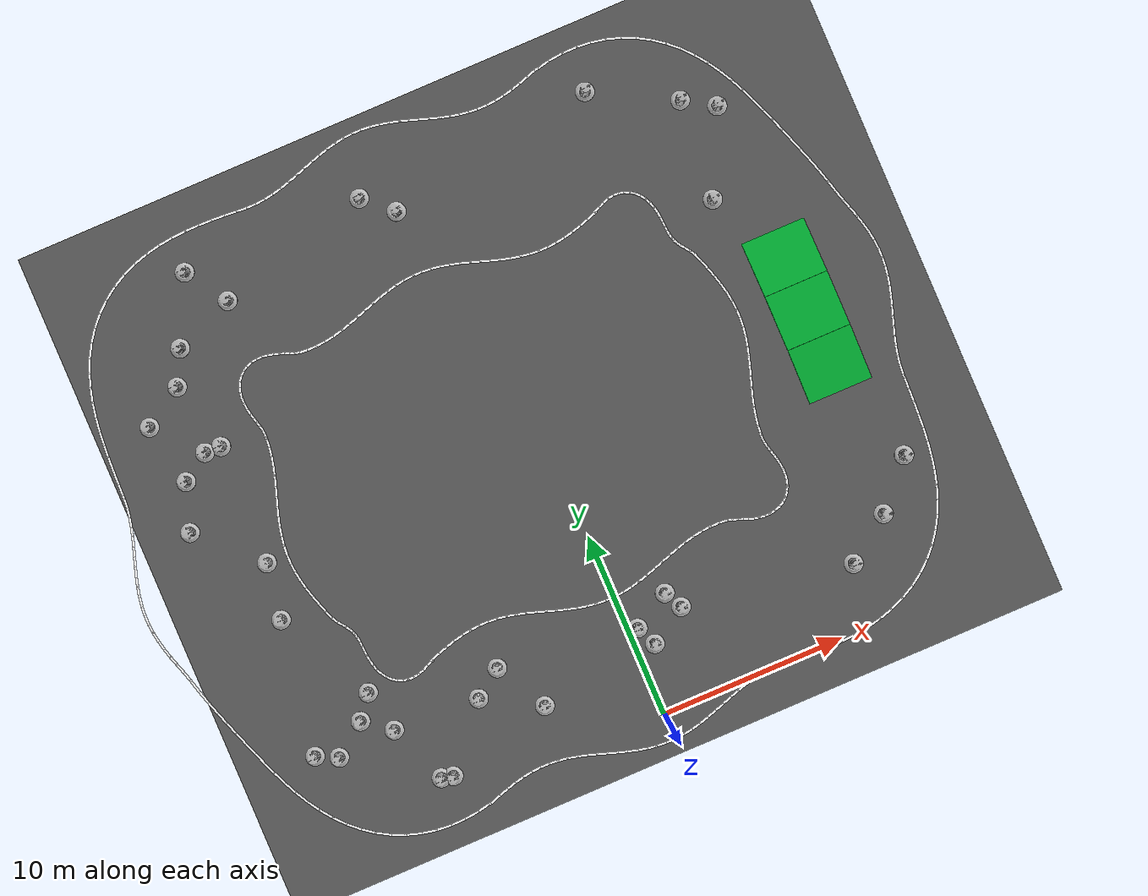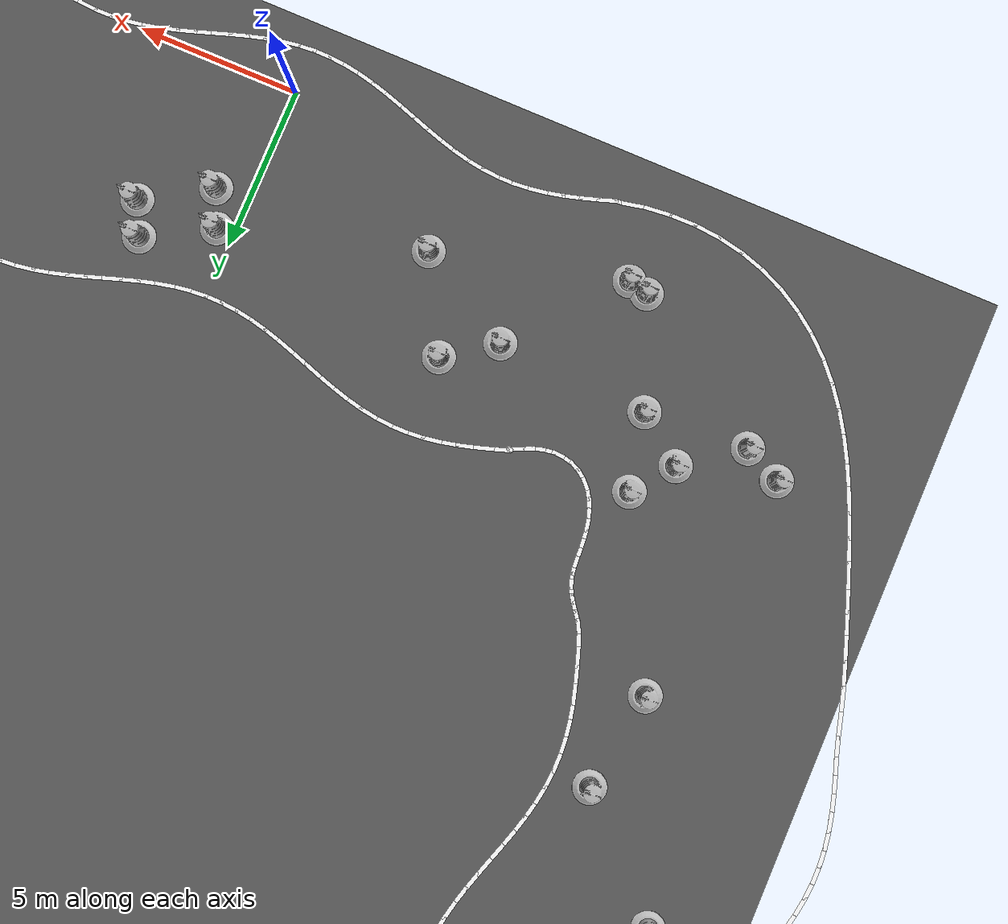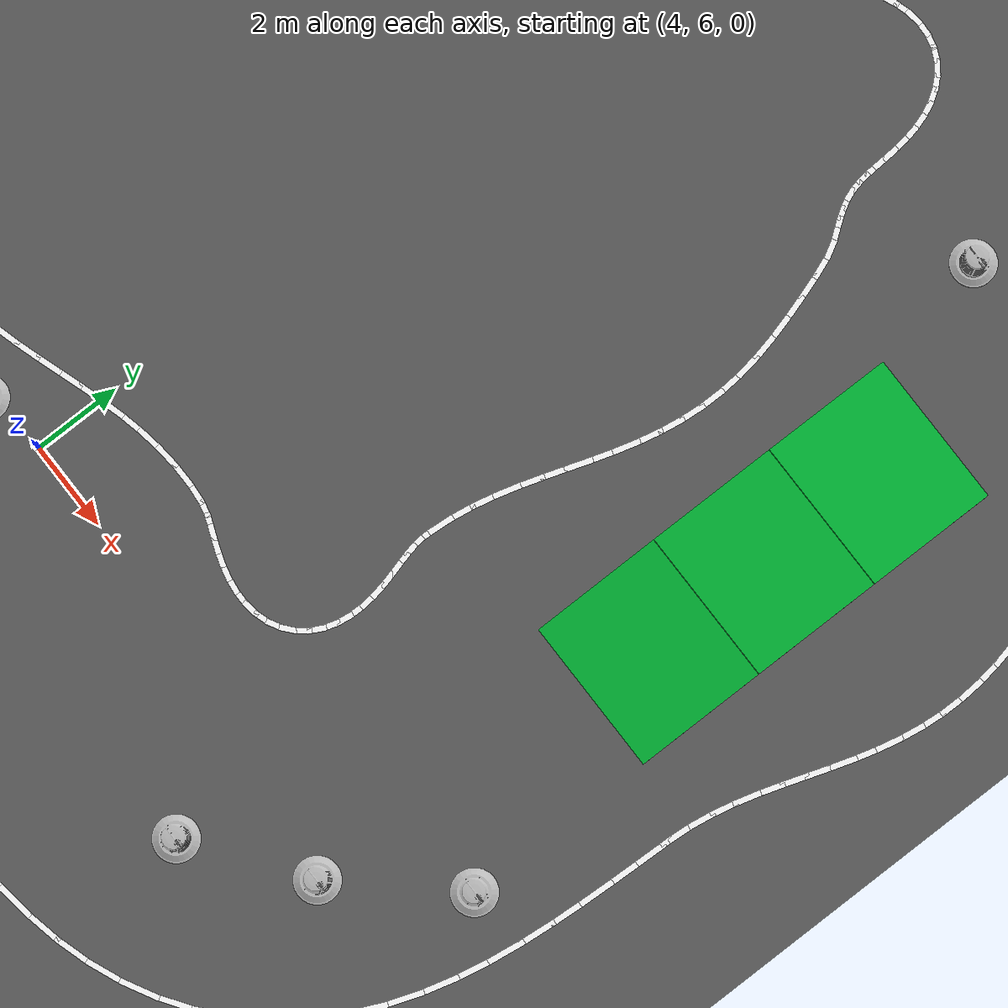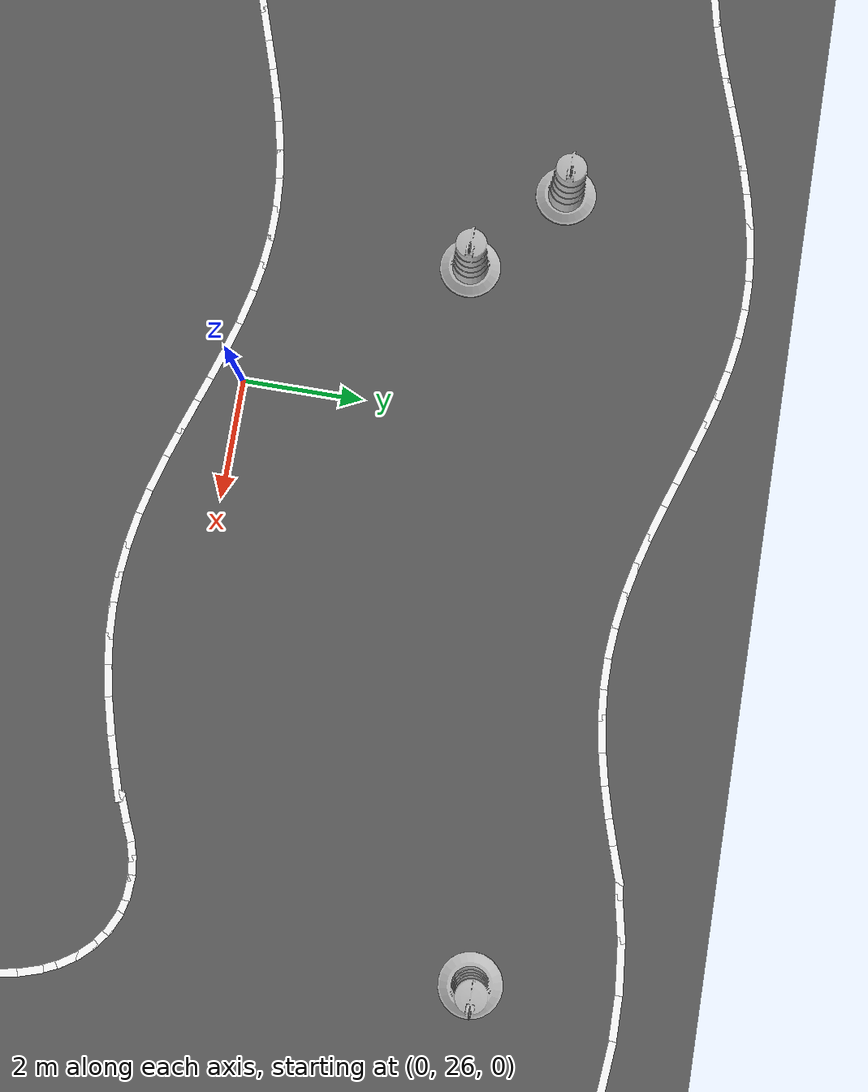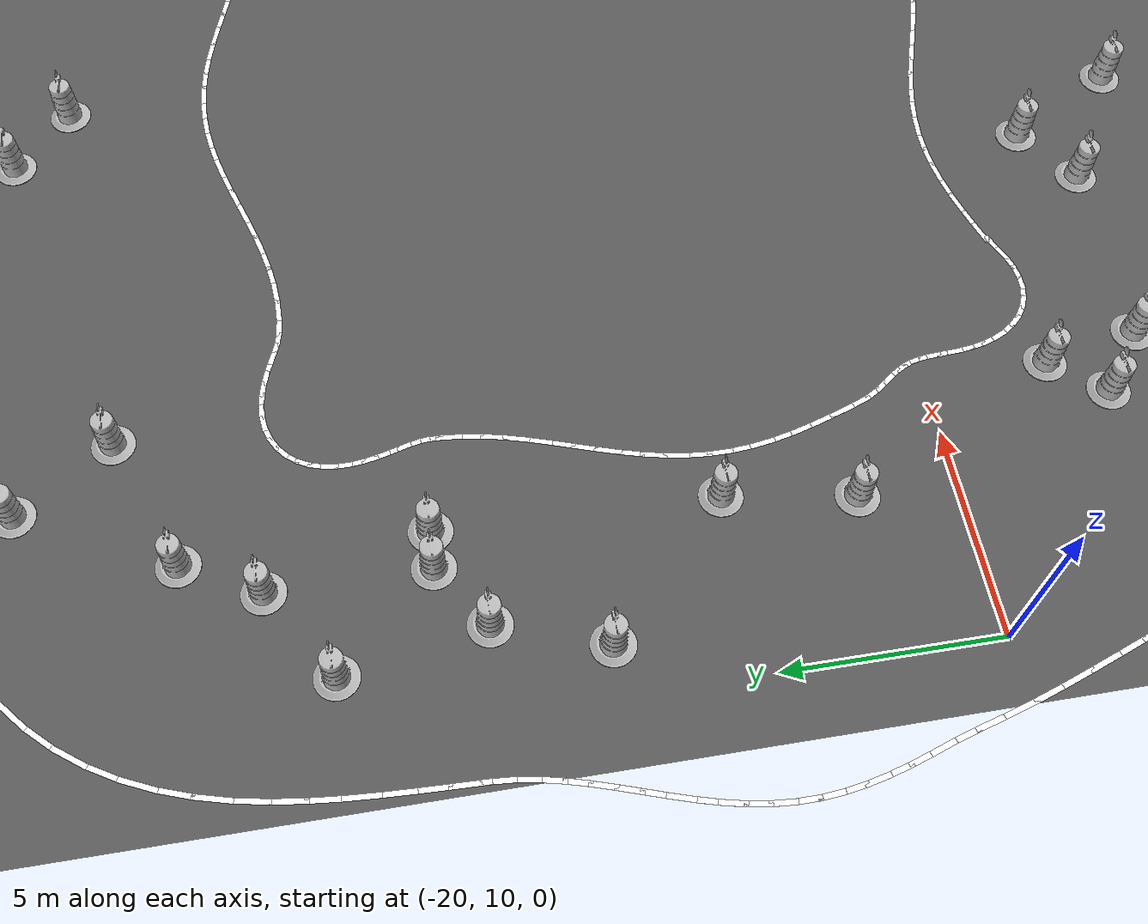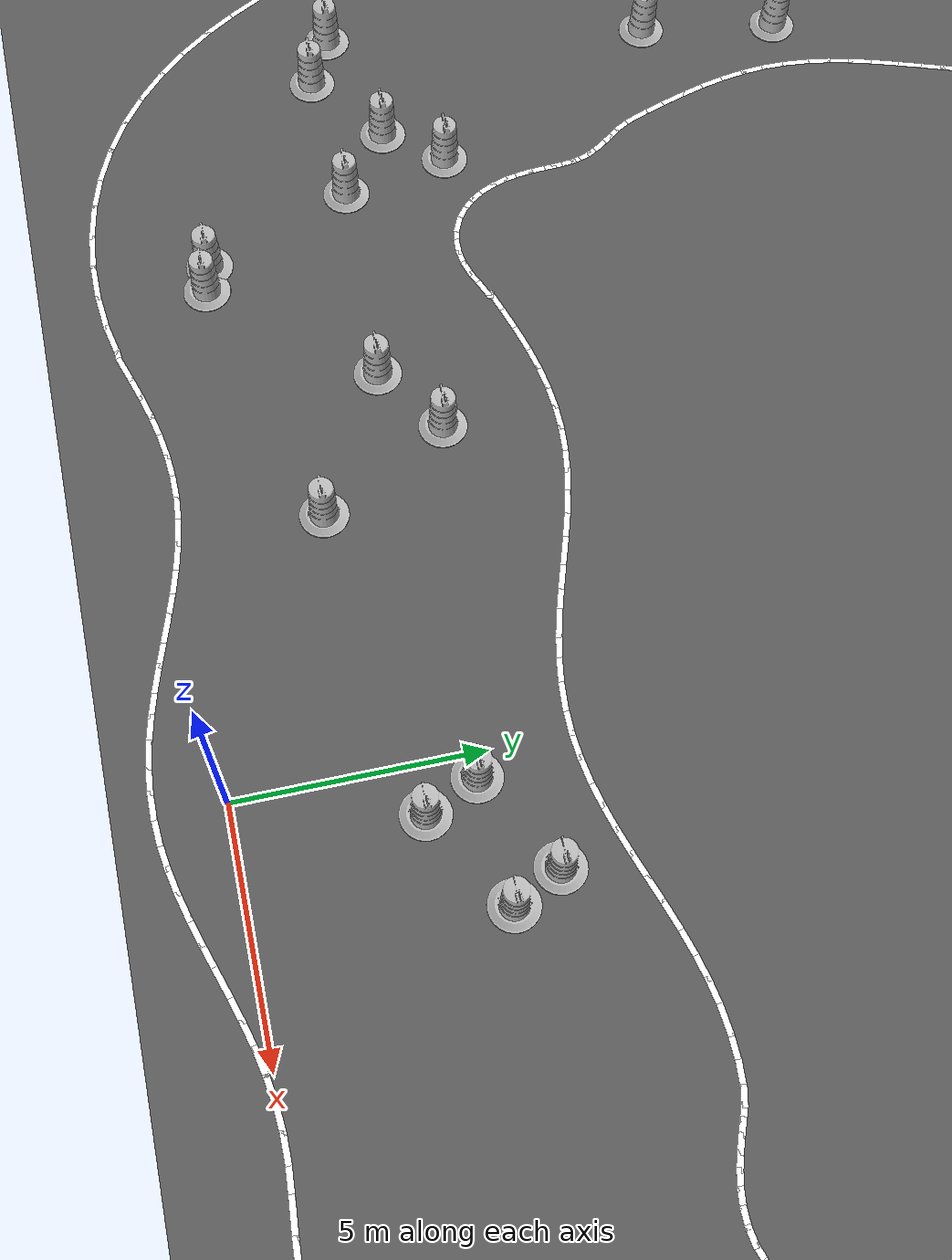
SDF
<?xml version="1.0"?>
<sdf version="1.8">
  <world name="default">
    <!-- Gazebo Fortress world systems -->
    <plugin filename="libignition-gazebo-physics-system.so"
            name="ignition::gazebo::systems::Physics"/>
    <plugin filename="libignition-gazebo-user-commands-system.so"
            name="ignition::gazebo::systems::UserCommands"/>
    <plugin filename="libignition-gazebo-scene-broadcaster-system.so"
            name="ignition::gazebo::systems::SceneBroadcaster"/>
    <plugin filename="libignition-gazebo-sensors-system.so"
            name="ignition::gazebo::systems::Sensors">
      <render_engine>ogre2</render_engine>
    </plugin>

    <scene>
      <grid>false</grid>
      <shadows>false</shadows>
    </scene>

    <light type="directional" name="sun">
      <cast_shadows>true</cast_shadows>
      <pose>0 0 10 0 0 0</pose>
      <diffuse>0.8 0.8 0.8 1</diffuse>
      <specular>0.2 0.2 0.2 1</specular>
      <attenuation>
        <range>1000</range>
        <constant>0.9</constant>
        <linear>0.01</linear>
        <quadratic>0.001</quadratic>
      </attenuation>
      <direction>-0.5 0.1 -0.9</direction>
    </light>

    <include>
      <pose>0 16.3 0 0 0 0</pose>
      <uri>model://orange_igvc</uri>
      <name>orange_igvc</name>
    </include>
  </world>
</sdf>

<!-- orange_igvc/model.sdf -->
<sdf version="1.6">
  <model name="orange_igvc">
    <static>true</static>

    <link name="ground">
      <visual name="visual">
        <geometry>
          <plane>
            <size>43 37</size>
          </plane>
        </geometry>
        <material>
          <ambient>0.35 0.35 0.35 1.0</ambient>
          <diffuse>0.35 0.35 0.35 1.0</diffuse>
        </material>
      </visual>
      <collision name="collision">
        <geometry>
          <plane>
            <size>43 37</size>
          </plane>
        </geometry>
        <surface>
          <friction>
            <ode>
              <mu>100</mu>
              <mu2>50</mu2>
            </ode>
          </friction>
          <bounce />
          <contact>
            <ode />
          </contact>
        </surface>
      </collision>
    </link>

    <link name="construction_barrel1">
      <pose>-14.58 -10.44 0.05 0 0 0</pose>
      <visual name="visual">
        <geometry>
          <mesh>
            <uri>model://construction_barrel/meshes/construction_barrel.dae</uri>
          </mesh>
        </geometry>
      </visual>
      <collision name="collision">
        <geometry>
          <mesh>
            <uri>model://construction_barrel/meshes/construction_barrel.dae</uri>
          </mesh>
        </geometry>
      </collision>
    </link>
    <link name="construction_barrel2">
      <pose>-12.34 12.27 0.05 0 0 0</pose>
      <visual name="visual">
        <geometry>
          <mesh>
            <uri>model://construction_barrel/meshes/construction_barrel.dae</uri>
          </mesh>
        </geometry>
      </visual>
      <collision name="collision">
        <geometry>
          <mesh>
            <uri>model://construction_barrel/meshes/construction_barrel.dae</uri>
          </mesh>
        </geometry>
      </collision>
    </link>
    <link name="construction_barrel3">
      <pose>-2.50 13.08 0.05 0 0 0</pose>
      <visual name="visual">
        <geometry>
          <mesh>
            <uri>model://construction_barrel/meshes/construction_barrel.dae</uri>
          </mesh>
        </geometry>
      </visual>
      <collision name="collision">
        <geometry>
          <mesh>
            <uri>model://construction_barrel/meshes/construction_barrel.dae</uri>
          </mesh>
        </geometry>
      </collision>
    </link>
    <link name="construction_barrel4">
      <pose>-13.15 -11.54 0.05 0 0 0</pose>
      <visual name="visual">
        <geometry>
          <mesh>
            <uri>model://construction_barrel/meshes/construction_barrel.dae</uri>
          </mesh>
        </geometry>
      </visual>
      <collision name="collision">
        <geometry>
          <mesh>
            <uri>model://construction_barrel/meshes/construction_barrel.dae</uri>
          </mesh>
        </geometry>
      </collision>
    </link>
    <link name="construction_barrel5">
      <pose>-16.51 5.51 0.05 0 0 0</pose>
      <visual name="visual">
        <geometry>
          <mesh>
            <uri>model://construction_barrel/meshes/construction_barrel.dae</uri>
          </mesh>
        </geometry>
      </visual>
      <collision name="collision">
        <geometry>
          <mesh>
            <uri>model://construction_barrel/meshes/construction_barrel.dae</uri>
          </mesh>
        </geometry>
      </collision>
    </link>
    <link name="construction_barrel6">
      <pose>-11.27 -14.93 0.05 0 0 0</pose>
      <visual name="visual">
        <geometry>
          <mesh>
            <uri>model://construction_barrel/meshes/construction_barrel.dae</uri>
          </mesh>
        </geometry>
      </visual>
      <collision name="collision">
        <geometry>
          <mesh>
            <uri>model://construction_barrel/meshes/construction_barrel.dae</uri>
          </mesh>
        </geometry>
      </collision>
    </link>
    <link name="construction_barrel7">
      <pose>14.52 -11.21 0.05 0 0 0</pose>
      <visual name="visual">
        <geometry>
          <mesh>
            <uri>model://construction_barrel/meshes/construction_barrel.dae</uri>
          </mesh>
        </geometry>
      </visual>
      <collision name="collision">
        <geometry>
          <mesh>
            <uri>model://construction_barrel/meshes/construction_barrel.dae</uri>
          </mesh>
        </geometry>
      </collision>
    </link>
    <link name="construction_barrel8">
      <pose>-13.81 14.50 0.05 0 0 0</pose>
      <visual name="visual">
        <geometry>
          <mesh>
            <uri>model://construction_barrel/meshes/construction_barrel.dae</uri>
          </mesh>
        </geometry>
      </visual>
      <collision name="collision">
        <geometry>
          <mesh>
            <uri>model://construction_barrel/meshes/construction_barrel.dae</uri>
          </mesh>
        </geometry>
      </collision>
    </link>
    <link name="construction_barrel9">
      <pose>-16.32 -11.73 0.05 0 0 0</pose>
      <visual name="visual">
        <geometry>
          <mesh>
            <uri>model://construction_barrel/meshes/construction_barrel.dae</uri>
          </mesh>
        </geometry>
      </visual>
      <collision name="collision">
        <geometry>
          <mesh>
            <uri>model://construction_barrel/meshes/construction_barrel.dae</uri>
          </mesh>
        </geometry>
      </collision>
    </link>
    <link name="construction_barrel10">
      <pose>-13.63 -9.23 0.05 0 0 0</pose>
      <visual name="visual">
        <geometry>
          <mesh>
            <uri>model://construction_barrel/meshes/construction_barrel.dae</uri>
          </mesh>
        </geometry>
      </visual>
      <collision name="collision">
        <geometry>
          <mesh>
            <uri>model://construction_barrel/meshes/construction_barrel.dae</uri>
          </mesh>
        </geometry>
      </collision>
    </link>
    <link name="construction_barrel11">
      <pose>8.90 14.94 0.05 0 0 0</pose>
      <visual name="visual">
        <geometry>
          <mesh>
            <uri>model://construction_barrel/meshes/construction_barrel.dae</uri>
          </mesh>
        </geometry>
      </visual>
      <collision name="collision">
        <geometry>
          <mesh>
            <uri>model://construction_barrel/meshes/construction_barrel.dae</uri>
          </mesh>
        </geometry>
      </collision>
    </link>
    <link name="construction_barrel12">
      <pose>-7.00 -10.69 0.05 0 0 0</pose>
      <visual name="visual">
        <geometry>
          <mesh>
            <uri>model://construction_barrel/meshes/construction_barrel.dae</uri>
          </mesh>
        </geometry>
      </visual>
      <collision name="collision">
        <geometry>
          <mesh>
            <uri>model://construction_barrel/meshes/construction_barrel.dae</uri>
          </mesh>
        </geometry>
      </collision>
    </link>
    <link name="construction_barrel13">
      <pose>-15.63 5.47 0.05 0 0 0</pose>
      <visual name="visual">
        <geometry>
          <mesh>
            <uri>model://construction_barrel/meshes/construction_barrel.dae</uri>
          </mesh>
        </geometry>
      </visual>
      <collision name="collision">
        <geometry>
          <mesh>
            <uri>model://construction_barrel/meshes/construction_barrel.dae</uri>
          </mesh>
        </geometry>
      </collision>
    </link>
    <link name="construction_barrel14">
      <pose>-4.00 14.46 0.05 0 0 0</pose>
      <visual name="visual">
        <geometry>
          <mesh>
            <uri>model://construction_barrel/meshes/construction_barrel.dae</uri>
          </mesh>
        </geometry>
      </visual>
      <collision name="collision">
        <geometry>
          <mesh>
            <uri>model://construction_barrel/meshes/construction_barrel.dae</uri>
          </mesh>
        </geometry>
      </collision>
    </link>
    <link name="construction_barrel15">
      <pose>-18.85 2.00 0.05 0 0 0</pose>
      <visual name="visual">
        <geometry>
          <mesh>
            <uri>model://construction_barrel/meshes/construction_barrel.dae</uri>
          </mesh>
        </geometry>
      </visual>
      <collision name="collision">
        <geometry>
          <mesh>
            <uri>model://construction_barrel/meshes/construction_barrel.dae</uri>
          </mesh>
        </geometry>
      </collision>
    </link>
    <link name="construction_barrel16">
      <pose>1.00 -12.74 0.05 0 0 0</pose>
      <visual name="visual">
        <geometry>
          <mesh>
            <uri>model://construction_barrel/meshes/construction_barrel.dae</uri>
          </mesh>
        </geometry>
      </visual>
      <collision name="collision">
        <geometry>
          <mesh>
            <uri>model://construction_barrel/meshes/construction_barrel.dae</uri>
          </mesh>
        </geometry>
      </collision>
    </link>
    <link name="construction_barrel17">
      <pose>-15.57 10.97 0.05 0 0 0</pose>
      <visual name="visual">
        <geometry>
          <mesh>
            <uri>model://construction_barrel/meshes/construction_barrel.dae</uri>
          </mesh>
        </geometry>
      </visual>
      <collision name="collision">
        <geometry>
          <mesh>
            <uri>model://construction_barrel/meshes/construction_barrel.dae</uri>
          </mesh>
        </geometry>
      </collision>
    </link>
    <link name="construction_barrel18">
      <pose>-15.81 -1.00 0.05 0 0 0</pose>
      <visual name="visual">
        <geometry>
          <mesh>
            <uri>model://construction_barrel/meshes/construction_barrel.dae</uri>
          </mesh>
        </geometry>
      </visual>
      <collision name="collision">
        <geometry>
          <mesh>
            <uri>model://construction_barrel/meshes/construction_barrel.dae</uri>
          </mesh>
        </geometry>
      </collision>
    </link>
    <link name="construction_barrel19">
      <pose>13.27 12.60 0.05 0 0 0</pose>
      <visual name="visual">
        <geometry>
          <mesh>
            <uri>model://construction_barrel/meshes/construction_barrel.dae</uri>
          </mesh>
        </geometry>
      </visual>
      <collision name="collision">
        <geometry>
          <mesh>
            <uri>model://construction_barrel/meshes/construction_barrel.dae</uri>
          </mesh>
        </geometry>
      </collision>
    </link>
    <link name="construction_barrel20">
      <pose>-18.00 4.50 0.05 0 0 0</pose>
      <visual name="visual">
        <geometry>
          <mesh>
            <uri>model://construction_barrel/meshes/construction_barrel.dae</uri>
          </mesh>
        </geometry>
      </visual>
      <collision name="collision">
        <geometry>
          <mesh>
            <uri>model://construction_barrel/meshes/construction_barrel.dae</uri>
          </mesh>
        </geometry>
      </collision>
    </link>
    <link name="construction_barrel21">
      <pose>-8.50 -11.76 0.05 0 0 0</pose>
      <visual name="visual">
        <geometry>
          <mesh>
            <uri>model://construction_barrel/meshes/construction_barrel.dae</uri>
          </mesh>
        </geometry>
      </visual>
      <collision name="collision">
        <geometry>
          <mesh>
            <uri>model://construction_barrel/meshes/construction_barrel.dae</uri>
          </mesh>
        </geometry>
      </collision>
    </link>
    <link name="construction_barrel22">
      <pose>-16.29 -4.00 0.05 0 0 0</pose>
      <visual name="visual">
        <geometry>
          <mesh>
            <uri>model://construction_barrel/meshes/construction_barrel.dae</uri>
          </mesh>
        </geometry>
      </visual>
      <collision name="collision">
        <geometry>
          <mesh>
            <uri>model://construction_barrel/meshes/construction_barrel.dae</uri>
          </mesh>
        </geometry>
      </collision>
    </link>
    <link name="construction_barrel23">
      <pose>14.91 11.58 0.05 0 0 0</pose>
      <visual name="visual">
        <geometry>
          <mesh>
            <uri>model://construction_barrel/meshes/construction_barrel.dae</uri>
          </mesh>
        </geometry>
      </visual>
      <collision name="collision">
        <geometry>
          <mesh>
            <uri>model://construction_barrel/meshes/construction_barrel.dae</uri>
          </mesh>
        </geometry>
      </collision>
    </link>
    <link name="construction_barrel24">
      <pose>-17.45 -11.18 0.05 0 0 0</pose>
      <visual name="visual">
        <geometry>
          <mesh>
            <uri>model://construction_barrel/meshes/construction_barrel.dae</uri>
          </mesh>
        </geometry>
      </visual>
      <collision name="collision">
        <geometry>
          <mesh>
            <uri>model://construction_barrel/meshes/construction_barrel.dae</uri>
          </mesh>
        </geometry>
      </collision>
    </link>
    <link name="construction_barrel25">
      <pose>-11.88 -14.78 0.05 0 0 0</pose>
      <visual name="visual">
        <geometry>
          <mesh>
            <uri>model://construction_barrel/meshes/construction_barrel.dae</uri>
          </mesh>
        </geometry>
      </visual>
      <collision name="collision">
        <geometry>
          <mesh>
            <uri>model://construction_barrel/meshes/construction_barrel.dae</uri>
          </mesh>
        </geometry>
      </collision>
    </link>
    <link name="construction_barrel26">
      <pose>-16.50 9.19 0.05 0 0 0</pose>
      <visual name="visual">
        <geometry>
          <mesh>
            <uri>model://construction_barrel/meshes/construction_barrel.dae</uri>
          </mesh>
        </geometry>
      </visual>
      <collision name="collision">
        <geometry>
          <mesh>
            <uri>model://construction_barrel/meshes/construction_barrel.dae</uri>
          </mesh>
        </geometry>
      </collision>
    </link>
    <link name="construction_barrel27">
      <pose>12.08 -12.97 0.05 0 0 0</pose>
      <visual name="visual">
        <geometry>
          <mesh>
            <uri>model://construction_barrel/meshes/construction_barrel.dae</uri>
          </mesh>
        </geometry>
      </visual>
      <collision name="collision">
        <geometry>
          <mesh>
            <uri>model://construction_barrel/meshes/construction_barrel.dae</uri>
          </mesh>
        </geometry>
      </collision>
    </link>
    <link name="construction_barrel28">
      <pose>3.00 -11.52 0.05 0 0 0</pose>
      <visual name="visual">
        <geometry>
          <mesh>
            <uri>model://construction_barrel/meshes/construction_barrel.dae</uri>
          </mesh>
        </geometry>
      </visual>
      <collision name="collision">
        <geometry>
          <mesh>
            <uri>model://construction_barrel/meshes/construction_barrel.dae</uri>
          </mesh>
        </geometry>
      </collision>
    </link>
    <link name="construction_barrel29">
      <pose>16.69 -8.83 0.05 0 0 0</pose>
      <visual name="visual">
        <geometry>
          <mesh>
            <uri>model://construction_barrel/meshes/construction_barrel.dae</uri>
          </mesh>
        </geometry>
      </visual>
      <collision name="collision">
        <geometry>
          <mesh>
            <uri>model://construction_barrel/meshes/construction_barrel.dae</uri>
          </mesh>
        </geometry>
      </collision>
    </link>
    <link name="construction_barrel30">
      <pose>-18.64 7.83 0.05 0 0 0</pose>
      <visual name="visual">
        <geometry>
          <mesh>
            <uri>model://construction_barrel/meshes/construction_barrel.dae</uri>
          </mesh>
        </geometry>
      </visual>
      <collision name="collision">
        <geometry>
          <mesh>
            <uri>model://construction_barrel/meshes/construction_barrel.dae</uri>
          </mesh>
        </geometry>
      </collision>
    </link>
    <link name="construction_barrel31">
      <pose>12.79 7.22 0.05 0 0 0</pose>
      <visual name="visual">
        <geometry>
          <mesh>
            <uri>model://construction_barrel/meshes/construction_barrel.dae</uri>
          </mesh>
        </geometry>
      </visual>
      <collision name="collision">
        <geometry>
          <mesh>
            <uri>model://construction_barrel/meshes/construction_barrel.dae</uri>
          </mesh>
        </geometry>
      </collision>
    </link>
    <link name="construction_barrel32">
      <pose>2.50 -10.53 0.05 0 0 0</pose>
      <visual name="visual">
        <geometry>
          <mesh>
            <uri>model://construction_barrel/meshes/construction_barrel.dae</uri>
          </mesh>
        </geometry>
      </visual>
      <collision name="collision">
        <geometry>
          <mesh>
            <uri>model://construction_barrel/meshes/construction_barrel.dae</uri>
          </mesh>
        </geometry>
      </collision>
    </link>
    <link name="construction_barrel33">
      <pose>-5.50 -13.45 0.05 0 0 0</pose>
      <visual name="visual">
        <geometry>
          <mesh>
            <uri>model://construction_barrel/meshes/construction_barrel.dae</uri>
          </mesh>
        </geometry>
      </visual>
      <collision name="collision">
        <geometry>
          <mesh>
            <uri>model://construction_barrel/meshes/construction_barrel.dae</uri>
          </mesh>
        </geometry>
      </collision>
    </link>
    <link name="construction_barrel34">
      <pose>0.50 -11.65 0.05 0 0 0</pose>
      <visual name="visual">
        <geometry>
          <mesh>
            <uri>model://construction_barrel/meshes/construction_barrel.dae</uri>
          </mesh>
        </geometry>
      </visual>
      <collision name="collision">
        <geometry>
          <mesh>
            <uri>model://construction_barrel/meshes/construction_barrel.dae</uri>
          </mesh>
        </geometry>
      </collision>
    </link>
  <link name="white_line_inner_0">
          <pose>-9.749027792386808 -8.91644247873715 0.005 0 0 0.3237323808328417</pose>
          <visual name="visual">
            <geometry><box><size>0.6253447619169866 0.127 0.001</size></box></geometry>
            <material>
              <ambient>1.0 1.0 1.0 1.0</ambient>
              <diffuse>1.0 1.0 1.0 1.0</diffuse>
            </material>
          </visual>
        </link><link name="white_line_inner_1">
          <pose>-9.25 -8.754158973102335 0.005 0 0 0.30507171125245097</pose>
          <visual name="visual">
            <geometry><box><size>0.6242049454353742 0.127 0.001</size></box></geometry>
            <material>
              <ambient>1.0 1.0 1.0 1.0</ambient>
              <diffuse>1.0 1.0 1.0 1.0</diffuse>
            </material>
          </visual>
        </link><link name="white_line_inner_2">
          <pose>-8.75 -8.606092986514474 0.005 0 0 0.27056072113404495</pose>
          <visual name="visual">
            <geometry><box><size>0.61887609868577 0.127 0.001</size></box></geometry>
            <material>
              <ambient>1.0 1.0 1.0 1.0</ambient>
              <diffuse>1.0 1.0 1.0 1.0</diffuse>
            </material>
          </visual>
        </link><link name="white_line_inner_3">
          <pose>-8.25 -8.480807117056022 0.005 0 0 0.22015442914586508</pose>
          <visual name="visual">
            <geometry><box><size>0.6123666155494492 0.127 0.001</size></box></geometry>
            <material>
              <ambient>1.0 1.0 1.0 1.0</ambient>
              <diffuse>1.0 1.0 1.0 1.0</diffuse>
            </material>
          </visual>
        </link><link name="white_line_inner_4">
          <pose>-7.75 -8.385546797489573 0.005 0 0 0.1559822261198246</pose>
          <visual name="visual">
            <geometry><box><size>0.6061448935681873 0.127 0.001</size></box></geometry>
            <material>
              <ambient>1.0 1.0 1.0 1.0</ambient>
              <diffuse>1.0 1.0 1.0 1.0</diffuse>
            </material>
          </visual>
        </link><link name="white_line_inner_5">
          <pose>-7.25 -8.325821046855701 0.005 0 0 0.08146262360069775</pose>
          <visual name="visual">
            <geometry><box><size>0.6016636395291733 0.127 0.001</size></box></geometry>
            <material>
              <ambient>1.0 1.0 1.0 1.0</ambient>
              <diffuse>1.0 1.0 1.0 1.0</diffuse>
            </material>
          </visual>
        </link><link name="white_line_inner_6">
          <pose>-6.75 -8.30508387726514 0.005 0 0 0.0013053747562815667</pose>
          <visual name="visual">
            <geometry><box><size>0.600000426001116 0.127 0.001</size></box></geometry>
            <material>
              <ambient>1.0 1.0 1.0 1.0</ambient>
              <diffuse>1.0 1.0 1.0 1.0</diffuse>
            </material>
          </visual>
        </link><link name="white_line_inner_7">
          <pose>-6.25 -8.32453454421737 0.005 0 0 -0.07894363862715567</pose>
          <visual name="visual">
            <geometry><box><size>0.6015620805333591 0.127 0.001</size></box></geometry>
            <material>
              <ambient>1.0 1.0 1.0 1.0</ambient>
              <diffuse>1.0 1.0 1.0 1.0</diffuse>
            </material>
          </visual>
        </link><link name="white_line_inner_8">
          <pose>-5.75 -8.383048192210333 0.005 0 0 -0.15372410240245407</pose>
          <visual name="visual">
            <geometry><box><size>0.6059665090060945 0.127 0.001</size></box></geometry>
            <material>
              <ambient>1.0 1.0 1.0 1.0</ambient>
              <diffuse>1.0 1.0 1.0 1.0</diffuse>
            </material>
          </visual>
        </link><link name="white_line_inner_9">
          <pose>-5.25 -8.477240906489243 0.005 0 0 -0.21828972551964032</pose>
          <visual name="visual">
            <geometry><box><size>0.6121537913116318 0.127 0.001</size></box></geometry>
            <material>
              <ambient>1.0 1.0 1.0 1.0</ambient>
              <diffuse>1.0 1.0 1.0 1.0</diffuse>
            </material>
          </visual>
        </link><link name="white_line_inner_10">
          <pose>-4.75 -8.601665408913444 0.005 0 0 -0.26917830241997737</pose>
          <visual name="visual">
            <geometry><box><size>0.618677717624193 0.127 0.001</size></box></geometry>
            <material>
              <ambient>1.0 1.0 1.0 1.0</ambient>
              <diffuse>1.0 1.0 1.0 1.0</diffuse>
            </material>
          </visual>
        </link><link name="white_line_inner_11">
          <pose>-4.25 -8.74912608061362 0.005 0 0 -0.3042226010041338</pose>
          <visual name="visual">
            <geometry><box><size>0.624065006437661 0.127 0.001</size></box></geometry>
            <material>
              <ambient>1.0 1.0 1.0 1.0</ambient>
              <diffuse>1.0 1.0 1.0 1.0</diffuse>
            </material>
          </visual>
        </link><link name="white_line_inner_12">
          <pose>-3.7499999999999996 -8.911095093299569 0.005 0 0 -0.32226682416115493</pose>
          <visual name="visual">
            <geometry><box><size>0.6271370619164044 0.127 0.001</size></box></geometry>
            <material>
              <ambient>1.0 1.0 1.0 1.0</ambient>
              <diffuse>1.0 1.0 1.0 1.0</diffuse>
            </material>
          </visual>
        </link><link name="white_line_inner_13">
          <pose>-3.2499999999999996 -9.07820558384369 0.005 0 0 -0.3228315715904382</pose>
          <visual name="visual">
            <geometry><box><size>0.6272365686535137 0.127 0.001</size></box></geometry>
            <material>
              <ambient>1.0 1.0 1.0 1.0</ambient>
              <diffuse>1.0 1.0 1.0 1.0</diffuse>
            </material>
          </visual>
        </link><link name="white_line_inner_14">
          <pose>-2.7499999999999996 -9.240793351259914 0.005 0 0 -0.30590314914492844</pose>
          <visual name="visual">
            <geometry><box><size>0.6243424107691674 0.127 0.001</size></box></geometry>
            <material>
              <ambient>1.0 1.0 1.0 1.0</ambient>
              <diffuse>1.0 1.0 1.0 1.0</diffuse>
            </material>
          </visual>
        </link><link name="white_line_inner_15">
          <pose>-2.2499999999999996 -9.389455749089171 0.005 0 0 -0.2719266051963547</pose>
          <visual name="visual">
            <geometry><box><size>0.6190732307078665 0.127 0.001</size></box></geometry>
            <material>
              <ambient>1.0 1.0 1.0 1.0</ambient>
              <diffuse>1.0 1.0 1.0 1.0</diffuse>
            </material>
          </visual>
        </link><link name="white_line_inner_16">
          <pose>-1.7499999999999998 -9.515595451771496 0.005 0 0 -0.22200477363032112</pose>
          <visual name="visual">
            <geometry><box><size>0.6125797383418122 0.127 0.001</size></box></geometry>
            <material>
              <ambient>1.0 1.0 1.0 1.0</ambient>
              <diffuse>1.0 1.0 1.0 1.0</diffuse>
            </material>
          </visual>
        </link><link name="white_line_inner_17">
          <pose>-1.2499999999999998 -9.611917648340349 0.005 0 0 -0.15822952551615452</pose>
          <visual name="visual">
            <geometry><box><size>0.6063251121473052 0.127 0.001</size></box></geometry>
            <material>
              <ambient>1.0 1.0 1.0 1.0</ambient>
              <diffuse>1.0 1.0 1.0 1.0</diffuse>
            </material>
          </visual>
        </link><link name="white_line_inner_18">
          <pose>-0.7499999999999998 -9.672851910128855 0.005 0 0 -0.08397569799048121</pose>
          <visual name="visual">
            <geometry><box><size>0.6017681745223847 0.127 0.001</size></box></geometry>
            <material>
              <ambient>1.0 1.0 1.0 1.0</ambient>
              <diffuse>1.0 1.0 1.0 1.0</diffuse>
            </material>
          </visual>
        </link><link name="white_line_inner_19">
          <pose>-0.24999999999999978 -9.694874335370326 0.005 0 0 -0.003916027979200692</pose>
          <visual name="visual">
            <geometry><box><size>0.6000038338432806 0.127 0.001</size></box></geometry>
            <material>
              <ambient>1.0 1.0 1.0 1.0</ambient>
              <diffuse>1.0 1.0 1.0 1.0</diffuse>
            </material>
          </visual>
        </link><link name="white_line_inner_20">
          <pose>0.2500000000000002 -9.676711340682637 0.005 0 0 0.07641892005618513</pose>
          <visual name="visual">
            <geometry><box><size>0.6014635237781663 0.127 0.001</size></box></geometry>
            <material>
              <ambient>1.0 1.0 1.0 1.0</ambient>
              <diffuse>1.0 1.0 1.0 1.0</diffuse>
            </material>
          </visual>
        </link><link name="white_line_inner_21">
          <pose>0.7500000000000002 -9.619413313929527 0.005 0 0 0.15145529211583023</pose>
          <visual name="visual">
            <geometry><box><size>0.6057900033305827 0.127 0.001</size></box></geometry>
            <material>
              <ambient>1.0 1.0 1.0 1.0</ambient>
              <diffuse>1.0 1.0 1.0 1.0</diffuse>
            </material>
          </visual>
        </link><link name="white_line_inner_22">
          <pose>1.2500000000000002 -9.526293869025032 0.005 0 0 0.21641075410120117</pose>
          <visual name="visual">
            <geometry><box><size>0.61194131722283 0.127 0.001</size></box></geometry>
            <material>
              <ambient>1.0 1.0 1.0 1.0</ambient>
              <diffuse>1.0 1.0 1.0 1.0</diffuse>
            </material>
          </visual>
        </link><link name="white_line_inner_23">
          <pose>1.7500000000000004 -9.402738215648913 0.005 0 0 0.2677794008033291</pose>
          <visual name="visual">
            <geometry><box><size>0.6184781338331515 0.127 0.001</size></box></geometry>
            <material>
              <ambient>1.0 1.0 1.0 1.0</ambient>
              <diffuse>1.0 1.0 1.0 1.0</diffuse>
            </material>
          </visual>
        </link><link name="white_line_inner_24">
          <pose>2.2500000000000004 -9.255891726083332 0.005 0 0 0.3033558427576608</pose>
          <visual name="visual">
            <geometry><box><size>0.6239226254668137 0.127 0.001</size></box></geometry>
            <material>
              <ambient>1.0 1.0 1.0 1.0</ambient>
              <diffuse>1.0 1.0 1.0 1.0</diffuse>
            </material>
          </visual>
        </link><link name="white_line_inner_25">
          <pose>2.7500000000000004 -9.094246709725745 0.005 0 0 0.3219572593375773</pose>
          <visual name="visual">
            <geometry><box><size>0.6270826048143481 0.127 0.001</size></box></geometry>
            <material>
              <ambient>1.0 1.0 1.0 1.0</ambient>
              <diffuse>1.0 1.0 1.0 1.0</diffuse>
            </material>
          </visual>
        </link><link name="white_line_inner_26">
          <pose>3.2500000000000004 -8.927151292605764 0.005 0 0 0.32308674064906595</pose>
          <visual name="visual">
            <geometry><box><size>0.6272815961340339 0.127 0.001</size></box></geometry>
            <material>
              <ambient>1.0 1.0 1.0 1.0</ambient>
              <diffuse>1.0 1.0 1.0 1.0</diffuse>
            </material>
          </visual>
        </link><link name="white_line_inner_27">
          <pose>3.75 -8.764268803995186 0.005 0 0 0.30671689101200544</pose>
          <visual name="visual">
            <geometry><box><size>0.6244773713326279 0.127 0.001</size></box></geometry>
            <material>
              <ambient>1.0 1.0 1.0 1.0</ambient>
              <diffuse>1.0 1.0 1.0 1.0</diffuse>
            </material>
          </visual>
        </link><link name="white_line_inner_28">
          <pose>4.25 -8.615018934434795 0.005 0 0 0.2732759039336813</pose>
          <visual name="visual">
            <geometry><box><size>0.619269067724084 0.127 0.001</size></box></geometry>
            <material>
              <ambient>1.0 1.0 1.0 1.0</ambient>
              <diffuse>1.0 1.0 1.0 1.0</diffuse>
            </material>
          </visual>
        </link><link name="white_line_inner_29">
          <pose>4.75 -8.488032983682496 0.005 0 0 0.22384066905656302</pose>
          <visual name="visual">
            <geometry><box><size>0.6127931080864082 0.127 0.001</size></box></geometry>
            <material>
              <ambient>1.0 1.0 1.0 1.0</ambient>
              <diffuse>1.0 1.0 1.0 1.0</diffuse>
            </material>
          </visual>
        </link><link name="white_line_inner_30">
          <pose>5.25 -8.390654702250194 0.005 0 0 0.16046586431314974</pose>
          <visual name="visual">
            <geometry><box><size>0.6065071194614166 0.127 0.001</size></box></geometry>
            <material>
              <ambient>1.0 1.0 1.0 1.0</ambient>
              <diffuse>1.0 1.0 1.0 1.0</diffuse>
            </material>
          </visual>
        </link><link name="white_line_inner_31">
          <pose>5.75 -8.328515593464672 0.005 0 0 0.08648268578142763</pose>
          <visual name="visual">
            <geometry><box><size>0.6018756585177814 0.127 0.001</size></box></geometry>
            <material>
              <ambient>1.0 1.0 1.0 1.0</ambient>
              <diffuse>1.0 1.0 1.0 1.0</diffuse>
            </material>
          </visual>
        </link><link name="white_line_inner_32">
          <pose>6.25 -8.305209236845947 0.005 0 0 0.006526392350070796</pose>
          <visual name="visual">
            <geometry><box><size>0.6000106486382625 0.127 0.001</size></box></geometry>
            <material>
              <ambient>1.0 1.0 1.0 1.0</ambient>
              <diffuse>1.0 1.0 1.0 1.0</diffuse>
            </material>
          </visual>
        </link><link name="white_line_inner_33">
          <pose>6.713602797569356 -8.322367802858976 0.005 0 0 -0.08774202836432715</pose>
          <visual name="visual">
            <geometry><box><size>0.528855342822992 0.127 0.001</size></box></geometry>
            <material>
              <ambient>1.0 1.0 1.0 1.0</ambient>
              <diffuse>1.0 1.0 1.0 1.0</diffuse>
            </material>
          </visual>
        </link><link name="white_line_inner_34">
          <pose>7.070274580948903 -8.375104621368079 0.005 0 0 -0.23296639095407004</pose>
          <visual name="visual">
            <geometry><box><size>0.3940823590322541 0.127 0.001</size></box></geometry>
            <material>
              <ambient>1.0 1.0 1.0 1.0</ambient>
              <diffuse>1.0 1.0 1.0 1.0</diffuse>
            </material>
          </visual>
        </link><link name="white_line_inner_35">
          <pose>7.326387945486001 -8.453090532564458 0.005 0 0 -0.3714872529362892</pose>
          <visual name="visual">
            <geometry><box><size>0.34263956594569395 0.127 0.001</size></box></geometry>
            <material>
              <ambient>1.0 1.0 1.0 1.0</ambient>
              <diffuse>1.0 1.0 1.0 1.0</diffuse>
            </material>
          </visual>
        </link><link name="white_line_inner_36">
          <pose>7.560929465551547 -8.546993209474403 0.005 0 0 -0.38944645332879746</pose>
          <visual name="visual">
            <geometry><box><size>0.3626626255065092 0.127 0.001</size></box></geometry>
            <material>
              <ambient>1.0 1.0 1.0 1.0</ambient>
              <diffuse>1.0 1.0 1.0 1.0</diffuse>
            </material>
          </visual>
        </link><link name="white_line_inner_37">
          <pose>7.813385168364517 -8.647603176896608 0.005 0 0 -0.3696851378994386</pose>
          <visual name="visual">
            <geometry><box><size>0.38089399593061235 0.127 0.001</size></box></geometry>
            <material>
              <ambient>1.0 1.0 1.0 1.0</ambient>
              <diffuse>1.0 1.0 1.0 1.0</diffuse>
            </material>
          </visual>
        </link><link name="white_line_inner_38">
          <pose>8.084524762918294 -8.744498208252494 0.005 0 0 -0.3180315190521233</pose>
          <visual name="visual">
            <geometry><box><size>0.3951637001919053 0.127 0.001</size></box></geometry>
            <material>
              <ambient>1.0 1.0 1.0 1.0</ambient>
              <diffuse>1.0 1.0 1.0 1.0</diffuse>
            </material>
          </visual>
        </link><link name="white_line_inner_39">
          <pose>8.372569318847004 -8.826637090662196 0.005 0 0 -0.23876012683329692</pose>
          <visual name="visual">
            <geometry><box><size>0.4043611790656285 0.127 0.001</size></box></geometry>
            <material>
              <ambient>1.0 1.0 1.0 1.0</ambient>
              <diffuse>1.0 1.0 1.0 1.0</diffuse>
            </material>
          </visual>
        </link><link name="white_line_inner_40">
          <pose>8.67321319559155 -8.883287597967652 0.005 0 0 -0.13441202375985797</pose>
          <visual name="visual">
            <geometry><box><size>0.40834186015554597 0.127 0.001</size></box></geometry>
            <material>
              <ambient>1.0 1.0 1.0 1.0</ambient>
              <diffuse>1.0 1.0 1.0 1.0</diffuse>
            </material>
          </visual>
        </link><link name="white_line_inner_41">
          <pose>8.979897585412594 -8.904922676091743 0.005 0 0 -0.006334981987636422</pose>
          <visual name="visual">
            <geometry><box><size>0.40781424843108094 0.127 0.001</size></box></geometry>
            <material>
              <ambient>1.0 1.0 1.0 1.0</ambient>
              <diffuse>1.0 1.0 1.0 1.0</diffuse>
            </material>
          </visual>
        </link><link name="white_line_inner_42">
          <pose>9.284312214195573 -8.884006342436358 0.005 0 0 0.14443426598271122</pose>
          <visual name="visual">
            <geometry><box><size>0.40418855150048394 0.127 0.001</size></box></geometry>
            <material>
              <ambient>1.0 1.0 1.0 1.0</ambient>
              <diffuse>1.0 1.0 1.0 1.0</diffuse>
            </material>
          </visual>
        </link><link name="white_line_inner_43">
          <pose>9.57708023074688 -8.81560102707131 0.005 0 0 0.31601316877776137</pose>
          <visual name="visual">
            <geometry><box><size>0.399337440380077 0.127 0.001</size></box></geometry>
            <material>
              <ambient>1.0 1.0 1.0 1.0</ambient>
              <diffuse>1.0 1.0 1.0 1.0</diffuse>
            </material>
          </visual>
        </link><link name="white_line_inner_44">
          <pose>9.848563893362147 -8.697744434037627 0.005 0 0 0.5044350700850666</pose>
          <visual name="visual">
            <geometry><box><size>0.3952232234972307 0.127 0.001</size></box></geometry>
            <material>
              <ambient>1.0 1.0 1.0 1.0</ambient>
              <diffuse>1.0 1.0 1.0 1.0</diffuse>
            </material>
          </visual>
        </link><link name="white_line_inner_45">
          <pose>10.089716945818619 -8.531564980002893 0.005 0 0 0.7029310446080024</pose>
          <visual name="visual">
            <geometry><box><size>0.39340511090800945 0.127 0.001</size></box></geometry>
            <material>
              <ambient>1.0 1.0 1.0 1.0</ambient>
              <diffuse>1.0 1.0 1.0 1.0</diffuse>
            </material>
          </visual>
        </link><link name="white_line_inner_46">
          <pose>10.292904655897736 -8.321128559229068 0.005 0 0 0.9025171515997361</pose>
          <visual name="visual">
            <geometry><box><size>0.39456280766559426 0.127 0.001</size></box></geometry>
            <material>
              <ambient>1.0 1.0 1.0 1.0</ambient>
              <diffuse>1.0 1.0 1.0 1.0</diffuse>
            </material>
          </visual>
        </link><link name="white_line_inner_47">
          <pose>10.45261483817853 -8.073033628506137 0.005 0 0 1.0939440778384744</pose>
          <visual name="visual">
            <geometry><box><size>0.39826381091005314 0.127 0.001</size></box></geometry>
            <material>
              <ambient>1.0 1.0 1.0 1.0</ambient>
              <diffuse>1.0 1.0 1.0 1.0</diffuse>
            </material>
          </visual>
        </link><link name="white_line_inner_48">
          <pose>10.565992603431955 -7.795794196488471 0.005 0 0 1.269826274098808</pose>
          <visual name="visual">
            <geometry><box><size>0.4031132762702515 0.127 0.001</size></box></geometry>
            <material>
              <ambient>1.0 1.0 1.0 1.0</ambient>
              <diffuse>1.0 1.0 1.0 1.0</diffuse>
            </material>
          </visual>
        </link><link name="white_line_inner_49">
          <pose>10.633147225235652 -7.499069186280924 0.005 0 0 1.4255827557891851</pose>
          <visual name="visual">
            <geometry><box><size>0.4071950980845763 0.127 0.001</size></box></geometry>
            <material>
              <ambient>1.0 1.0 1.0 1.0</ambient>
              <diffuse>1.0 1.0 1.0 1.0</diffuse>
            </material>
          </visual>
        </link><link name="white_line_inner_50">
          <pose>10.65719997427605 -7.192810107342222 0.005 0 0 1.5589571809187206</pose>
          <visual name="visual">
            <geometry><box><size>0.40857790657088366 0.127 0.001</size></box></geometry>
            <material>
              <ambient>1.0 1.0 1.0 1.0</ambient>
              <diffuse>1.0 1.0 1.0 1.0</diffuse>
            </material>
          </visual>
        </link><link name="white_line_inner_51">
          <pose>10.644065183192836 -6.886405809549369 0.005 0 0 1.668829684925054</pose>
          <visual name="visual">
            <geometry><box><size>0.4057202065945007 0.127 0.001</size></box></geometry>
            <material>
              <ambient>1.0 1.0 1.0 1.0</ambient>
              <diffuse>1.0 1.0 1.0 1.0</diffuse>
            </material>
          </visual>
        </link><link name="white_line_inner_52">
          <pose>10.601981037447365 -6.58790269325341 0.005 0 0 1.7540121882795812</pose>
          <visual name="visual">
            <geometry><box><size>0.3977371831655304 0.127 0.001</size></box></geometry>
            <material>
              <ambient>1.0 1.0 1.0 1.0</ambient>
              <diffuse>1.0 1.0 1.0 1.0</diffuse>
            </material>
          </visual>
        </link><link name="white_line_inner_53">
          <pose>10.540829429660025 -6.303371171637295 0.005 0 0 1.8122991099185481</pose>
          <visual name="visual">
            <geometry><box><size>0.38456736633359334 0.127 0.001</size></box></geometry>
            <material>
              <ambient>1.0 1.0 1.0 1.0</ambient>
              <diffuse>1.0 1.0 1.0 1.0</diffuse>
            </material>
          </visual>
        </link><link name="white_line_inner_54">
          <pose>10.471303578644985 -6.036475139675035 0.005 0 0 1.8398346312758265</pose>
          <visual name="visual">
            <geometry><box><size>0.36709101288688406 0.127 0.001</size></box></geometry>
            <material>
              <ambient>1.0 1.0 1.0 1.0</ambient>
              <diffuse>1.0 1.0 1.0 1.0</diffuse>
            </material>
          </visual>
        </link><link name="white_line_inner_55">
          <pose>10.403996226665633 -5.788282002281679 0.005 0 0 1.8310593468817775</pose>
          <visual name="visual">
            <geometry><box><size>0.3472294486733758 0.127 0.001</size></box></geometry>
            <material>
              <ambient>1.0 1.0 1.0 1.0</ambient>
              <diffuse>1.0 1.0 1.0 1.0</diffuse>
            </material>
          </visual>
        </link><link name="white_line_inner_56">
          <pose>10.348488792359472 -5.557328228454702 0.005 0 0 1.7802063984521825</pose>
          <visual name="visual">
            <geometry><box><size>0.32798483167551684 0.127 0.001</size></box></geometry>
            <material>
              <ambient>1.0 1.0 1.0 1.0</ambient>
              <diffuse>1.0 1.0 1.0 1.0</diffuse>
            </material>
          </visual>
        </link><link name="white_line_inner_57">
          <pose>10.312522170661211 -5.339931511811692 0.005 0 0 1.6861476234922936</pose>
          <visual name="visual">
            <geometry><box><size>0.3132061015872908 0.127 0.001</size></box></geometry>
            <material>
              <ambient>1.0 1.0 1.0 1.0</ambient>
              <diffuse>1.0 1.0 1.0 1.0</diffuse>
            </material>
          </visual>
        </link><link name="white_line_inner_58">
          <pose>10.302713433660536 -5.067079423313391 0.005 0 0 1.5560582444073343</pose>
          <visual name="visual">
            <geometry><box><size>0.43395122342600234 0.127 0.001</size></box></geometry>
            <material>
              <ambient>1.0 1.0 1.0 1.0</ambient>
              <diffuse>1.0 1.0 1.0 1.0</diffuse>
            </material>
          </visual>
        </link><link name="white_line_inner_59">
          <pose>10.30496616651045 -4.94891978525604 0.005 0 0 -1.575060391045429</pose>
          <visual name="visual">
            <geometry><box><size>0.19759656627704436 0.127 0.001</size></box></geometry>
            <material>
              <ambient>1.0 1.0 1.0 1.0</ambient>
              <diffuse>1.0 1.0 1.0 1.0</diffuse>
            </material>
          </visual>
        </link><link name="white_line_inner_60">
          <pose>10.324534821585214 -4.7488588123820445 0.005 0 0 1.4914932977124151</pose>
          <visual name="visual">
            <geometry><box><size>0.599286802094762 0.127 0.001</size></box></geometry>
            <material>
              <ambient>1.0 1.0 1.0 1.0</ambient>
              <diffuse>1.0 1.0 1.0 1.0</diffuse>
            </material>
          </visual>
        </link><link name="white_line_inner_61">
          <pose>10.383048192210342 -4.249999999999999 0.005 0 0 1.417072224392432</pose>
          <visual name="visual">
            <geometry><box><size>0.6059665090060949 0.127 0.001</size></box></geometry>
            <material>
              <ambient>1.0 1.0 1.0 1.0</ambient>
              <diffuse>1.0 1.0 1.0 1.0</diffuse>
            </material>
          </visual>
        </link><link name="white_line_inner_62">
          <pose>10.477240906489255 -3.7499999999999996 0.005 0 0 1.3525066012752496</pose>
          <visual name="visual">
            <geometry><box><size>0.6121537913116326 0.127 0.001</size></box></geometry>
            <material>
              <ambient>1.0 1.0 1.0 1.0</ambient>
              <diffuse>1.0 1.0 1.0 1.0</diffuse>
            </material>
          </visual>
        </link><link name="white_line_inner_63">
          <pose>10.601665408913458 -3.2499999999999996 0.005 0 0 1.301618024374916</pose>
          <visual name="visual">
            <geometry><box><size>0.6186777176241935 0.127 0.001</size></box></geometry>
            <material>
              <ambient>1.0 1.0 1.0 1.0</ambient>
              <diffuse>1.0 1.0 1.0 1.0</diffuse>
            </material>
          </visual>
        </link><link name="white_line_inner_64">
          <pose>10.749126080613635 -2.7499999999999996 0.005 0 0 1.2665737257907626</pose>
          <visual name="visual">
            <geometry><box><size>0.6240650064376606 0.127 0.001</size></box></geometry>
            <material>
              <ambient>1.0 1.0 1.0 1.0</ambient>
              <diffuse>1.0 1.0 1.0 1.0</diffuse>
            </material>
          </visual>
        </link><link name="white_line_inner_65">
          <pose>10.911095093299586 -2.2499999999999996 0.005 0 0 1.2485295026337353</pose>
          <visual name="visual">
            <geometry><box><size>0.6271370619164055 0.127 0.001</size></box></geometry>
            <material>
              <ambient>1.0 1.0 1.0 1.0</ambient>
              <diffuse>1.0 1.0 1.0 1.0</diffuse>
            </material>
          </visual>
        </link><link name="white_line_inner_66">
          <pose>11.07820558384371 -1.7499999999999996 0.005 0 0 1.2479647552044617</pose>
          <visual name="visual">
            <geometry><box><size>0.6272365686535132 0.127 0.001</size></box></geometry>
            <material>
              <ambient>1.0 1.0 1.0 1.0</ambient>
              <diffuse>1.0 1.0 1.0 1.0</diffuse>
            </material>
          </visual>
        </link><link name="white_line_inner_67">
          <pose>11.240793351259931 -1.2499999999999996 0.005 0 0 1.2648931776499714</pose>
          <visual name="visual">
            <geometry><box><size>0.6243424107691669 0.127 0.001</size></box></geometry>
            <material>
              <ambient>1.0 1.0 1.0 1.0</ambient>
              <diffuse>1.0 1.0 1.0 1.0</diffuse>
            </material>
          </visual>
        </link><link name="white_line_inner_68">
          <pose>11.389455749089185 -0.7499999999999996 0.005 0 0 1.2988697215985485</pose>
          <visual name="visual">
            <geometry><box><size>0.6190732307078657 0.127 0.001</size></box></geometry>
            <material>
              <ambient>1.0 1.0 1.0 1.0</ambient>
              <diffuse>1.0 1.0 1.0 1.0</diffuse>
            </material>
          </visual>
        </link><link name="white_line_inner_69">
          <pose>11.515595451771507 -0.24999999999999956 0.005 0 0 1.3487915531645822</pose>
          <visual name="visual">
            <geometry><box><size>0.6125797383418115 0.127 0.001</size></box></geometry>
            <material>
              <ambient>1.0 1.0 1.0 1.0</ambient>
              <diffuse>1.0 1.0 1.0 1.0</diffuse>
            </material>
          </visual>
        </link><link name="white_line_inner_70">
          <pose>11.611917648340356 0.25000000000000044 0.005 0 0 1.4125668012787456</pose>
          <visual name="visual">
            <geometry><box><size>0.6063251121473049 0.127 0.001</size></box></geometry>
            <material>
              <ambient>1.0 1.0 1.0 1.0</ambient>
              <diffuse>1.0 1.0 1.0 1.0</diffuse>
            </material>
          </visual>
        </link><link name="white_line_inner_71">
          <pose>11.67285191012886 0.7500000000000004 0.005 0 0 1.486820628804426</pose>
          <visual name="visual">
            <geometry><box><size>0.6017681745223843 0.127 0.001</size></box></geometry>
            <material>
              <ambient>1.0 1.0 1.0 1.0</ambient>
              <diffuse>1.0 1.0 1.0 1.0</diffuse>
            </material>
          </visual>
        </link><link name="white_line_inner_72">
          <pose>11.694874335370326 1.2500000000000004 0.005 0 0 1.5668802988157031</pose>
          <visual name="visual">
            <geometry><box><size>0.6000038338432805 0.127 0.001</size></box></geometry>
            <material>
              <ambient>1.0 1.0 1.0 1.0</ambient>
              <diffuse>1.0 1.0 1.0 1.0</diffuse>
            </material>
          </visual>
        </link><link name="white_line_inner_73">
          <pose>11.676711340682633 1.7500000000000004 0.005 0 0 1.6472152468510888</pose>
          <visual name="visual">
            <geometry><box><size>0.6014635237781666 0.127 0.001</size></box></geometry>
            <material>
              <ambient>1.0 1.0 1.0 1.0</ambient>
              <diffuse>1.0 1.0 1.0 1.0</diffuse>
            </material>
          </visual>
        </link><link name="white_line_inner_74">
          <pose>11.61941331392952 2.2500000000000004 0.005 0 0 1.7222516189107373</pose>
          <visual name="visual">
            <geometry><box><size>0.6057900033305835 0.127 0.001</size></box></geometry>
            <material>
              <ambient>1.0 1.0 1.0 1.0</ambient>
              <diffuse>1.0 1.0 1.0 1.0</diffuse>
            </material>
          </visual>
        </link><link name="white_line_inner_75">
          <pose>11.52629386902502 2.7500000000000004 0.005 0 0 1.7872070808961045</pose>
          <visual name="visual">
            <geometry><box><size>0.6119413172228307 0.127 0.001</size></box></geometry>
            <material>
              <ambient>1.0 1.0 1.0 1.0</ambient>
              <diffuse>1.0 1.0 1.0 1.0</diffuse>
            </material>
          </visual>
        </link><link name="white_line_inner_76">
          <pose>11.402738215648897 3.2500000000000004 0.005 0 0 1.8385757275982324</pose>
          <visual name="visual">
            <geometry><box><size>0.6184781338331522 0.127 0.001</size></box></geometry>
            <material>
              <ambient>1.0 1.0 1.0 1.0</ambient>
              <diffuse>1.0 1.0 1.0 1.0</diffuse>
            </material>
          </visual>
        </link><link name="white_line_inner_77">
          <pose>11.255891726083314 3.750000000000001 0.005 0 0 1.8741521695525571</pose>
          <visual name="visual">
            <geometry><box><size>0.6239226254668141 0.127 0.001</size></box></geometry>
            <material>
              <ambient>1.0 1.0 1.0 1.0</ambient>
              <diffuse>1.0 1.0 1.0 1.0</diffuse>
            </material>
          </visual>
        </link><link name="white_line_inner_78">
          <pose>11.094246709725727 4.250000000000001 0.005 0 0 1.8927535861324738</pose>
          <visual name="visual">
            <geometry><box><size>0.6270826048143481 0.127 0.001</size></box></geometry>
            <material>
              <ambient>1.0 1.0 1.0 1.0</ambient>
              <diffuse>1.0 1.0 1.0 1.0</diffuse>
            </material>
          </visual>
        </link><link name="white_line_inner_79">
          <pose>10.92740494203569 4.71753089076383 0.005 0 0 1.9371100195612485</pose>
          <visual name="visual">
            <geometry><box><size>0.5659775097596811 0.127 0.001</size></box></geometry>
            <material>
              <ambient>1.0 1.0 1.0 1.0</ambient>
              <diffuse>1.0 1.0 1.0 1.0</diffuse>
            </material>
          </visual>
        </link><link name="white_line_inner_80">
          <pose>10.760937143077209 5.082615791072405 0.005 0 0 2.083276681019217</pose>
          <visual name="visual">
            <geometry><box><size>0.43860875706233027 0.127 0.001</size></box></geometry>
            <material>
              <ambient>1.0 1.0 1.0 1.0</ambient>
              <diffuse>1.0 1.0 1.0 1.0</diffuse>
            </material>
          </visual>
        </link><link name="white_line_inner_81">
          <pose>10.59762490311704 5.336070156502927 0.005 0 0 2.2195356266287636</pose>
          <visual name="visual">
            <geometry><box><size>0.36579876002221146 0.127 0.001</size></box></geometry>
            <material>
              <ambient>1.0 1.0 1.0 1.0</ambient>
              <diffuse>1.0 1.0 1.0 1.0</diffuse>
            </material>
          </visual>
        </link><link name="white_line_inner_82">
          <pose>10.444179773702961 5.540775684752377 0.005 0 0 2.2080879807904714</pose>
          <visual name="visual">
            <geometry><box><size>0.34587262712506733 0.127 0.001</size></box></geometry>
            <material>
              <ambient>1.0 1.0 1.0 1.0</ambient>
              <diffuse>1.0 1.0 1.0 1.0</diffuse>
            </material>
          </visual>
        </link><link name="white_line_inner_83">
          <pose>10.308555353948575 5.734220658287349 0.005 0 0 2.1542611468571966</pose>
          <visual name="visual">
            <geometry><box><size>0.32680198911302827 0.127 0.001</size></box></geometry>
            <material>
              <ambient>1.0 1.0 1.0 1.0</ambient>
              <diffuse>1.0 1.0 1.0 1.0</diffuse>
            </material>
          </visual>
        </link><link name="white_line_inner_84">
          <pose>10.19639130803421 5.922758296306911 0.005 0 0 2.0575182158674155</pose>
          <visual name="visual">
            <geometry><box><size>0.31246957917884266 0.127 0.001</size></box></geometry>
            <material>
              <ambient>1.0 1.0 1.0 1.0</ambient>
              <diffuse>1.0 1.0 1.0 1.0</diffuse>
            </material>
          </visual>
        </link><link name="white_line_inner_85">
          <pose>10.1103453461517 6.11332988712447 0.005 0 0 1.9305098332265227</pose>
          <visual name="visual">
            <geometry><box><size>0.30656835584286357 0.127 0.001</size></box></geometry>
            <material>
              <ambient>1.0 1.0 1.0 1.0</ambient>
              <diffuse>1.0 1.0 1.0 1.0</diffuse>
            </material>
          </visual>
        </link><link name="white_line_inner_86">
          <pose>10.049940894335915 6.312652349398784 0.005 0 0 1.8009189581466902</pose>
          <visual name="visual">
            <geometry><box><size>0.3108559093196648 0.127 0.001</size></box></geometry>
            <material>
              <ambient>1.0 1.0 1.0 1.0</ambient>
              <diffuse>1.0 1.0 1.0 1.0</diffuse>
            </material>
          </visual>
        </link><link name="white_line_inner_87">
          <pose>10.011688437844658 6.52641695321627 0.005 0 0 1.6979431758905918</pose>
          <visual name="visual">
            <geometry><box><size>0.3240403064157617 0.127 0.001</size></box></geometry>
            <material>
              <ambient>1.0 1.0 1.0 1.0</ambient>
              <diffuse>1.0 1.0 1.0 1.0</diffuse>
            </material>
          </visual>
        </link><link name="white_line_inner_88">
          <pose>9.98946770429962 6.758576141107834 0.005 0 0 1.6369245774617542</pose>
          <visual name="visual">
            <geometry><box><size>0.34261686664679064 0.127 0.001</size></box></geometry>
            <material>
              <ambient>1.0 1.0 1.0 1.0</ambient>
              <diffuse>1.0 1.0 1.0 1.0</diffuse>
            </material>
          </visual>
        </link><link name="white_line_inner_89">
          <pose>9.97513461067819 7.010787565055372 0.005 0 0 1.6189188952179305</pose>
          <visual name="visual">
            <geometry><box><size>0.36264031325528234 0.127 0.001</size></box></geometry>
            <material>
              <ambient>1.0 1.0 1.0 1.0</ambient>
              <diffuse>1.0 1.0 1.0 1.0</diffuse>
            </material>
          </visual>
        </link><link name="white_line_inner_90">
          <pose>9.95929698696899 7.282070196946199 0.005 0 0 1.6386407499908542</pose>
          <visual name="visual">
            <geometry><box><size>0.3808751680827147 0.127 0.001</size></box></geometry>
            <material>
              <ambient>1.0 1.0 1.0 1.0</ambient>
              <diffuse>1.0 1.0 1.0 1.0</diffuse>
            </material>
          </visual>
        </link><link name="white_line_inner_91">
          <pose>9.932188308423294 7.568707976455217 0.005 0 0 1.6902608150786145</pose>
          <visual name="visual">
            <geometry><box><size>0.3951502117608411 0.127 0.001</size></box></geometry>
            <material>
              <ambient>1.0 1.0 1.0 1.0</ambient>
              <diffuse>1.0 1.0 1.0 1.0</diffuse>
            </material>
          </visual>
        </link><link name="white_line_inner_92">
          <pose>9.884560348003163 7.864413704876883 0.005 0 0 1.7695024777929744</pose>
          <visual name="visual">
            <geometry><box><size>0.40435372591740204 0.127 0.001</size></box></geometry>
            <material>
              <ambient>1.0 1.0 1.0 1.0</ambient>
              <diffuse>1.0 1.0 1.0 1.0</diffuse>
            </material>
          </visual>
        </link><link name="white_line_inner_93">
          <pose>9.808514540670817 8.160741860030111 0.005 0 0 1.8738229281370924</pose>
          <visual name="visual">
            <geometry><box><size>0.4083400980282311 0.127 0.001</size></box></geometry>
            <material>
              <ambient>1.0 1.0 1.0 1.0</ambient>
              <diffuse>1.0 1.0 1.0 1.0</diffuse>
            </material>
          </visual>
        </link><link name="white_line_inner_94">
          <pose>9.698198014107042 8.44771590054928 0.005 0 0 2.0018734805407825</pose>
          <visual name="visual">
            <geometry><box><size>0.40781693572746747 0.127 0.001</size></box></geometry>
            <material>
              <ambient>1.0 1.0 1.0 1.0</ambient>
              <diffuse>1.0 1.0 1.0 1.0</diffuse>
            </material>
          </visual>
        </link><link name="white_line_inner_95">
          <pose>9.550303104602943 8.714615570900172 0.005 0 0 2.1526176604836973</pose>
          <visual name="visual">
            <geometry><box><size>0.40419376126991347 0.127 0.001</size></box></geometry>
            <material>
              <ambient>1.0 1.0 1.0 1.0</ambient>
              <diffuse>1.0 1.0 1.0 1.0</diffuse>
            </material>
          </visual>
        </link><link name="white_line_inner_96">
          <pose>9.364327550101503 8.950854558831319 0.005 0 0 2.324174609099814</pose>
          <visual name="visual">
            <geometry><box><size>0.39934290314154974 0.127 0.001</size></box></geometry>
            <material>
              <ambient>1.0 1.0 1.0 1.0</ambient>
              <diffuse>1.0 1.0 1.0 1.0</diffuse>
            </material>
          </visual>
        </link><link name="white_line_inner_97">
          <pose>9.142574741586525 9.146869997119559 0.005 0 0 2.5125806330810847</pose>
          <visual name="visual">
            <geometry><box><size>0.3952268328136672 0.127 0.001</size></box></geometry>
            <material>
              <ambient>1.0 1.0 1.0 1.0</ambient>
              <diffuse>1.0 1.0 1.0 1.0</diffuse>
            </material>
          </visual>
        </link><link name="white_line_inner_98">
          <pose>8.889897380401525 9.294943570008613 0.005 0 0 2.7110699676302135</pose>
          <visual name="visual">
            <geometry><box><size>0.3934055144641626 0.127 0.001</size></box></geometry>
            <material>
              <ambient>1.0 1.0 1.0 1.0</ambient>
              <diffuse>1.0 1.0 1.0 1.0</diffuse>
            </material>
          </visual>
        </link><link name="white_line_inner_99">
          <pose>8.613211434789378 9.389879560125891 0.005 0 0 2.9106602727090336</pose>
          <visual name="visual">
            <geometry><box><size>0.39455985482060363 0.127 0.001</size></box></geometry>
            <material>
              <ambient>1.0 1.0 1.0 1.0</ambient>
              <diffuse>1.0 1.0 1.0 1.0</diffuse>
            </material>
          </visual>
        </link><link name="white_line_inner_100">
          <pose>8.320828258266358 9.429477565235976 0.005 0 0 3.102101203244376</pose>
          <visual name="visual">
            <geometry><box><size>0.3982586059972745 0.127 0.001</size></box></geometry>
            <material>
              <ambient>1.0 1.0 1.0 1.0</ambient>
              <diffuse>1.0 1.0 1.0 1.0</diffuse>
            </material>
          </visual>
        </link><link name="white_line_inner_101">
          <pose>8.021669208984925 9.414755714183073 0.005 0 0 -3.0051810573138606</pose>
          <visual name="visual">
            <geometry><box><size>0.4031078039558482 0.127 0.001</size></box></geometry>
            <material>
              <ambient>1.0 1.0 1.0 1.0</ambient>
              <diffuse>1.0 1.0 1.0 1.0</diffuse>
            </material>
          </visual>
        </link><link name="white_line_inner_102">
          <pose>7.724437591096623 9.349902383881318 0.005 0 0 -2.8494000201537975</pose>
          <visual name="visual">
            <geometry><box><size>0.40719164058462987 0.127 0.001</size></box></geometry>
            <material>
              <ambient>1.0 1.0 1.0 1.0</ambient>
              <diffuse>1.0 1.0 1.0 1.0</diffuse>
            </material>
          </visual>
        </link><link name="white_line_inner_103">
          <pose>7.436826276058932 9.241958656897685 0.005 0 0 -2.7159993606681874</pose>
          <visual name="visual">
            <geometry><box><size>0.4085785058951492 0.127 0.001</size></box></geometry>
            <material>
              <ambient>1.0 1.0 1.0 1.0</ambient>
              <diffuse>1.0 1.0 1.0 1.0</diffuse>
            </material>
          </visual>
        </link><link name="white_line_inner_104">
          <pose>7.110949960936896 9.101435305184651 0.005 0 0 -2.748669920176373</pose>
          <visual name="visual">
            <geometry><box><size>0.501281267019452 0.127 0.001</size></box></geometry>
            <material>
              <ambient>1.0 1.0 1.0 1.0</ambient>
              <diffuse>1.0 1.0 1.0 1.0</diffuse>
            </material>
          </visual>
        </link><link name="white_line_inner_105">
          <pose>6.961827474024139 9.01230623778753 0.005 0 0 -0.32744670137428816</pose>
          <visual name="visual">
            <geometry><box><size>0.17652209786668063 0.127 0.001</size></box></geometry>
            <material>
              <ambient>1.0 1.0 1.0 1.0</ambient>
              <diffuse>1.0 1.0 1.0 1.0</diffuse>
            </material>
          </visual>
        </link><link name="white_line_inner_106">
          <pose>6.7490277923868085 8.916442478737114 0.005 0 0 -2.8178602727569557</pose>
          <visual name="visual">
            <geometry><box><size>0.6253447619169877 0.127 0.001</size></box></geometry>
            <material>
              <ambient>1.0 1.0 1.0 1.0</ambient>
              <diffuse>1.0 1.0 1.0 1.0</diffuse>
            </material>
          </visual>
        </link><link name="white_line_inner_107">
          <pose>6.249999999999999 8.754158973102301 0.005 0 0 -2.8365209423373487</pose>
          <visual name="visual">
            <geometry><box><size>0.6242049454353731 0.127 0.001</size></box></geometry>
            <material>
              <ambient>1.0 1.0 1.0 1.0</ambient>
              <diffuse>1.0 1.0 1.0 1.0</diffuse>
            </material>
          </visual>
        </link><link name="white_line_inner_108">
          <pose>5.749999999999999 8.606092986514444 0.005 0 0 -2.8710319324557583</pose>
          <visual name="visual">
            <geometry><box><size>0.6188760986857685 0.127 0.001</size></box></geometry>
            <material>
              <ambient>1.0 1.0 1.0 1.0</ambient>
              <diffuse>1.0 1.0 1.0 1.0</diffuse>
            </material>
          </visual>
        </link><link name="white_line_inner_109">
          <pose>5.249999999999999 8.480807117055999 0.005 0 0 -2.9214382244439383</pose>
          <visual name="visual">
            <geometry><box><size>0.612366615549448 0.127 0.001</size></box></geometry>
            <material>
              <ambient>1.0 1.0 1.0 1.0</ambient>
              <diffuse>1.0 1.0 1.0 1.0</diffuse>
            </material>
          </visual>
        </link><link name="white_line_inner_110">
          <pose>4.749999999999999 8.385546797489555 0.005 0 0 -2.9856104274699824</pose>
          <visual name="visual">
            <geometry><box><size>0.6061448935681862 0.127 0.001</size></box></geometry>
            <material>
              <ambient>1.0 1.0 1.0 1.0</ambient>
              <diffuse>1.0 1.0 1.0 1.0</diffuse>
            </material>
          </visual>
        </link><link name="white_line_inner_111">
          <pose>4.249999999999999 8.325821046855692 0.005 0 0 -3.0601300299891165</pose>
          <visual name="visual">
            <geometry><box><size>0.6016636395291725 0.127 0.001</size></box></geometry>
            <material>
              <ambient>1.0 1.0 1.0 1.0</ambient>
              <diffuse>1.0 1.0 1.0 1.0</diffuse>
            </material>
          </visual>
        </link><link name="white_line_inner_112">
          <pose>3.749999999999999 8.30508387726514 0.005 0 0 -3.140287278833526</pose>
          <visual name="visual">
            <geometry><box><size>0.600000426001116 0.127 0.001</size></box></geometry>
            <material>
              <ambient>1.0 1.0 1.0 1.0</ambient>
              <diffuse>1.0 1.0 1.0 1.0</diffuse>
            </material>
          </visual>
        </link><link name="white_line_inner_113">
          <pose>3.249999999999999 8.324534544217379 0.005 0 0 3.06264901496262</pose>
          <visual name="visual">
            <geometry><box><size>0.6015620805333598 0.127 0.001</size></box></geometry>
            <material>
              <ambient>1.0 1.0 1.0 1.0</ambient>
              <diffuse>1.0 1.0 1.0 1.0</diffuse>
            </material>
          </visual>
        </link><link name="white_line_inner_114">
          <pose>2.749999999999999 8.38304819221035 0.005 0 0 2.9878685511873218</pose>
          <visual name="visual">
            <geometry><box><size>0.6059665090060959 0.127 0.001</size></box></geometry>
            <material>
              <ambient>1.0 1.0 1.0 1.0</ambient>
              <diffuse>1.0 1.0 1.0 1.0</diffuse>
            </material>
          </visual>
        </link><link name="white_line_inner_115">
          <pose>2.249999999999999 8.477240906489268 0.005 0 0 2.9233029280701395</pose>
          <visual name="visual">
            <geometry><box><size>0.6121537913116334 0.127 0.001</size></box></geometry>
            <material>
              <ambient>1.0 1.0 1.0 1.0</ambient>
              <diffuse>1.0 1.0 1.0 1.0</diffuse>
            </material>
          </visual>
        </link><link name="white_line_inner_116">
          <pose>1.7499999999999991 8.601665408913474 0.005 0 0 2.872414351169806</pose>
          <visual name="visual">
            <geometry><box><size>0.6186777176241944 0.127 0.001</size></box></geometry>
            <material>
              <ambient>1.0 1.0 1.0 1.0</ambient>
              <diffuse>1.0 1.0 1.0 1.0</diffuse>
            </material>
          </visual>
        </link><link name="white_line_inner_117">
          <pose>1.2499999999999991 8.749126080613655 0.005 0 0 2.8373700525856527</pose>
          <visual name="visual">
            <geometry><box><size>0.6240650064376615 0.127 0.001</size></box></geometry>
            <material>
              <ambient>1.0 1.0 1.0 1.0</ambient>
              <diffuse>1.0 1.0 1.0 1.0</diffuse>
            </material>
          </visual>
        </link><link name="white_line_inner_118">
          <pose>0.7499999999999992 8.911095093299606 0.005 0 0 2.8193258294286383</pose>
          <visual name="visual">
            <geometry><box><size>0.6271370619164043 0.127 0.001</size></box></geometry>
            <material>
              <ambient>1.0 1.0 1.0 1.0</ambient>
              <diffuse>1.0 1.0 1.0 1.0</diffuse>
            </material>
          </visual>
        </link><link name="white_line_inner_119">
          <pose>0.24999999999999928 9.078205583843728 0.005 0 0 2.8187610819993583</pose>
          <visual name="visual">
            <geometry><box><size>0.6272365686535132 0.127 0.001</size></box></geometry>
            <material>
              <ambient>1.0 1.0 1.0 1.0</ambient>
              <diffuse>1.0 1.0 1.0 1.0</diffuse>
            </material>
          </visual>
        </link><link name="white_line_inner_120">
          <pose>-0.25000000000000067 9.24079335125995 0.005 0 0 2.835689504444868</pose>
          <visual name="visual">
            <geometry><box><size>0.6243424107691669 0.127 0.001</size></box></geometry>
            <material>
              <ambient>1.0 1.0 1.0 1.0</ambient>
              <diffuse>1.0 1.0 1.0 1.0</diffuse>
            </material>
          </visual>
        </link><link name="white_line_inner_121">
          <pose>-0.7500000000000007 9.389455749089201 0.005 0 0 2.8696660483934484</pose>
          <visual name="visual">
            <geometry><box><size>0.6190732307078652 0.127 0.001</size></box></geometry>
            <material>
              <ambient>1.0 1.0 1.0 1.0</ambient>
              <diffuse>1.0 1.0 1.0 1.0</diffuse>
            </material>
          </visual>
        </link><link name="white_line_inner_122">
          <pose>-1.2500000000000007 9.51559545177152 0.005 0 0 2.9195878799594857</pose>
          <visual name="visual">
            <geometry><box><size>0.6125797383418107 0.127 0.001</size></box></geometry>
            <material>
              <ambient>1.0 1.0 1.0 1.0</ambient>
              <diffuse>1.0 1.0 1.0 1.0</diffuse>
            </material>
          </visual>
        </link><link name="white_line_inner_123">
          <pose>-1.7500000000000004 9.611917648340366 0.005 0 0 2.9833631280736523</pose>
          <visual name="visual">
            <geometry><box><size>0.6063251121473039 0.127 0.001</size></box></geometry>
            <material>
              <ambient>1.0 1.0 1.0 1.0</ambient>
              <diffuse>1.0 1.0 1.0 1.0</diffuse>
            </material>
          </visual>
        </link><link name="white_line_inner_124">
          <pose>-2.2500000000000004 9.672851910128866 0.005 0 0 3.0576169555993298</pose>
          <visual name="visual">
            <geometry><box><size>0.601768174522384 0.127 0.001</size></box></geometry>
            <material>
              <ambient>1.0 1.0 1.0 1.0</ambient>
              <diffuse>1.0 1.0 1.0 1.0</diffuse>
            </material>
          </visual>
        </link><link name="white_line_inner_125">
          <pose>-2.7500000000000004 9.694874335370326 0.005 0 0 3.1376766256106103</pose>
          <visual name="visual">
            <geometry><box><size>0.6000038338432805 0.127 0.001</size></box></geometry>
            <material>
              <ambient>1.0 1.0 1.0 1.0</ambient>
              <diffuse>1.0 1.0 1.0 1.0</diffuse>
            </material>
          </visual>
        </link><link name="white_line_inner_126">
          <pose>-3.2500000000000004 9.676711340682628 0.005 0 0 -3.0651737335335905</pose>
          <visual name="visual">
            <geometry><box><size>0.6014635237781669 0.127 0.001</size></box></geometry>
            <material>
              <ambient>1.0 1.0 1.0 1.0</ambient>
              <diffuse>1.0 1.0 1.0 1.0</diffuse>
            </material>
          </visual>
        </link><link name="white_line_inner_127">
          <pose>-3.750000000000001 9.619413313929513 0.005 0 0 -2.9901373614739493</pose>
          <visual name="visual">
            <geometry><box><size>0.6057900033305842 0.127 0.001</size></box></geometry>
            <material>
              <ambient>1.0 1.0 1.0 1.0</ambient>
              <diffuse>1.0 1.0 1.0 1.0</diffuse>
            </material>
          </visual>
        </link><link name="white_line_inner_128">
          <pose>-4.250000000000001 9.52629386902501 0.005 0 0 -2.9251818994885785</pose>
          <visual name="visual">
            <geometry><box><size>0.6119413172228314 0.127 0.001</size></box></geometry>
            <material>
              <ambient>1.0 1.0 1.0 1.0</ambient>
              <diffuse>1.0 1.0 1.0 1.0</diffuse>
            </material>
          </visual>
        </link><link name="white_line_inner_129">
          <pose>-4.750000000000001 9.402738215648885 0.005 0 0 -2.873813252786454</pose>
          <visual name="visual">
            <geometry><box><size>0.6184781338331526 0.127 0.001</size></box></geometry>
            <material>
              <ambient>1.0 1.0 1.0 1.0</ambient>
              <diffuse>1.0 1.0 1.0 1.0</diffuse>
            </material>
          </visual>
        </link><link name="white_line_inner_130">
          <pose>-5.250000000000001 9.255891726083298 0.005 0 0 -2.838236810832129</pose>
          <visual name="visual">
            <geometry><box><size>0.6239226254668142 0.127 0.001</size></box></geometry>
            <material>
              <ambient>1.0 1.0 1.0 1.0</ambient>
              <diffuse>1.0 1.0 1.0 1.0</diffuse>
            </material>
          </visual>
        </link><link name="white_line_inner_131">
          <pose>-5.750000000000001 9.09424670972571 0.005 0 0 -2.8196353942522125</pose>
          <visual name="visual">
            <geometry><box><size>0.6270826048143486 0.127 0.001</size></box></geometry>
            <material>
              <ambient>1.0 1.0 1.0 1.0</ambient>
              <diffuse>1.0 1.0 1.0 1.0</diffuse>
            </material>
          </visual>
        </link><link name="white_line_inner_132">
          <pose>-6.250000000000001 8.927151292605728 0.005 0 0 -2.8185059129407306</pose>
          <visual name="visual">
            <geometry><box><size>0.6272815961340333 0.127 0.001</size></box></geometry>
            <material>
              <ambient>1.0 1.0 1.0 1.0</ambient>
              <diffuse>1.0 1.0 1.0 1.0</diffuse>
            </material>
          </visual>
        </link><link name="white_line_inner_133">
          <pose>-6.750000000000001 8.764268803995153 0.005 0 0 -2.834875762577788</pose>
          <visual name="visual">
            <geometry><box><size>0.6244773713326284 0.127 0.001</size></box></geometry>
            <material>
              <ambient>1.0 1.0 1.0 1.0</ambient>
              <diffuse>1.0 1.0 1.0 1.0</diffuse>
            </material>
          </visual>
        </link><link name="white_line_inner_134">
          <pose>-7.250000000000001 8.615018934434765 0.005 0 0 -2.8683167496561217</pose>
          <visual name="visual">
            <geometry><box><size>0.6192690677240825 0.127 0.001</size></box></geometry>
            <material>
              <ambient>1.0 1.0 1.0 1.0</ambient>
              <diffuse>1.0 1.0 1.0 1.0</diffuse>
            </material>
          </visual>
        </link><link name="white_line_inner_135">
          <pose>-7.75 8.488032983682471 0.005 0 0 -2.9177519845332434</pose>
          <visual name="visual">
            <geometry><box><size>0.6127931080864057 0.127 0.001</size></box></geometry>
            <material>
              <ambient>1.0 1.0 1.0 1.0</ambient>
              <diffuse>1.0 1.0 1.0 1.0</diffuse>
            </material>
          </visual>
        </link><link name="white_line_inner_136">
          <pose>-8.25 8.390654702250176 0.005 0 0 -2.9811267892766575</pose>
          <visual name="visual">
            <geometry><box><size>0.6065071194614153 0.127 0.001</size></box></geometry>
            <material>
              <ambient>1.0 1.0 1.0 1.0</ambient>
              <diffuse>1.0 1.0 1.0 1.0</diffuse>
            </material>
          </visual>
        </link><link name="white_line_inner_137">
          <pose>-8.75 8.328515593464664 0.005 0 0 -3.0551099678083866</pose>
          <visual name="visual">
            <geometry><box><size>0.6018756585177805 0.127 0.001</size></box></geometry>
            <material>
              <ambient>1.0 1.0 1.0 1.0</ambient>
              <diffuse>1.0 1.0 1.0 1.0</diffuse>
            </material>
          </visual>
        </link><link name="white_line_inner_138">
          <pose>-9.25 8.305209236845947 0.005 0 0 -3.1350662612397366</pose>
          <visual name="visual">
            <geometry><box><size>0.6000106486382625 0.127 0.001</size></box></geometry>
            <material>
              <ambient>1.0 1.0 1.0 1.0</ambient>
              <diffuse>1.0 1.0 1.0 1.0</diffuse>
            </material>
          </visual>
        </link><link name="white_line_inner_139">
          <pose>-9.713602797569356 8.322367802858984 0.005 0 0 3.0538506252254414</pose>
          <visual name="visual">
            <geometry><box><size>0.5288553428229928 0.127 0.001</size></box></geometry>
            <material>
              <ambient>1.0 1.0 1.0 1.0</ambient>
              <diffuse>1.0 1.0 1.0 1.0</diffuse>
            </material>
          </visual>
        </link><link name="white_line_inner_140">
          <pose>-10.070274580948903 8.375104621368095 0.005 0 0 2.9086262626357064</pose>
          <visual name="visual">
            <geometry><box><size>0.3940823590322562 0.127 0.001</size></box></geometry>
            <material>
              <ambient>1.0 1.0 1.0 1.0</ambient>
              <diffuse>1.0 1.0 1.0 1.0</diffuse>
            </material>
          </visual>
        </link><link name="white_line_inner_141">
          <pose>-10.326387945486001 8.453090532564477 0.005 0 0 2.770105400653497</pose>
          <visual name="visual">
            <geometry><box><size>0.3426395659456946 0.127 0.001</size></box></geometry>
            <material>
              <ambient>1.0 1.0 1.0 1.0</ambient>
              <diffuse>1.0 1.0 1.0 1.0</diffuse>
            </material>
          </visual>
        </link><link name="white_line_inner_142">
          <pose>-10.560929465551553 8.546993209474424 0.005 0 0 2.7521462002610124</pose>
          <visual name="visual">
            <geometry><box><size>0.36266262550651995 0.127 0.001</size></box></geometry>
            <material>
              <ambient>1.0 1.0 1.0 1.0</ambient>
              <diffuse>1.0 1.0 1.0 1.0</diffuse>
            </material>
          </visual>
        </link><link name="white_line_inner_143">
          <pose>-10.81338516836453 8.647603176896636 0.005 0 0 2.7719075156903052</pose>
          <visual name="visual">
            <geometry><box><size>0.3808939959306159 0.127 0.001</size></box></geometry>
            <material>
              <ambient>1.0 1.0 1.0 1.0</ambient>
              <diffuse>1.0 1.0 1.0 1.0</diffuse>
            </material>
          </visual>
        </link><link name="white_line_inner_144">
          <pose>-11.0845247629183 8.744498208252528 0.005 0 0 2.823561134537672</pose>
          <visual name="visual">
            <geometry><box><size>0.39516370019189573 0.127 0.001</size></box></geometry>
            <material>
              <ambient>1.0 1.0 1.0 1.0</ambient>
              <diffuse>1.0 1.0 1.0 1.0</diffuse>
            </material>
          </visual>
        </link><link name="white_line_inner_145">
          <pose>-11.37256931884701 8.826637090662224 0.005 0 0 2.902832526756519</pose>
          <visual name="visual">
            <geometry><box><size>0.40436117906563407 0.127 0.001</size></box></geometry>
            <material>
              <ambient>1.0 1.0 1.0 1.0</ambient>
              <diffuse>1.0 1.0 1.0 1.0</diffuse>
            </material>
          </visual>
        </link><link name="white_line_inner_146">
          <pose>-11.673213195591561 8.883287597967675 0.005 0 0 3.007180629829953</pose>
          <visual name="visual">
            <geometry><box><size>0.40834186015554697 0.127 0.001</size></box></geometry>
            <material>
              <ambient>1.0 1.0 1.0 1.0</ambient>
              <diffuse>1.0 1.0 1.0 1.0</diffuse>
            </material>
          </visual>
        </link><link name="white_line_inner_147">
          <pose>-11.979897585412603 8.904922676091761 0.005 0 0 3.13525767160218</pose>
          <visual name="visual">
            <geometry><box><size>0.40781424843107905 0.127 0.001</size></box></geometry>
            <material>
              <ambient>1.0 1.0 1.0 1.0</ambient>
              <diffuse>1.0 1.0 1.0 1.0</diffuse>
            </material>
          </visual>
        </link><link name="white_line_inner_148">
          <pose>-12.28431221419558 8.884006342436372 0.005 0 0 -2.997158387607068</pose>
          <visual name="visual">
            <geometry><box><size>0.40418855150047917 0.127 0.001</size></box></geometry>
            <material>
              <ambient>1.0 1.0 1.0 1.0</ambient>
              <diffuse>1.0 1.0 1.0 1.0</diffuse>
            </material>
          </visual>
        </link><link name="white_line_inner_149">
          <pose>-12.577080230746882 8.815601027071317 0.005 0 0 -2.8255794848120113</pose>
          <visual name="visual">
            <geometry><box><size>0.39933744038007524 0.127 0.001</size></box></geometry>
            <material>
              <ambient>1.0 1.0 1.0 1.0</ambient>
              <diffuse>1.0 1.0 1.0 1.0</diffuse>
            </material>
          </visual>
        </link><link name="white_line_inner_150">
          <pose>-12.848563893362147 8.69774443403763 0.005 0 0 -2.637157583504708</pose>
          <visual name="visual">
            <geometry><box><size>0.3952232234972317 0.127 0.001</size></box></geometry>
            <material>
              <ambient>1.0 1.0 1.0 1.0</ambient>
              <diffuse>1.0 1.0 1.0 1.0</diffuse>
            </material>
          </visual>
        </link><link name="white_line_inner_151">
          <pose>-13.089716945818617 8.53156498000289 0.005 0 0 -2.4386616089817856</pose>
          <visual name="visual">
            <geometry><box><size>0.393405110908013 0.127 0.001</size></box></geometry>
            <material>
              <ambient>1.0 1.0 1.0 1.0</ambient>
              <diffuse>1.0 1.0 1.0 1.0</diffuse>
            </material>
          </visual>
        </link><link name="white_line_inner_152">
          <pose>-13.292904655897734 8.321128559229065 0.005 0 0 -2.239075501990043</pose>
          <visual name="visual">
            <geometry><box><size>0.39456280766559093 0.127 0.001</size></box></geometry>
            <material>
              <ambient>1.0 1.0 1.0 1.0</ambient>
              <diffuse>1.0 1.0 1.0 1.0</diffuse>
            </material>
          </visual>
        </link><link name="white_line_inner_153">
          <pose>-13.452614838178523 8.073033628506131 0.005 0 0 -2.0476485757513094</pose>
          <visual name="visual">
            <geometry><box><size>0.3982638109100547 0.127 0.001</size></box></geometry>
            <material>
              <ambient>1.0 1.0 1.0 1.0</ambient>
              <diffuse>1.0 1.0 1.0 1.0</diffuse>
            </material>
          </visual>
        </link><link name="white_line_inner_154">
          <pose>-13.56599260343195 7.79579419648846 0.005 0 0 -1.871766379490987</pose>
          <visual name="visual">
            <geometry><box><size>0.40311327627026194 0.127 0.001</size></box></geometry>
            <material>
              <ambient>1.0 1.0 1.0 1.0</ambient>
              <diffuse>1.0 1.0 1.0 1.0</diffuse>
            </material>
          </visual>
        </link><link name="white_line_inner_155">
          <pose>-13.633147225235644 7.499069186280913 0.005 0 0 -1.7160098978005902</pose>
          <visual name="visual">
            <geometry><box><size>0.40719509808456467 0.127 0.001</size></box></geometry>
            <material>
              <ambient>1.0 1.0 1.0 1.0</ambient>
              <diffuse>1.0 1.0 1.0 1.0</diffuse>
            </material>
          </visual>
        </link><link name="white_line_inner_156">
          <pose>-13.65719997427604 7.192810107342216 0.005 0 0 -1.5826354726710725</pose>
          <visual name="visual">
            <geometry><box><size>0.40857790657088455 0.127 0.001</size></box></geometry>
            <material>
              <ambient>1.0 1.0 1.0 1.0</ambient>
              <diffuse>1.0 1.0 1.0 1.0</diffuse>
            </material>
          </visual>
        </link><link name="white_line_inner_157">
          <pose>-13.644065183192827 6.886405809549362 0.005 0 0 -1.4727629686647457</pose>
          <visual name="visual">
            <geometry><box><size>0.40572020659450225 0.127 0.001</size></box></geometry>
            <material>
              <ambient>1.0 1.0 1.0 1.0</ambient>
              <diffuse>1.0 1.0 1.0 1.0</diffuse>
            </material>
          </visual>
        </link><link name="white_line_inner_158">
          <pose>-13.601981037447352 6.587902693253406 0.005 0 0 -1.3875804653101769</pose>
          <visual name="visual">
            <geometry><box><size>0.3977371831655224 0.127 0.001</size></box></geometry>
            <material>
              <ambient>1.0 1.0 1.0 1.0</ambient>
              <diffuse>1.0 1.0 1.0 1.0</diffuse>
            </material>
          </visual>
        </link><link name="white_line_inner_159">
          <pose>-13.540829429660011 6.303371171637298 0.005 0 0 -1.329293543671261</pose>
          <visual name="visual">
            <geometry><box><size>0.38456736633358957 0.127 0.001</size></box></geometry>
            <material>
              <ambient>1.0 1.0 1.0 1.0</ambient>
              <diffuse>1.0 1.0 1.0 1.0</diffuse>
            </material>
          </visual>
        </link><link name="white_line_inner_160">
          <pose>-13.471303578644974 6.036475139675039 0.005 0 0 -1.3017580223139822</pose>
          <visual name="visual">
            <geometry><box><size>0.3670910128868857 0.127 0.001</size></box></geometry>
            <material>
              <ambient>1.0 1.0 1.0 1.0</ambient>
              <diffuse>1.0 1.0 1.0 1.0</diffuse>
            </material>
          </visual>
        </link><link name="white_line_inner_161">
          <pose>-13.40399622666563 5.788282002281676 0.005 0 0 -1.3105333067080598</pose>
          <visual name="visual">
            <geometry><box><size>0.3472294486733821 0.127 0.001</size></box></geometry>
            <material>
              <ambient>1.0 1.0 1.0 1.0</ambient>
              <diffuse>1.0 1.0 1.0 1.0</diffuse>
            </material>
          </visual>
        </link><link name="white_line_inner_162">
          <pose>-13.348488792359472 5.557328228454699 0.005 0 0 -1.3613862551375966</pose>
          <visual name="visual">
            <geometry><box><size>0.32798483167551024 0.127 0.001</size></box></geometry>
            <material>
              <ambient>1.0 1.0 1.0 1.0</ambient>
              <diffuse>1.0 1.0 1.0 1.0</diffuse>
            </material>
          </visual>
        </link><link name="white_line_inner_163">
          <pose>-13.312522170661211 5.3399315118116935 0.005 0 0 -1.455445030097507</pose>
          <visual name="visual">
            <geometry><box><size>0.3132061015872888 0.127 0.001</size></box></geometry>
            <material>
              <ambient>1.0 1.0 1.0 1.0</ambient>
              <diffuse>1.0 1.0 1.0 1.0</diffuse>
            </material>
          </visual>
        </link><link name="white_line_inner_164">
          <pose>-13.302713433660536 5.067079423313393 0.005 0 0 -1.5855344091824537</pose>
          <visual name="visual">
            <geometry><box><size>0.43395122342600234 0.127 0.001</size></box></geometry>
            <material>
              <ambient>1.0 1.0 1.0 1.0</ambient>
              <diffuse>1.0 1.0 1.0 1.0</diffuse>
            </material>
          </visual>
        </link><link name="white_line_inner_165">
          <pose>-13.304966166510448 4.948919785256041 0.005 0 0 1.5665322625443823</pose>
          <visual name="visual">
            <geometry><box><size>0.19759656627704347 0.127 0.001</size></box></geometry>
            <material>
              <ambient>1.0 1.0 1.0 1.0</ambient>
              <diffuse>1.0 1.0 1.0 1.0</diffuse>
            </material>
          </visual>
        </link><link name="white_line_inner_166">
          <pose>-13.324534821585214 4.748858812382045 0.005 0 0 -1.6500993558773818</pose>
          <visual name="visual">
            <geometry><box><size>0.5992868020947621 0.127 0.001</size></box></geometry>
            <material>
              <ambient>1.0 1.0 1.0 1.0</ambient>
              <diffuse>1.0 1.0 1.0 1.0</diffuse>
            </material>
          </visual>
        </link><link name="white_line_inner_167">
          <pose>-13.383048192210342 4.25 0.005 0 0 -1.7245204291973577</pose>
          <visual name="visual">
            <geometry><box><size>0.605966509006095 0.127 0.001</size></box></geometry>
            <material>
              <ambient>1.0 1.0 1.0 1.0</ambient>
              <diffuse>1.0 1.0 1.0 1.0</diffuse>
            </material>
          </visual>
        </link><link name="white_line_inner_168">
          <pose>-13.477240906489255 3.75 0.005 0 0 -1.7890860523145438</pose>
          <visual name="visual">
            <geometry><box><size>0.6121537913116326 0.127 0.001</size></box></geometry>
            <material>
              <ambient>1.0 1.0 1.0 1.0</ambient>
              <diffuse>1.0 1.0 1.0 1.0</diffuse>
            </material>
          </visual>
        </link><link name="white_line_inner_169">
          <pose>-13.601665408913458 3.25 0.005 0 0 -1.8399746292148773</pose>
          <visual name="visual">
            <geometry><box><size>0.6186777176241935 0.127 0.001</size></box></geometry>
            <material>
              <ambient>1.0 1.0 1.0 1.0</ambient>
              <diffuse>1.0 1.0 1.0 1.0</diffuse>
            </material>
          </visual>
        </link><link name="white_line_inner_170">
          <pose>-13.749126080613637 2.75 0.005 0 0 -1.8750189277990372</pose>
          <visual name="visual">
            <geometry><box><size>0.6240650064376616 0.127 0.001</size></box></geometry>
            <material>
              <ambient>1.0 1.0 1.0 1.0</ambient>
              <diffuse>1.0 1.0 1.0 1.0</diffuse>
            </material>
          </visual>
        </link><link name="white_line_inner_171">
          <pose>-13.911095093299586 2.25 0.005 0 0 -1.8930631509560483</pose>
          <visual name="visual">
            <geometry><box><size>0.6271370619164037 0.127 0.001</size></box></geometry>
            <material>
              <ambient>1.0 1.0 1.0 1.0</ambient>
              <diffuse>1.0 1.0 1.0 1.0</diffuse>
            </material>
          </visual>
        </link><link name="white_line_inner_172">
          <pose>-14.078205583843708 1.75 0.005 0 0 -1.8936278983853347</pose>
          <visual name="visual">
            <geometry><box><size>0.6272365686535137 0.127 0.001</size></box></geometry>
            <material>
              <ambient>1.0 1.0 1.0 1.0</ambient>
              <diffuse>1.0 1.0 1.0 1.0</diffuse>
            </material>
          </visual>
        </link><link name="white_line_inner_173">
          <pose>-14.240793351259931 1.25 0.005 0 0 -1.876699475939822</pose>
          <visual name="visual">
            <geometry><box><size>0.6243424107691669 0.127 0.001</size></box></geometry>
            <material>
              <ambient>1.0 1.0 1.0 1.0</ambient>
              <diffuse>1.0 1.0 1.0 1.0</diffuse>
            </material>
          </visual>
        </link><link name="white_line_inner_174">
          <pose>-14.389455749089187 0.75 0.005 0 0 -1.842722931991248</pose>
          <visual name="visual">
            <geometry><box><size>0.6190732307078661 0.127 0.001</size></box></geometry>
            <material>
              <ambient>1.0 1.0 1.0 1.0</ambient>
              <diffuse>1.0 1.0 1.0 1.0</diffuse>
            </material>
          </visual>
        </link><link name="white_line_inner_175">
          <pose>-14.515595451771508 0.25 0.005 0 0 -1.7928011004252076</pose>
          <visual name="visual">
            <geometry><box><size>0.612579738341811 0.127 0.001</size></box></geometry>
            <material>
              <ambient>1.0 1.0 1.0 1.0</ambient>
              <diffuse>1.0 1.0 1.0 1.0</diffuse>
            </material>
          </visual>
        </link><link name="white_line_inner_176">
          <pose>-14.611917648340356 -0.25 0.005 0 0 -1.7290258523110478</pose>
          <visual name="visual">
            <geometry><box><size>0.6063251121473049 0.127 0.001</size></box></geometry>
            <material>
              <ambient>1.0 1.0 1.0 1.0</ambient>
              <diffuse>1.0 1.0 1.0 1.0</diffuse>
            </material>
          </visual>
        </link><link name="white_line_inner_177">
          <pose>-14.67285191012886 -0.75 0.005 0 0 -1.6547720247853672</pose>
          <visual name="visual">
            <geometry><box><size>0.6017681745223843 0.127 0.001</size></box></geometry>
            <material>
              <ambient>1.0 1.0 1.0 1.0</ambient>
              <diffuse>1.0 1.0 1.0 1.0</diffuse>
            </material>
          </visual>
        </link><link name="white_line_inner_178">
          <pose>-14.694874335370326 -1.25 0.005 0 0 -1.5747123547740902</pose>
          <visual name="visual">
            <geometry><box><size>0.6000038338432805 0.127 0.001</size></box></geometry>
            <material>
              <ambient>1.0 1.0 1.0 1.0</ambient>
              <diffuse>1.0 1.0 1.0 1.0</diffuse>
            </material>
          </visual>
        </link><link name="white_line_inner_179">
          <pose>-14.676711340682633 -1.75 0.005 0 0 -1.4943774067387043</pose>
          <visual name="visual">
            <geometry><box><size>0.6014635237781666 0.127 0.001</size></box></geometry>
            <material>
              <ambient>1.0 1.0 1.0 1.0</ambient>
              <diffuse>1.0 1.0 1.0 1.0</diffuse>
            </material>
          </visual>
        </link><link name="white_line_inner_180">
          <pose>-14.61941331392952 -2.25 0.005 0 0 -1.419341034679056</pose>
          <visual name="visual">
            <geometry><box><size>0.6057900033305835 0.127 0.001</size></box></geometry>
            <material>
              <ambient>1.0 1.0 1.0 1.0</ambient>
              <diffuse>1.0 1.0 1.0 1.0</diffuse>
            </material>
          </visual>
        </link><link name="white_line_inner_181">
          <pose>-14.52629386902502 -2.75 0.005 0 0 -1.3543855726936886</pose>
          <visual name="visual">
            <geometry><box><size>0.6119413172228307 0.127 0.001</size></box></geometry>
            <material>
              <ambient>1.0 1.0 1.0 1.0</ambient>
              <diffuse>1.0 1.0 1.0 1.0</diffuse>
            </material>
          </visual>
        </link><link name="white_line_inner_182">
          <pose>-14.402738215648897 -3.25 0.005 0 0 -1.3030169259915607</pose>
          <visual name="visual">
            <geometry><box><size>0.6184781338331522 0.127 0.001</size></box></geometry>
            <material>
              <ambient>1.0 1.0 1.0 1.0</ambient>
              <diffuse>1.0 1.0 1.0 1.0</diffuse>
            </material>
          </visual>
        </link><link name="white_line_inner_183">
          <pose>-14.255891726083314 -3.75 0.005 0 0 -1.2674404840372357</pose>
          <visual name="visual">
            <geometry><box><size>0.6239226254668137 0.127 0.001</size></box></geometry>
            <material>
              <ambient>1.0 1.0 1.0 1.0</ambient>
              <diffuse>1.0 1.0 1.0 1.0</diffuse>
            </material>
          </visual>
        </link><link name="white_line_inner_184">
          <pose>-14.094246709725725 -4.25 0.005 0 0 -1.2488390674573129</pose>
          <visual name="visual">
            <geometry><box><size>0.6270826048143492 0.127 0.001</size></box></geometry>
            <material>
              <ambient>1.0 1.0 1.0 1.0</ambient>
              <diffuse>1.0 1.0 1.0 1.0</diffuse>
            </material>
          </visual>
        </link><link name="white_line_inner_185">
          <pose>-13.927404942035688 -4.717530890763828 0.005 0 0 -1.2044826340285504</pose>
          <visual name="visual">
            <geometry><box><size>0.5659775097596781 0.127 0.001</size></box></geometry>
            <material>
              <ambient>1.0 1.0 1.0 1.0</ambient>
              <diffuse>1.0 1.0 1.0 1.0</diffuse>
            </material>
          </visual>
        </link><link name="white_line_inner_186">
          <pose>-13.76093714307721 -5.082615791072403 0.005 0 0 -1.0583159725705888</pose>
          <visual name="visual">
            <geometry><box><size>0.4386087570623308 0.127 0.001</size></box></geometry>
            <material>
              <ambient>1.0 1.0 1.0 1.0</ambient>
              <diffuse>1.0 1.0 1.0 1.0</diffuse>
            </material>
          </visual>
        </link><link name="white_line_inner_187">
          <pose>-13.597624903117044 -5.336070156502927 0.005 0 0 -0.9220570269610295</pose>
          <visual name="visual">
            <geometry><box><size>0.36579876002221146 0.127 0.001</size></box></geometry>
            <material>
              <ambient>1.0 1.0 1.0 1.0</ambient>
              <diffuse>1.0 1.0 1.0 1.0</diffuse>
            </material>
          </visual>
        </link><link name="white_line_inner_188">
          <pose>-13.444179773702965 -5.540775684752376 0.005 0 0 -0.9335046727993195</pose>
          <visual name="visual">
            <geometry><box><size>0.3458726271250666 0.127 0.001</size></box></geometry>
            <material>
              <ambient>1.0 1.0 1.0 1.0</ambient>
              <diffuse>1.0 1.0 1.0 1.0</diffuse>
            </material>
          </visual>
        </link><link name="white_line_inner_189">
          <pose>-13.308555353948577 -5.734220658287348 0.005 0 0 -0.9873315067325835</pose>
          <visual name="visual">
            <geometry><box><size>0.3268019891130302 0.127 0.001</size></box></geometry>
            <material>
              <ambient>1.0 1.0 1.0 1.0</ambient>
              <diffuse>1.0 1.0 1.0 1.0</diffuse>
            </material>
          </visual>
        </link><link name="white_line_inner_190">
          <pose>-13.196391308034212 -5.922758296306908 0.005 0 0 -1.0840744377223828</pose>
          <visual name="visual">
            <geometry><box><size>0.3124695791788371 0.127 0.001</size></box></geometry>
            <material>
              <ambient>1.0 1.0 1.0 1.0</ambient>
              <diffuse>1.0 1.0 1.0 1.0</diffuse>
            </material>
          </visual>
        </link><link name="white_line_inner_191">
          <pose>-13.1103453461517 -6.113329887124467 0.005 0 0 -1.2110828203632509</pose>
          <visual name="visual">
            <geometry><box><size>0.3065683558428679 0.127 0.001</size></box></geometry>
            <material>
              <ambient>1.0 1.0 1.0 1.0</ambient>
              <diffuse>1.0 1.0 1.0 1.0</diffuse>
            </material>
          </visual>
        </link><link name="white_line_inner_192">
          <pose>-13.04994089433591 -6.312652349398784 0.005 0 0 -1.3406736954430851</pose>
          <visual name="visual">
            <geometry><box><size>0.31085590931967205 0.127 0.001</size></box></geometry>
            <material>
              <ambient>1.0 1.0 1.0 1.0</ambient>
              <diffuse>1.0 1.0 1.0 1.0</diffuse>
            </material>
          </visual>
        </link><link name="white_line_inner_193">
          <pose>-13.011688437844649 -6.526416953216275 0.005 0 0 -1.4436494776991875</pose>
          <visual name="visual">
            <geometry><box><size>0.32404030641576564 0.127 0.001</size></box></geometry>
            <material>
              <ambient>1.0 1.0 1.0 1.0</ambient>
              <diffuse>1.0 1.0 1.0 1.0</diffuse>
            </material>
          </visual>
        </link><link name="white_line_inner_194">
          <pose>-12.989467704299612 -6.758576141107832 0.005 0 0 -1.5046680761280489</pose>
          <visual name="visual">
            <geometry><box><size>0.3426168666467727 0.127 0.001</size></box></geometry>
            <material>
              <ambient>1.0 1.0 1.0 1.0</ambient>
              <diffuse>1.0 1.0 1.0 1.0</diffuse>
            </material>
          </visual>
        </link><link name="white_line_inner_195">
          <pose>-12.975134610678182 -7.010787565055358 0.005 0 0 -1.5226737583718681</pose>
          <visual name="visual">
            <geometry><box><size>0.3626403132552751 0.127 0.001</size></box></geometry>
            <material>
              <ambient>1.0 1.0 1.0 1.0</ambient>
              <diffuse>1.0 1.0 1.0 1.0</diffuse>
            </material>
          </visual>
        </link><link name="white_line_inner_196">
          <pose>-12.959296986968978 -7.282070196946186 0.005 0 0 -1.502951903598897</pose>
          <visual name="visual">
            <geometry><box><size>0.38087516808272437 0.127 0.001</size></box></geometry>
            <material>
              <ambient>1.0 1.0 1.0 1.0</ambient>
              <diffuse>1.0 1.0 1.0 1.0</diffuse>
            </material>
          </visual>
        </link><link name="white_line_inner_197">
          <pose>-12.932188308423276 -7.568707976455207 0.005 0 0 -1.4513318385111782</pose>
          <visual name="visual">
            <geometry><box><size>0.3951502117608393 0.127 0.001</size></box></geometry>
            <material>
              <ambient>1.0 1.0 1.0 1.0</ambient>
              <diffuse>1.0 1.0 1.0 1.0</diffuse>
            </material>
          </visual>
        </link><link name="white_line_inner_198">
          <pose>-12.884560348003152 -7.86441370487687 0.005 0 0 -1.3720901757968498</pose>
          <visual name="visual">
            <geometry><box><size>0.4043537259173947 0.127 0.001</size></box></geometry>
            <material>
              <ambient>1.0 1.0 1.0 1.0</ambient>
              <diffuse>1.0 1.0 1.0 1.0</diffuse>
            </material>
          </visual>
        </link><link name="white_line_inner_199">
          <pose>-12.80851454067081 -8.160741860030093 0.005 0 0 -1.2677697254526974</pose>
          <visual name="visual">
            <geometry><box><size>0.4083400980282277 0.127 0.001</size></box></geometry>
            <material>
              <ambient>1.0 1.0 1.0 1.0</ambient>
              <diffuse>1.0 1.0 1.0 1.0</diffuse>
            </material>
          </visual>
        </link><link name="white_line_inner_200">
          <pose>-12.698198014107035 -8.447715900549262 0.005 0 0 -1.1397191730490182</pose>
          <visual name="visual">
            <geometry><box><size>0.40781693572747224 0.127 0.001</size></box></geometry>
            <material>
              <ambient>1.0 1.0 1.0 1.0</ambient>
              <diffuse>1.0 1.0 1.0 1.0</diffuse>
            </material>
          </visual>
        </link><link name="white_line_inner_201">
          <pose>-12.550303104602934 -8.71461557090016 0.005 0 0 -0.9889749931060908</pose>
          <visual name="visual">
            <geometry><box><size>0.4041937612699208 0.127 0.001</size></box></geometry>
            <material>
              <ambient>1.0 1.0 1.0 1.0</ambient>
              <diffuse>1.0 1.0 1.0 1.0</diffuse>
            </material>
          </visual>
        </link><link name="white_line_inner_202">
          <pose>-12.364327550101496 -8.95085455883131 0.005 0 0 -0.8174180444900052</pose>
          <visual name="visual">
            <geometry><box><size>0.39934290314154497 0.127 0.001</size></box></geometry>
            <material>
              <ambient>1.0 1.0 1.0 1.0</ambient>
              <diffuse>1.0 1.0 1.0 1.0</diffuse>
            </material>
          </visual>
        </link><link name="white_line_inner_203">
          <pose>-12.142574741586524 -9.146869997119556 0.005 0 0 -0.6290120205087216</pose>
          <visual name="visual">
            <geometry><box><size>0.3952268328136679 0.127 0.001</size></box></geometry>
            <material>
              <ambient>1.0 1.0 1.0 1.0</ambient>
              <diffuse>1.0 1.0 1.0 1.0</diffuse>
            </material>
          </visual>
        </link><link name="white_line_inner_204">
          <pose>-11.889897380401521 -9.294943570008614 0.005 0 0 -0.43052268595960497</pose>
          <visual name="visual">
            <geometry><box><size>0.39340551446416794 0.127 0.001</size></box></geometry>
            <material>
              <ambient>1.0 1.0 1.0 1.0</ambient>
              <diffuse>1.0 1.0 1.0 1.0</diffuse>
            </material>
          </visual>
        </link><link name="white_line_inner_205">
          <pose>-11.613211434789378 -9.389879560125898 0.005 0 0 -0.2309323808807783</pose>
          <visual name="visual">
            <geometry><box><size>0.39455985482059586 0.127 0.001</size></box></geometry>
            <material>
              <ambient>1.0 1.0 1.0 1.0</ambient>
              <diffuse>1.0 1.0 1.0 1.0</diffuse>
            </material>
          </visual>
        </link><link name="white_line_inner_206">
          <pose>-11.320828258266365 -9.429477565235988 0.005 0 0 -0.039491450345447425</pose>
          <visual name="visual">
            <geometry><box><size>0.39825860599727125 0.127 0.001</size></box></geometry>
            <material>
              <ambient>1.0 1.0 1.0 1.0</ambient>
              <diffuse>1.0 1.0 1.0 1.0</diffuse>
            </material>
          </visual>
        </link><link name="white_line_inner_207">
          <pose>-11.021669208984932 -9.414755714183094 0.005 0 0 0.1364115962759082</pose>
          <visual name="visual">
            <geometry><box><size>0.4031078039558499 0.127 0.001</size></box></geometry>
            <material>
              <ambient>1.0 1.0 1.0 1.0</ambient>
              <diffuse>1.0 1.0 1.0 1.0</diffuse>
            </material>
          </visual>
        </link><link name="white_line_inner_208">
          <pose>-10.724437591096628 -9.349902383881348 0.005 0 0 0.29219263343596485</pose>
          <visual name="visual">
            <geometry><box><size>0.40719164058463075 0.127 0.001</size></box></geometry>
            <material>
              <ambient>1.0 1.0 1.0 1.0</ambient>
              <diffuse>1.0 1.0 1.0 1.0</diffuse>
            </material>
          </visual>
        </link><link name="white_line_inner_209">
          <pose>-10.436826276058937 -9.241958656897722 0.005 0 0 0.4255932929215886</pose>
          <visual name="visual">
            <geometry><box><size>0.4085785058951439 0.127 0.001</size></box></geometry>
            <material>
              <ambient>1.0 1.0 1.0 1.0</ambient>
              <diffuse>1.0 1.0 1.0 1.0</diffuse>
            </material>
          </visual>
        </link><link name="white_line_inner_210">
          <pose>-10.1109499609369 -9.10143530518469 0.005 0 0 0.3929227334134169</pose>
          <visual name="visual">
            <geometry><box><size>0.5012812670194552 0.127 0.001</size></box></geometry>
            <material>
              <ambient>1.0 1.0 1.0 1.0</ambient>
              <diffuse>1.0 1.0 1.0 1.0</diffuse>
            </material>
          </visual>
        </link><link name="white_line_inner_211">
          <pose>-9.961827474024139 -9.01230623778757 0.005 0 0 2.81414595221545</pose>
          <visual name="visual">
            <geometry><box><size>0.17652209786667927 0.127 0.001</size></box></geometry>
            <material>
              <ambient>1.0 1.0 1.0 1.0</ambient>
              <diffuse>1.0 1.0 1.0 1.0</diffuse>
            </material>
          </visual>
        </link><link name="white_line_outer_0">
          <pose>-9.750972207613192 -16.9164420061433 0.005 0 0 0.32139233195314476</pose>
          <visual name="visual">
            <geometry><box><size>0.6290327337843307 0.127 0.001</size></box></geometry>
            <material>
              <ambient>1.0 1.0 1.0 1.0</ambient>
              <diffuse>1.0 1.0 1.0 1.0</diffuse>
            </material>
          </visual>
        </link><link name="white_line_outer_1">
          <pose>-9.25 -16.754158973102335 0.005 0 0 0.30507171125245097</pose>
          <visual name="visual">
            <geometry><box><size>0.6242049454353742 0.127 0.001</size></box></geometry>
            <material>
              <ambient>1.0 1.0 1.0 1.0</ambient>
              <diffuse>1.0 1.0 1.0 1.0</diffuse>
            </material>
          </visual>
        </link><link name="white_line_outer_2">
          <pose>-8.75 -16.606092986514476 0.005 0 0 0.27056072113404495</pose>
          <visual name="visual">
            <geometry><box><size>0.61887609868577 0.127 0.001</size></box></geometry>
            <material>
              <ambient>1.0 1.0 1.0 1.0</ambient>
              <diffuse>1.0 1.0 1.0 1.0</diffuse>
            </material>
          </visual>
        </link><link name="white_line_outer_3">
          <pose>-8.25 -16.480807117056024 0.005 0 0 0.22015442914586508</pose>
          <visual name="visual">
            <geometry><box><size>0.6123666155494492 0.127 0.001</size></box></geometry>
            <material>
              <ambient>1.0 1.0 1.0 1.0</ambient>
              <diffuse>1.0 1.0 1.0 1.0</diffuse>
            </material>
          </visual>
        </link><link name="white_line_outer_4">
          <pose>-7.75 -16.385546797489575 0.005 0 0 0.1559822261198246</pose>
          <visual name="visual">
            <geometry><box><size>0.6061448935681873 0.127 0.001</size></box></geometry>
            <material>
              <ambient>1.0 1.0 1.0 1.0</ambient>
              <diffuse>1.0 1.0 1.0 1.0</diffuse>
            </material>
          </visual>
        </link><link name="white_line_outer_5">
          <pose>-7.25 -16.3258210468557 0.005 0 0 0.08146262360069775</pose>
          <visual name="visual">
            <geometry><box><size>0.6016636395291733 0.127 0.001</size></box></geometry>
            <material>
              <ambient>1.0 1.0 1.0 1.0</ambient>
              <diffuse>1.0 1.0 1.0 1.0</diffuse>
            </material>
          </visual>
        </link><link name="white_line_outer_6">
          <pose>-6.75 -16.30508387726514 0.005 0 0 0.0013053747562815667</pose>
          <visual name="visual">
            <geometry><box><size>0.600000426001116 0.127 0.001</size></box></geometry>
            <material>
              <ambient>1.0 1.0 1.0 1.0</ambient>
              <diffuse>1.0 1.0 1.0 1.0</diffuse>
            </material>
          </visual>
        </link><link name="white_line_outer_7">
          <pose>-6.25 -16.32453454421737 0.005 0 0 -0.07894363862715567</pose>
          <visual name="visual">
            <geometry><box><size>0.6015620805333591 0.127 0.001</size></box></geometry>
            <material>
              <ambient>1.0 1.0 1.0 1.0</ambient>
              <diffuse>1.0 1.0 1.0 1.0</diffuse>
            </material>
          </visual>
        </link><link name="white_line_outer_8">
          <pose>-5.75 -16.38304819221033 0.005 0 0 -0.15372410240245407</pose>
          <visual name="visual">
            <geometry><box><size>0.6059665090060945 0.127 0.001</size></box></geometry>
            <material>
              <ambient>1.0 1.0 1.0 1.0</ambient>
              <diffuse>1.0 1.0 1.0 1.0</diffuse>
            </material>
          </visual>
        </link><link name="white_line_outer_9">
          <pose>-5.25 -16.477240906489243 0.005 0 0 -0.21828972551964032</pose>
          <visual name="visual">
            <geometry><box><size>0.6121537913116318 0.127 0.001</size></box></geometry>
            <material>
              <ambient>1.0 1.0 1.0 1.0</ambient>
              <diffuse>1.0 1.0 1.0 1.0</diffuse>
            </material>
          </visual>
        </link><link name="white_line_outer_10">
          <pose>-4.75 -16.601665408913444 0.005 0 0 -0.26917830241998064</pose>
          <visual name="visual">
            <geometry><box><size>0.6186777176241935 0.127 0.001</size></box></geometry>
            <material>
              <ambient>1.0 1.0 1.0 1.0</ambient>
              <diffuse>1.0 1.0 1.0 1.0</diffuse>
            </material>
          </visual>
        </link><link name="white_line_outer_11">
          <pose>-4.25 -16.74912608061362 0.005 0 0 -0.30422260100412757</pose>
          <visual name="visual">
            <geometry><box><size>0.6240650064376595 0.127 0.001</size></box></geometry>
            <material>
              <ambient>1.0 1.0 1.0 1.0</ambient>
              <diffuse>1.0 1.0 1.0 1.0</diffuse>
            </material>
          </visual>
        </link><link name="white_line_outer_12">
          <pose>-3.75 -16.91109509329957 0.005 0 0 -0.3222668241611616</pose>
          <visual name="visual">
            <geometry><box><size>0.6271370619164051 0.127 0.001</size></box></geometry>
            <material>
              <ambient>1.0 1.0 1.0 1.0</ambient>
              <diffuse>1.0 1.0 1.0 1.0</diffuse>
            </material>
          </visual>
        </link><link name="white_line_outer_13">
          <pose>-3.2500000000000004 -17.07820558384369 0.005 0 0 -0.322831571590435</pose>
          <visual name="visual">
            <geometry><box><size>0.6272365686535132 0.127 0.001</size></box></geometry>
            <material>
              <ambient>1.0 1.0 1.0 1.0</ambient>
              <diffuse>1.0 1.0 1.0 1.0</diffuse>
            </material>
          </visual>
        </link><link name="white_line_outer_14">
          <pose>-2.7500000000000004 -17.240793351259914 0.005 0 0 -0.30590314914492844</pose>
          <visual name="visual">
            <geometry><box><size>0.6243424107691674 0.127 0.001</size></box></geometry>
            <material>
              <ambient>1.0 1.0 1.0 1.0</ambient>
              <diffuse>1.0 1.0 1.0 1.0</diffuse>
            </material>
          </visual>
        </link><link name="white_line_outer_15">
          <pose>-2.2500000000000004 -17.389455749089173 0.005 0 0 -0.2719266051963546</pose>
          <visual name="visual">
            <geometry><box><size>0.6190732307078667 0.127 0.001</size></box></geometry>
            <material>
              <ambient>1.0 1.0 1.0 1.0</ambient>
              <diffuse>1.0 1.0 1.0 1.0</diffuse>
            </material>
          </visual>
        </link><link name="white_line_outer_16">
          <pose>-1.7500000000000004 -17.515595451771496 0.005 0 0 -0.22200477363031765</pose>
          <visual name="visual">
            <geometry><box><size>0.612579738341812 0.127 0.001</size></box></geometry>
            <material>
              <ambient>1.0 1.0 1.0 1.0</ambient>
              <diffuse>1.0 1.0 1.0 1.0</diffuse>
            </material>
          </visual>
        </link><link name="white_line_outer_17">
          <pose>-1.2500000000000002 -17.611917648340345 0.005 0 0 -0.158229525516158</pose>
          <visual name="visual">
            <geometry><box><size>0.6063251121473054 0.127 0.001</size></box></geometry>
            <material>
              <ambient>1.0 1.0 1.0 1.0</ambient>
              <diffuse>1.0 1.0 1.0 1.0</diffuse>
            </material>
          </visual>
        </link><link name="white_line_outer_18">
          <pose>-0.7500000000000002 -17.672851910128855 0.005 0 0 -0.0839756979904777</pose>
          <visual name="visual">
            <geometry><box><size>0.6017681745223845 0.127 0.001</size></box></geometry>
            <material>
              <ambient>1.0 1.0 1.0 1.0</ambient>
              <diffuse>1.0 1.0 1.0 1.0</diffuse>
            </material>
          </visual>
        </link><link name="white_line_outer_19">
          <pose>-0.25000000000000033 -17.694874335370322 0.005 0 0 -0.0039160279792042445</pose>
          <visual name="visual">
            <geometry><box><size>0.6000038338432806 0.127 0.001</size></box></geometry>
            <material>
              <ambient>1.0 1.0 1.0 1.0</ambient>
              <diffuse>1.0 1.0 1.0 1.0</diffuse>
            </material>
          </visual>
        </link><link name="white_line_outer_20">
          <pose>0.24999999999999972 -17.676711340682637 0.005 0 0 0.07641892005618867</pose>
          <visual name="visual">
            <geometry><box><size>0.6014635237781664 0.127 0.001</size></box></geometry>
            <material>
              <ambient>1.0 1.0 1.0 1.0</ambient>
              <diffuse>1.0 1.0 1.0 1.0</diffuse>
            </material>
          </visual>
        </link><link name="white_line_outer_21">
          <pose>0.7499999999999997 -17.619413313929527 0.005 0 0 0.15145529211582678</pose>
          <visual name="visual">
            <geometry><box><size>0.6057900033305824 0.127 0.001</size></box></geometry>
            <material>
              <ambient>1.0 1.0 1.0 1.0</ambient>
              <diffuse>1.0 1.0 1.0 1.0</diffuse>
            </material>
          </visual>
        </link><link name="white_line_outer_22">
          <pose>1.2499999999999998 -17.526293869025032 0.005 0 0 0.21641075410120114</pose>
          <visual name="visual">
            <geometry><box><size>0.6119413172228301 0.127 0.001</size></box></geometry>
            <material>
              <ambient>1.0 1.0 1.0 1.0</ambient>
              <diffuse>1.0 1.0 1.0 1.0</diffuse>
            </material>
          </visual>
        </link><link name="white_line_outer_23">
          <pose>1.7499999999999998 -17.402738215648913 0.005 0 0 0.26777940080332924</pose>
          <visual name="visual">
            <geometry><box><size>0.6184781338331513 0.127 0.001</size></box></geometry>
            <material>
              <ambient>1.0 1.0 1.0 1.0</ambient>
              <diffuse>1.0 1.0 1.0 1.0</diffuse>
            </material>
          </visual>
        </link><link name="white_line_outer_24">
          <pose>2.2499999999999996 -17.255891726083334 0.005 0 0 0.303355842757661</pose>
          <visual name="visual">
            <geometry><box><size>0.6239226254668134 0.127 0.001</size></box></geometry>
            <material>
              <ambient>1.0 1.0 1.0 1.0</ambient>
              <diffuse>1.0 1.0 1.0 1.0</diffuse>
            </material>
          </visual>
        </link><link name="white_line_outer_25">
          <pose>2.7499999999999996 -17.094246709725745 0.005 0 0 0.3219572593375773</pose>
          <visual name="visual">
            <geometry><box><size>0.6270826048143481 0.127 0.001</size></box></geometry>
            <material>
              <ambient>1.0 1.0 1.0 1.0</ambient>
              <diffuse>1.0 1.0 1.0 1.0</diffuse>
            </material>
          </visual>
        </link><link name="white_line_outer_26">
          <pose>3.2499999999999996 -16.927151292605764 0.005 0 0 0.32308674064906595</pose>
          <visual name="visual">
            <geometry><box><size>0.6272815961340339 0.127 0.001</size></box></geometry>
            <material>
              <ambient>1.0 1.0 1.0 1.0</ambient>
              <diffuse>1.0 1.0 1.0 1.0</diffuse>
            </material>
          </visual>
        </link><link name="white_line_outer_27">
          <pose>3.7499999999999996 -16.764268803995186 0.005 0 0 0.30671689101200517</pose>
          <visual name="visual">
            <geometry><box><size>0.6244773713326284 0.127 0.001</size></box></geometry>
            <material>
              <ambient>1.0 1.0 1.0 1.0</ambient>
              <diffuse>1.0 1.0 1.0 1.0</diffuse>
            </material>
          </visual>
        </link><link name="white_line_outer_28">
          <pose>4.25 -16.615018934434794 0.005 0 0 0.27327590393368106</pose>
          <visual name="visual">
            <geometry><box><size>0.6192690677240844 0.127 0.001</size></box></geometry>
            <material>
              <ambient>1.0 1.0 1.0 1.0</ambient>
              <diffuse>1.0 1.0 1.0 1.0</diffuse>
            </material>
          </visual>
        </link><link name="white_line_outer_29">
          <pose>4.75 -16.488032983682494 0.005 0 0 0.22384066905656302</pose>
          <visual name="visual">
            <geometry><box><size>0.6127931080864082 0.127 0.001</size></box></geometry>
            <material>
              <ambient>1.0 1.0 1.0 1.0</ambient>
              <diffuse>1.0 1.0 1.0 1.0</diffuse>
            </material>
          </visual>
        </link><link name="white_line_outer_30">
          <pose>5.25 -16.390654702250195 0.005 0 0 0.16046586431314974</pose>
          <visual name="visual">
            <geometry><box><size>0.6065071194614166 0.127 0.001</size></box></geometry>
            <material>
              <ambient>1.0 1.0 1.0 1.0</ambient>
              <diffuse>1.0 1.0 1.0 1.0</diffuse>
            </material>
          </visual>
        </link><link name="white_line_outer_31">
          <pose>5.75 -16.328515593464672 0.005 0 0 0.08648268578142763</pose>
          <visual name="visual">
            <geometry><box><size>0.6018756585177814 0.127 0.001</size></box></geometry>
            <material>
              <ambient>1.0 1.0 1.0 1.0</ambient>
              <diffuse>1.0 1.0 1.0 1.0</diffuse>
            </material>
          </visual>
        </link><link name="white_line_outer_32">
          <pose>6.25 -16.305209236845947 0.005 0 0 0.006526392350070796</pose>
          <visual name="visual">
            <geometry><box><size>0.6000106486382625 0.127 0.001</size></box></geometry>
            <material>
              <ambient>1.0 1.0 1.0 1.0</ambient>
              <diffuse>1.0 1.0 1.0 1.0</diffuse>
            </material>
          </visual>
        </link><link name="white_line_outer_33">
          <pose>6.776095168247213 -16.32187961101845 0.005 0 0 -0.06619188046698604</pose>
          <visual name="visual">
            <geometry><box><size>0.6534022224965141 0.127 0.001</size></box></geometry>
            <material>
              <ambient>1.0 1.0 1.0 1.0</ambient>
              <diffuse>1.0 1.0 1.0 1.0</diffuse>
            </material>
          </visual>
        </link><link name="white_line_outer_34">
          <pose>7.382604222996278 -16.36680647232795 0.005 0 0 -0.08040661621526429</pose>
          <visual name="visual">
            <geometry><box><size>0.7629697425270244 0.127 0.001</size></box></geometry>
            <material>
              <ambient>1.0 1.0 1.0 1.0</ambient>
              <diffuse>1.0 1.0 1.0 1.0</diffuse>
            </material>
          </visual>
        </link><link name="white_line_outer_35">
          <pose>8.07492415039643 -16.41407124428217 0.005 0 0 -0.0569694060842566</pose>
          <visual name="visual">
            <geometry><box><size>0.8249882431082054 0.127 0.001</size></box></geometry>
            <material>
              <ambient>1.0 1.0 1.0 1.0</ambient>
              <diffuse>1.0 1.0 1.0 1.0</diffuse>
            </material>
          </visual>
        </link><link name="white_line_outer_36">
          <pose>8.805241586141545 -16.44567713079674 0.005 0 0 -0.02975679833721936</pose>
          <visual name="visual">
            <geometry><box><size>0.8371491262426449 0.127 0.001</size></box></geometry>
            <material>
              <ambient>1.0 1.0 1.0 1.0</ambient>
              <diffuse>1.0 1.0 1.0 1.0</diffuse>
            </material>
          </visual>
        </link><link name="white_line_outer_37">
          <pose>9.548614192431696 -16.453146116144207 0.005 0 0 0.00932601454802879</pose>
          <visual name="visual">
            <geometry><box><size>0.8499550361502013 0.127 0.001</size></box></geometry>
            <material>
              <ambient>1.0 1.0 1.0 1.0</ambient>
              <diffuse>1.0 1.0 1.0 1.0</diffuse>
            </material>
          </visual>
        </link><link name="white_line_outer_38">
          <pose>10.303894658257905 -16.426419687287765 0.005 0 0 0.061002989661547005</pose>
          <visual name="visual">
            <geometry><box><size>0.8620560132881134 0.127 0.001</size></box></geometry>
            <material>
              <ambient>1.0 1.0 1.0 1.0</ambient>
              <diffuse>1.0 1.0 1.0 1.0</diffuse>
            </material>
          </visual>
        </link><link name="white_line_outer_39">
          <pose>11.067413493512712 -16.35493937050414 0.005 0 0 0.12525660662984214</pose>
          <visual name="visual">
            <geometry><box><size>0.8724508178337483 0.127 0.001</size></box></geometry>
            <material>
              <ambient>1.0 1.0 1.0 1.0</ambient>
              <diffuse>1.0 1.0 1.0 1.0</diffuse>
            </material>
          </visual>
        </link><link name="white_line_outer_40">
          <pose>11.83300834075149 -16.228572819320654 0.005 0 0 0.20150744428172992</pose>
          <visual name="visual">
            <geometry><box><size>0.8805849021132776 0.127 0.001</size></box></geometry>
            <material>
              <ambient>1.0 1.0 1.0 1.0</ambient>
              <diffuse>1.0 1.0 1.0 1.0</diffuse>
            </material>
          </visual>
        </link><link name="white_line_outer_41">
          <pose>12.592304768645159 -16.03850765735698 0.005 0 0 0.2887262461961311</pose>
          <visual name="visual">
            <geometry><box><size>0.8863515110260682 0.127 0.001</size></box></geometry>
            <material>
              <ambient>1.0 1.0 1.0 1.0</ambient>
              <diffuse>1.0 1.0 1.0 1.0</diffuse>
            </material>
          </visual>
        </link><link name="white_line_outer_42">
          <pose>13.335225062756471 -15.778034586922118 0.005 0 0 0.38547996453213734</pose>
          <visual name="visual">
            <geometry><box><size>0.8900107802634593 0.127 0.001</size></box></geometry>
            <material>
              <ambient>1.0 1.0 1.0 1.0</ambient>
              <diffuse>1.0 1.0 1.0 1.0</diffuse>
            </material>
          </visual>
        </link><link name="white_line_outer_43">
          <pose>14.050680016652812 -15.44315150201645 0.005 0 0 0.48994337191563975</pose>
          <visual name="visual">
            <geometry><box><size>0.8920486337096282 0.127 0.001</size></box></geometry>
            <material>
              <ambient>1.0 1.0 1.0 1.0</ambient>
              <diffuse>1.0 1.0 1.0 1.0</diffuse>
            </material>
          </visual>
        </link><link name="white_line_outer_44">
          <pose>14.72738130518507 -15.03293669666839 0.005 0 0 0.5999187050685849</pose>
          <visual name="visual">
            <geometry><box><size>0.8930041111185685 0.127 0.001</size></box></geometry>
            <material>
              <ambient>1.0 1.0 1.0 1.0</ambient>
              <diffuse>1.0 1.0 1.0 1.0</diffuse>
            </material>
          </visual>
        </link><link name="white_line_outer_45">
          <pose>15.354700305973028 -14.549660240108066 0.005 0 0 0.7128995124829921</pose>
          <visual name="visual">
            <geometry><box><size>0.8933006012754516 0.127 0.001</size></box></geometry>
            <material>
              <ambient>1.0 1.0 1.0 1.0</ambient>
              <diffuse>1.0 1.0 1.0 1.0</diffuse>
            </material>
          </visual>
        </link><link name="white_line_outer_46">
          <pose>15.923494317033924 -13.99862628360637 0.005 0 0 0.8261931954800241</pose>
          <visual name="visual">
            <geometry><box><size>0.8931190771278572 0.127 0.001</size></box></geometry>
            <material>
              <ambient>1.0 1.0 1.0 1.0</ambient>
              <diffuse>1.0 1.0 1.0 1.0</diffuse>
            </material>
          </visual>
        </link><link name="white_line_outer_47">
          <pose>16.426823468165487 -13.387763310041455 0.005 0 0 0.9370869895138608</pose>
          <visual name="visual">
            <geometry><box><size>0.8923446750669519 0.127 0.001</size></box></geometry>
            <material>
              <ambient>1.0 1.0 1.0 1.0</ambient>
              <diffuse>1.0 1.0 1.0 1.0</diffuse>
            </material>
          </visual>
        </link><link name="white_line_outer_48">
          <pose>16.860491045418836 -12.72700192951168 0.005 0 0 1.0430189791490898</pose>
          <visual name="visual">
            <geometry><box><size>0.8906005623780198 0.127 0.001</size></box></geometry>
            <material>
              <ambient>1.0 1.0 1.0 1.0</ambient>
              <diffuse>1.0 1.0 1.0 1.0</diffuse>
            </material>
          </visual>
        </link><link name="white_line_outer_49">
          <pose>17.223355597510015 -12.027498710123389 0.005 0 0 1.1417129949819207</pose>
          <visual name="visual">
            <geometry><box><size>0.8873602015423133 0.127 0.001</size></box></geometry>
            <material>
              <ambient>1.0 1.0 1.0 1.0</ambient>
              <diffuse>1.0 1.0 1.0 1.0</diffuse>
            </material>
          </visual>
        </link><link name="white_line_outer_50">
          <pose>17.517383654175923 -11.300778001622628 0.005 0 0 1.2312556527981577</pose>
          <visual name="visual">
            <geometry><box><size>0.88210979791941 0.127 0.001</size></box></geometry>
            <material>
              <ambient>1.0 1.0 1.0 1.0</ambient>
              <diffuse>1.0 1.0 1.0 1.0</diffuse>
            </material>
          </visual>
        </link><link name="white_line_outer_51">
          <pose>17.7474353002575 -10.557870547551886 0.005 0 0 1.3101234875740346</pose>
          <visual name="visual">
            <geometry><box><size>0.8745234125219349 0.127 0.001</size></box></geometry>
            <material>
              <ambient>1.0 1.0 1.0 1.0</ambient>
              <diffuse>1.0 1.0 1.0 1.0</diffuse>
            </material>
          </visual>
        </link><link name="white_line_outer_52">
          <pose>17.920799083383216 -9.808527283746209 0.005 0 0 1.3771926148047064</pose>
          <visual name="visual">
            <geometry><box><size>0.864614086466938 0.127 0.001</size></box></geometry>
            <material>
              <ambient>1.0 1.0 1.0 1.0</ambient>
              <diffuse>1.0 1.0 1.0 1.0</diffuse>
            </material>
          </visual>
        </link><link name="white_line_outer_53">
          <pose>18.046515576621843 -9.060579144516499 0.005 0 0 1.4317734242280513</pose>
          <visual name="visual">
            <geometry><box><size>0.8528306805367516 0.127 0.001</size></box></geometry>
            <material>
              <ambient>1.0 1.0 1.0 1.0</ambient>
              <diffuse>1.0 1.0 1.0 1.0</diffuse>
            </material>
          </visual>
        </link><link name="white_line_outer_54">
          <pose>18.13454828285205 -8.31949965681135 0.005 0 0 1.4737059716927319</pose>
          <visual name="visual">
            <geometry><box><size>0.8400771456603054 0.127 0.001</size></box></geometry>
            <material>
              <ambient>1.0 1.0 1.0 1.0</ambient>
              <diffuse>1.0 1.0 1.0 1.0</diffuse>
            </material>
          </visual>
        </link><link name="white_line_outer_55">
          <pose>18.194874681542977 -7.58820790179287 0.005 0 0 1.5035263114983892</pose>
          <visual name="visual">
            <geometry><box><size>0.8276375594079372 0.127 0.001</size></box></geometry>
            <material>
              <ambient>1.0 1.0 1.0 1.0</ambient>
              <diffuse>1.0 1.0 1.0 1.0</diffuse>
            </material>
          </visual>
        </link><link name="white_line_outer_56">
          <pose>18.23657778426714 -6.867126838221958 0.005 0 0 1.5226677110285198</pose>
          <visual name="visual">
            <geometry><box><size>0.8170005764643964 0.127 0.001</size></box></geometry>
            <material>
              <ambient>1.0 1.0 1.0 1.0</ambient>
              <diffuse>1.0 1.0 1.0 1.0</diffuse>
            </material>
          </visual>
        </link><link name="white_line_outer_57">
          <pose>18.267018880892472 -6.15448809629382 0.005 0 0 1.5336015268724812</pose>
          <visual name="visual">
            <geometry><box><size>0.8095979553208167 0.127 0.001</size></box></geometry>
            <material>
              <ambient>1.0 1.0 1.0 1.0</ambient>
              <diffuse>1.0 1.0 1.0 1.0</diffuse>
            </material>
          </visual>
        </link><link name="white_line_outer_58">
          <pose>18.290187581802684 -5.491591315453418 0.005 0 0 1.5384570731903513</pose>
          <visual name="visual">
            <geometry><box><size>0.717009011857761 0.127 0.001</size></box></geometry>
            <material>
              <ambient>1.0 1.0 1.0 1.0</ambient>
              <diffuse>1.0 1.0 1.0 1.0</diffuse>
            </material>
          </visual>
        </link><link name="white_line_outer_59">
          <pose>18.302459895642528 -5.092427285951633 0.005 0 0 1.5455074416467858</pose>
          <visual name="visual">
            <geometry><box><size>0.28169975938888164 0.127 0.001</size></box></geometry>
            <material>
              <ambient>1.0 1.0 1.0 1.0</ambient>
              <diffuse>1.0 1.0 1.0 1.0</diffuse>
            </material>
          </visual>
        </link><link name="white_line_outer_60">
          <pose>18.324534348991364 -4.750803227608429 0.005 0 0 1.4921036969977322</pose>
          <visual name="visual">
            <geometry><box><size>0.6031635791988741 0.127 0.001</size></box></geometry>
            <material>
              <ambient>1.0 1.0 1.0 1.0</ambient>
              <diffuse>1.0 1.0 1.0 1.0</diffuse>
            </material>
          </visual>
        </link><link name="white_line_outer_61">
          <pose>18.383048192210342 -4.25 0.005 0 0 1.4170722243924356</pose>
          <visual name="visual">
            <geometry><box><size>0.605966509006095 0.127 0.001</size></box></geometry>
            <material>
              <ambient>1.0 1.0 1.0 1.0</ambient>
              <diffuse>1.0 1.0 1.0 1.0</diffuse>
            </material>
          </visual>
        </link><link name="white_line_outer_62">
          <pose>18.477240906489257 -3.75 0.005 0 0 1.3525066012752494</pose>
          <visual name="visual">
            <geometry><box><size>0.6121537913116322 0.127 0.001</size></box></geometry>
            <material>
              <ambient>1.0 1.0 1.0 1.0</ambient>
              <diffuse>1.0 1.0 1.0 1.0</diffuse>
            </material>
          </visual>
        </link><link name="white_line_outer_63">
          <pose>18.60166540891346 -3.2500000000000004 0.005 0 0 1.301618024374916</pose>
          <visual name="visual">
            <geometry><box><size>0.6186777176241935 0.127 0.001</size></box></geometry>
            <material>
              <ambient>1.0 1.0 1.0 1.0</ambient>
              <diffuse>1.0 1.0 1.0 1.0</diffuse>
            </material>
          </visual>
        </link><link name="white_line_outer_64">
          <pose>18.749126080613635 -2.7500000000000004 0.005 0 0 1.2665737257907626</pose>
          <visual name="visual">
            <geometry><box><size>0.6240650064376606 0.127 0.001</size></box></geometry>
            <material>
              <ambient>1.0 1.0 1.0 1.0</ambient>
              <diffuse>1.0 1.0 1.0 1.0</diffuse>
            </material>
          </visual>
        </link><link name="white_line_outer_65">
          <pose>18.911095093299586 -2.2500000000000004 0.005 0 0 1.2485295026337353</pose>
          <visual name="visual">
            <geometry><box><size>0.6271370619164055 0.127 0.001</size></box></geometry>
            <material>
              <ambient>1.0 1.0 1.0 1.0</ambient>
              <diffuse>1.0 1.0 1.0 1.0</diffuse>
            </material>
          </visual>
        </link><link name="white_line_outer_66">
          <pose>19.07820558384371 -1.7500000000000004 0.005 0 0 1.2479647552044617</pose>
          <visual name="visual">
            <geometry><box><size>0.6272365686535132 0.127 0.001</size></box></geometry>
            <material>
              <ambient>1.0 1.0 1.0 1.0</ambient>
              <diffuse>1.0 1.0 1.0 1.0</diffuse>
            </material>
          </visual>
        </link><link name="white_line_outer_67">
          <pose>19.24079335125993 -1.2500000000000004 0.005 0 0 1.2648931776499681</pose>
          <visual name="visual">
            <geometry><box><size>0.6243424107691674 0.127 0.001</size></box></geometry>
            <material>
              <ambient>1.0 1.0 1.0 1.0</ambient>
              <diffuse>1.0 1.0 1.0 1.0</diffuse>
            </material>
          </visual>
        </link><link name="white_line_outer_68">
          <pose>19.389455749089187 -0.7500000000000004 0.005 0 0 1.2988697215985552</pose>
          <visual name="visual">
            <geometry><box><size>0.6190732307078646 0.127 0.001</size></box></geometry>
            <material>
              <ambient>1.0 1.0 1.0 1.0</ambient>
              <diffuse>1.0 1.0 1.0 1.0</diffuse>
            </material>
          </visual>
        </link><link name="white_line_outer_69">
          <pose>19.515595451771507 -0.25000000000000056 0.005 0 0 1.3487915531645789</pose>
          <visual name="visual">
            <geometry><box><size>0.6125797383418119 0.127 0.001</size></box></geometry>
            <material>
              <ambient>1.0 1.0 1.0 1.0</ambient>
              <diffuse>1.0 1.0 1.0 1.0</diffuse>
            </material>
          </visual>
        </link><link name="white_line_outer_70">
          <pose>19.611917648340356 0.24999999999999944 0.005 0 0 1.4125668012787456</pose>
          <visual name="visual">
            <geometry><box><size>0.6063251121473049 0.127 0.001</size></box></geometry>
            <material>
              <ambient>1.0 1.0 1.0 1.0</ambient>
              <diffuse>1.0 1.0 1.0 1.0</diffuse>
            </material>
          </visual>
        </link><link name="white_line_outer_71">
          <pose>19.672851910128863 0.7499999999999994 0.005 0 0 1.486820628804426</pose>
          <visual name="visual">
            <geometry><box><size>0.6017681745223843 0.127 0.001</size></box></geometry>
            <material>
              <ambient>1.0 1.0 1.0 1.0</ambient>
              <diffuse>1.0 1.0 1.0 1.0</diffuse>
            </material>
          </visual>
        </link><link name="white_line_outer_72">
          <pose>19.694874335370322 1.2499999999999993 0.005 0 0 1.5668802988157067</pose>
          <visual name="visual">
            <geometry><box><size>0.6000038338432804 0.127 0.001</size></box></geometry>
            <material>
              <ambient>1.0 1.0 1.0 1.0</ambient>
              <diffuse>1.0 1.0 1.0 1.0</diffuse>
            </material>
          </visual>
        </link><link name="white_line_outer_73">
          <pose>19.67671134068263 1.7499999999999993 0.005 0 0 1.6472152468510852</pose>
          <visual name="visual">
            <geometry><box><size>0.6014635237781664 0.127 0.001</size></box></geometry>
            <material>
              <ambient>1.0 1.0 1.0 1.0</ambient>
              <diffuse>1.0 1.0 1.0 1.0</diffuse>
            </material>
          </visual>
        </link><link name="white_line_outer_74">
          <pose>19.61941331392952 2.2499999999999996 0.005 0 0 1.7222516189107373</pose>
          <visual name="visual">
            <geometry><box><size>0.6057900033305837 0.127 0.001</size></box></geometry>
            <material>
              <ambient>1.0 1.0 1.0 1.0</ambient>
              <diffuse>1.0 1.0 1.0 1.0</diffuse>
            </material>
          </visual>
        </link><link name="white_line_outer_75">
          <pose>19.526293869025018 2.7499999999999996 0.005 0 0 1.7872070808961045</pose>
          <visual name="visual">
            <geometry><box><size>0.6119413172228307 0.127 0.001</size></box></geometry>
            <material>
              <ambient>1.0 1.0 1.0 1.0</ambient>
              <diffuse>1.0 1.0 1.0 1.0</diffuse>
            </material>
          </visual>
        </link><link name="white_line_outer_76">
          <pose>19.402738215648895 3.2499999999999996 0.005 0 0 1.8385757275982324</pose>
          <visual name="visual">
            <geometry><box><size>0.6184781338331522 0.127 0.001</size></box></geometry>
            <material>
              <ambient>1.0 1.0 1.0 1.0</ambient>
              <diffuse>1.0 1.0 1.0 1.0</diffuse>
            </material>
          </visual>
        </link><link name="white_line_outer_77">
          <pose>19.255891726083313 3.7499999999999996 0.005 0 0 1.8741521695525574</pose>
          <visual name="visual">
            <geometry><box><size>0.6239226254668137 0.127 0.001</size></box></geometry>
            <material>
              <ambient>1.0 1.0 1.0 1.0</ambient>
              <diffuse>1.0 1.0 1.0 1.0</diffuse>
            </material>
          </visual>
        </link><link name="white_line_outer_78">
          <pose>19.094246709725727 4.249999999999999 0.005 0 0 1.8927535861324742</pose>
          <visual name="visual">
            <geometry><box><size>0.6270826048143476 0.127 0.001</size></box></geometry>
            <material>
              <ambient>1.0 1.0 1.0 1.0</ambient>
              <diffuse>1.0 1.0 1.0 1.0</diffuse>
            </material>
          </visual>
        </link><link name="white_line_outer_79">
          <pose>18.92691675019516 4.780023261441684 0.005 0 0 1.8620310599514998</pose>
          <visual name="visual">
            <geometry><box><size>0.6846668006661611 0.127 0.001</size></box></geometry>
            <material>
              <ambient>1.0 1.0 1.0 1.0</ambient>
              <diffuse>1.0 1.0 1.0 1.0</diffuse>
            </material>
          </visual>
        </link><link name="white_line_outer_80">
          <pose>18.752638994037078 5.394945433119778 0.005 0 0 1.8342739389570075</pose>
          <visual name="visual">
            <geometry><box><size>0.793738665629281 0.127 0.001</size></box></geometry>
            <material>
              <ambient>1.0 1.0 1.0 1.0</ambient>
              <diffuse>1.0 1.0 1.0 1.0</diffuse>
            </material>
          </visual>
        </link><link name="white_line_outer_81">
          <pose>18.558605614834754 6.084606361413357 0.005 0 0 1.855168535449647</pose>
          <visual name="visual">
            <geometry><box><size>0.8392123014489788 0.127 0.001</size></box></geometry>
            <material>
              <ambient>1.0 1.0 1.0 1.0</ambient>
              <diffuse>1.0 1.0 1.0 1.0</diffuse>
            </material>
          </visual>
        </link><link name="white_line_outer_82">
          <pose>18.3428636950253 6.785087805342375 0.005 0 0 1.8842124906174598</pose>
          <visual name="visual">
            <geometry><box><size>0.8268465377981755 0.127 0.001</size></box></geometry>
            <material>
              <ambient>1.0 1.0 1.0 1.0</ambient>
              <diffuse>1.0 1.0 1.0 1.0</diffuse>
            </material>
          </visual>
        </link><link name="white_line_outer_83">
          <pose>18.114098293196175 7.469449682354526 0.005 0 0 1.9027107661556573</pose>
          <visual name="visual">
            <geometry><box><size>0.816385017799577 0.127 0.001</size></box></geometry>
            <material>
              <ambient>1.0 1.0 1.0 1.0</ambient>
              <diffuse>1.0 1.0 1.0 1.0</diffuse>
            </material>
          </visual>
        </link><link name="white_line_outer_84">
          <pose>17.878312787069476 8.142128191646522 0.005 0 0 1.9132057694705689</pose>
          <visual name="visual">
            <geometry><box><size>0.8092449097853085 0.127 0.001</size></box></geometry>
            <material>
              <ambient>1.0 1.0 1.0 1.0</ambient>
              <diffuse>1.0 1.0 1.0 1.0</diffuse>
            </material>
          </visual>
        </link><link name="white_line_outer_85">
          <pose>17.638647625993645 8.80817406179018 0.005 0 0 1.9192138071887173</pose>
          <visual name="visual">
            <geometry><box><size>0.8064683552190084 0.127 0.001</size></box></geometry>
            <material>
              <ambient>1.0 1.0 1.0 1.0</ambient>
              <diffuse>1.0 1.0 1.0 1.0</diffuse>
            </material>
          </visual>
        </link><link name="white_line_outer_86">
          <pose>17.39522611568892 9.472447494558722 0.005 0 0 1.9248744426932587</pose>
          <visual name="visual">
            <geometry><box><size>0.8084764983142396 0.127 0.001</size></box></geometry>
            <material>
              <ambient>1.0 1.0 1.0 1.0</ambient>
              <diffuse>1.0 1.0 1.0 1.0</diffuse>
            </material>
          </visual>
        </link><link name="white_line_outer_87">
          <pose>17.145273419109895 10.138824136448836 0.005 0 0 1.9343779414756561</pose>
          <visual name="visual">
            <geometry><box><size>0.8149638642097912 0.127 0.001</size></box></geometry>
            <material>
              <ambient>1.0 1.0 1.0 1.0</ambient>
              <diffuse>1.0 1.0 1.0 1.0</diffuse>
            </material>
          </visual>
        </link><link name="white_line_outer_88">
          <pose>16.88349594878538 10.809488989668733 0.005 0 0 1.9513733652935359</pose>
          <visual name="visual">
            <geometry><box><size>0.824975325728837 0.127 0.001</size></box></geometry>
            <material>
              <ambient>1.0 1.0 1.0 1.0</ambient>
              <diffuse>1.0 1.0 1.0 1.0</diffuse>
            </material>
          </visual>
        </link><link name="white_line_outer_89">
          <pose>16.60268508562333 11.484387350961303 0.005 0 0 1.9785732015339181</pose>
          <visual name="visual">
            <geometry><box><size>0.8371346223961613 0.127 0.001</size></box></geometry>
            <material>
              <ambient>1.0 1.0 1.0 1.0</ambient>
              <diffuse>1.0 1.0 1.0 1.0</diffuse>
            </material>
          </visual>
        </link><link name="white_line_outer_90">
          <pose>16.29448924959975 12.160887608769123 0.005 0 0 2.017641916372505</pose>
          <visual name="visual">
            <geometry><box><size>0.8499406166443471 0.127 0.001</size></box></geometry>
            <material>
              <ambient>1.0 1.0 1.0 1.0</ambient>
              <diffuse>1.0 1.0 1.0 1.0</diffuse>
            </material>
          </visual>
        </link><link name="white_line_outer_91">
          <pose>15.950283568528464 12.833691336609629 0.005 0 0 2.069304429352272</pose>
          <visual name="visual">
            <geometry><box><size>0.8620430461932305 0.127 0.001</size></box></geometry>
            <material>
              <ambient>1.0 1.0 1.0 1.0</ambient>
              <diffuse>1.0 1.0 1.0 1.0</diffuse>
            </material>
          </visual>
        </link><link name="white_line_outer_92">
          <pose>15.56205807238047 13.495003366013066 0.005 0 0 2.133543952359323</pose>
          <visual name="visual">
            <geometry><box><size>0.8724401988189558 0.127 0.001</size></box></geometry>
            <material>
              <ambient>1.0 1.0 1.0 1.0</ambient>
              <diffuse>1.0 1.0 1.0 1.0</diffuse>
            </material>
          </visual>
        </link><link name="white_line_outer_93">
          <pose>15.12324422220614 14.134950490017067 0.005 0 0 2.2097816264823074</pose>
          <visual name="visual">
            <geometry><box><size>0.8805769999479356 0.127 0.001</size></box></geometry>
            <material>
              <ambient>1.0 1.0 1.0 1.0</ambient>
              <diffuse>1.0 1.0 1.0 1.0</diffuse>
            </material>
          </visual>
        </link><link name="white_line_outer_94">
          <pose>14.629405747130253 14.742214342536158 0.005 0 0 2.2969886713720644</pose>
          <visual name="visual">
            <geometry><box><size>0.8863462165380114 0.127 0.001</size></box></geometry>
            <material>
              <ambient>1.0 1.0 1.0 1.0</ambient>
              <diffuse>1.0 1.0 1.0 1.0</diffuse>
            </material>
          </visual>
        </link><link name="white_line_outer_95">
          <pose>14.078732628445406 15.304823943174531 0.005 0 0 2.3937324900914803</pose>
          <visual name="visual">
            <geometry><box><size>0.8900076375282095 0.127 0.001</size></box></geometry>
            <material>
              <ambient>1.0 1.0 1.0 1.0</ambient>
              <diffuse>1.0 1.0 1.0 1.0</diffuse>
            </material>
          </visual>
        </link><link name="white_line_outer_96">
          <pose>13.472295444381912 15.811038238731193 0.005 0 0 2.4981882964726365</pose>
          <visual name="visual">
            <geometry><box><size>0.8920470249363599 0.127 0.001</size></box></geometry>
            <material>
              <ambient>1.0 1.0 1.0 1.0</ambient>
              <diffuse>1.0 1.0 1.0 1.0</diffuse>
            </material>
          </visual>
        </link><link name="white_line_outer_97">
          <pose>12.814039479589052 16.250240114184223 0.005 0 0 2.6081587262316983</pose>
          <visual name="visual">
            <geometry><box><size>0.8930034584355984 0.127 0.001</size></box></geometry>
            <material>
              <ambient>1.0 1.0 1.0 1.0</ambient>
              <diffuse>1.0 1.0 1.0 1.0</diffuse>
            </material>
          </visual>
        </link><link name="white_line_outer_98">
          <pose>12.110521970894325 16.613761615944462 0.005 0 0 2.7211376207034372</pose>
          <visual name="visual">
            <geometry><box><size>0.8933005421539817 0.127 0.001</size></box></geometry>
            <material>
              <ambient>1.0 1.0 1.0 1.0</ambient>
              <diffuse>1.0 1.0 1.0 1.0</diffuse>
            </material>
          </visual>
        </link><link name="white_line_outer_99">
          <pose>11.370419407668578 16.89556570708771 0.005 0 0 2.8344325040350564</pose>
          <visual name="visual">
            <geometry><box><size>0.8931195717447301 0.127 0.001</size></box></geometry>
            <material>
              <ambient>1.0 1.0 1.0 1.0</ambient>
              <diffuse>1.0 1.0 1.0 1.0</diffuse>
            </material>
          </visual>
        </link><link name="white_line_outer_100">
          <pose>10.603852775402675 17.092722269443044 0.005 0 0 2.9453305340204747</pose>
          <visual name="visual">
            <geometry><box><size>0.8923460180257418 0.127 0.001</size></box></geometry>
            <material>
              <ambient>1.0 1.0 1.0 1.0</ambient>
              <diffuse>1.0 1.0 1.0 1.0</diffuse>
            </material>
          </visual>
        </link><link name="white_line_outer_101">
          <pose>9.821595108496119 17.205634169060417 0.005 0 0 3.051269536581815</pose>
          <visual name="visual">
            <geometry><box><size>0.8906032956804227 0.127 0.001</size></box></geometry>
            <material>
              <ambient>1.0 1.0 1.0 1.0</ambient>
              <diffuse>1.0 1.0 1.0 1.0</diffuse>
            </material>
          </visual>
        </link><link name="white_line_outer_102">
          <pose>9.03423620086388 17.237991375788987 0.005 0 0 -3.133212345672571</pose>
          <visual name="visual">
            <geometry><box><size>0.8873649514306152 0.127 0.001</size></box></geometry>
            <material>
              <ambient>1.0 1.0 1.0 1.0</ambient>
              <diffuse>1.0 1.0 1.0 1.0</diffuse>
            </material>
          </visual>
        </link><link name="white_line_outer_103">
          <pose>8.25138286054106 17.196455367128948 0.005 0 0 -3.043658318510258</pose>
          <visual name="visual">
            <geometry><box><size>0.8821170752051855 0.127 0.001</size></box></geometry>
            <material>
              <ambient>1.0 1.0 1.0 1.0</ambient>
              <diffuse>1.0 1.0 1.0 1.0</diffuse>
            </material>
          </visual>
        </link><link name="white_line_outer_104">
          <pose>7.535461853076924 17.0889094533268 0.005 0 0 -2.932565777737607</pose>
          <visual name="visual">
            <geometry><box><size>0.7680130718661411 0.127 0.001</size></box></geometry>
            <material>
              <ambient>1.0 1.0 1.0 1.0</ambient>
              <diffuse>1.0 1.0 1.0 1.0</diffuse>
            </material>
          </visual>
        </link><link name="white_line_outer_105">
          <pose>7.10533497471973 17.00979996691961 0.005 0 0 -3.047084569655979</pose>
          <visual name="visual">
            <geometry><box><size>0.30770802976298417 0.127 0.001</size></box></geometry>
            <material>
              <ambient>1.0 1.0 1.0 1.0</ambient>
              <diffuse>1.0 1.0 1.0 1.0</diffuse>
            </material>
          </visual>
        </link><link name="white_line_outer_106">
          <pose>6.7509722076131915 16.916442006143264 0.005 0 0 -2.8202003216366474</pose>
          <visual name="visual">
            <geometry><box><size>0.629032733784329 0.127 0.001</size></box></geometry>
            <material>
              <ambient>1.0 1.0 1.0 1.0</ambient>
              <diffuse>1.0 1.0 1.0 1.0</diffuse>
            </material>
          </visual>
        </link><link name="white_line_outer_107">
          <pose>6.250000000000001 16.7541589731023 0.005 0 0 -2.8365209423373487</pose>
          <visual name="visual">
            <geometry><box><size>0.6242049454353731 0.127 0.001</size></box></geometry>
            <material>
              <ambient>1.0 1.0 1.0 1.0</ambient>
              <diffuse>1.0 1.0 1.0 1.0</diffuse>
            </material>
          </visual>
        </link><link name="white_line_outer_108">
          <pose>5.750000000000001 16.606092986514444 0.005 0 0 -2.8710319324557547</pose>
          <visual name="visual">
            <geometry><box><size>0.618876098685769 0.127 0.001</size></box></geometry>
            <material>
              <ambient>1.0 1.0 1.0 1.0</ambient>
              <diffuse>1.0 1.0 1.0 1.0</diffuse>
            </material>
          </visual>
        </link><link name="white_line_outer_109">
          <pose>5.250000000000001 16.480807117055996 0.005 0 0 -2.921438224443942</pose>
          <visual name="visual">
            <geometry><box><size>0.6123666155494476 0.127 0.001</size></box></geometry>
            <material>
              <ambient>1.0 1.0 1.0 1.0</ambient>
              <diffuse>1.0 1.0 1.0 1.0</diffuse>
            </material>
          </visual>
        </link><link name="white_line_outer_110">
          <pose>4.750000000000001 16.385546797489553 0.005 0 0 -2.9856104274699824</pose>
          <visual name="visual">
            <geometry><box><size>0.6061448935681862 0.127 0.001</size></box></geometry>
            <material>
              <ambient>1.0 1.0 1.0 1.0</ambient>
              <diffuse>1.0 1.0 1.0 1.0</diffuse>
            </material>
          </visual>
        </link><link name="white_line_outer_111">
          <pose>4.250000000000001 16.325821046855694 0.005 0 0 -3.0601300299891165</pose>
          <visual name="visual">
            <geometry><box><size>0.6016636395291725 0.127 0.001</size></box></geometry>
            <material>
              <ambient>1.0 1.0 1.0 1.0</ambient>
              <diffuse>1.0 1.0 1.0 1.0</diffuse>
            </material>
          </visual>
        </link><link name="white_line_outer_112">
          <pose>3.750000000000001 16.30508387726514 0.005 0 0 -3.140287278833526</pose>
          <visual name="visual">
            <geometry><box><size>0.6000004260011165 0.127 0.001</size></box></geometry>
            <material>
              <ambient>1.0 1.0 1.0 1.0</ambient>
              <diffuse>1.0 1.0 1.0 1.0</diffuse>
            </material>
          </visual>
        </link><link name="white_line_outer_113">
          <pose>3.2500000000000004 16.32453454421738 0.005 0 0 3.0626490149626235</pose>
          <visual name="visual">
            <geometry><box><size>0.6015620805333597 0.127 0.001</size></box></geometry>
            <material>
              <ambient>1.0 1.0 1.0 1.0</ambient>
              <diffuse>1.0 1.0 1.0 1.0</diffuse>
            </material>
          </visual>
        </link><link name="white_line_outer_114">
          <pose>2.7500000000000004 16.38304819221035 0.005 0 0 2.987868551187318</pose>
          <visual name="visual">
            <geometry><box><size>0.6059665090060962 0.127 0.001</size></box></geometry>
            <material>
              <ambient>1.0 1.0 1.0 1.0</ambient>
              <diffuse>1.0 1.0 1.0 1.0</diffuse>
            </material>
          </visual>
        </link><link name="white_line_outer_115">
          <pose>2.2500000000000004 16.477240906489268 0.005 0 0 2.9233029280701395</pose>
          <visual name="visual">
            <geometry><box><size>0.6121537913116334 0.127 0.001</size></box></geometry>
            <material>
              <ambient>1.0 1.0 1.0 1.0</ambient>
              <diffuse>1.0 1.0 1.0 1.0</diffuse>
            </material>
          </visual>
        </link><link name="white_line_outer_116">
          <pose>1.7500000000000004 16.601665408913476 0.005 0 0 2.8724143511698057</pose>
          <visual name="visual">
            <geometry><box><size>0.6186777176241942 0.127 0.001</size></box></geometry>
            <material>
              <ambient>1.0 1.0 1.0 1.0</ambient>
              <diffuse>1.0 1.0 1.0 1.0</diffuse>
            </material>
          </visual>
        </link><link name="white_line_outer_117">
          <pose>1.2500000000000007 16.749126080613657 0.005 0 0 2.8373700525856527</pose>
          <visual name="visual">
            <geometry><box><size>0.6240650064376616 0.127 0.001</size></box></geometry>
            <material>
              <ambient>1.0 1.0 1.0 1.0</ambient>
              <diffuse>1.0 1.0 1.0 1.0</diffuse>
            </material>
          </visual>
        </link><link name="white_line_outer_118">
          <pose>0.7500000000000007 16.911095093299608 0.005 0 0 2.8193258294286383</pose>
          <visual name="visual">
            <geometry><box><size>0.6271370619164043 0.127 0.001</size></box></geometry>
            <material>
              <ambient>1.0 1.0 1.0 1.0</ambient>
              <diffuse>1.0 1.0 1.0 1.0</diffuse>
            </material>
          </visual>
        </link><link name="white_line_outer_119">
          <pose>0.2500000000000008 17.078205583843726 0.005 0 0 2.8187610819993583</pose>
          <visual name="visual">
            <geometry><box><size>0.6272365686535132 0.127 0.001</size></box></geometry>
            <material>
              <ambient>1.0 1.0 1.0 1.0</ambient>
              <diffuse>1.0 1.0 1.0 1.0</diffuse>
            </material>
          </visual>
        </link><link name="white_line_outer_120">
          <pose>-0.24999999999999922 17.24079335125995 0.005 0 0 2.835689504444865</pose>
          <visual name="visual">
            <geometry><box><size>0.6243424107691674 0.127 0.001</size></box></geometry>
            <material>
              <ambient>1.0 1.0 1.0 1.0</ambient>
              <diffuse>1.0 1.0 1.0 1.0</diffuse>
            </material>
          </visual>
        </link><link name="white_line_outer_121">
          <pose>-0.7499999999999992 17.3894557490892 0.005 0 0 2.869666048393452</pose>
          <visual name="visual">
            <geometry><box><size>0.6190732307078647 0.127 0.001</size></box></geometry>
            <material>
              <ambient>1.0 1.0 1.0 1.0</ambient>
              <diffuse>1.0 1.0 1.0 1.0</diffuse>
            </material>
          </visual>
        </link><link name="white_line_outer_122">
          <pose>-1.2499999999999991 17.515595451771524 0.005 0 0 2.919587879959482</pose>
          <visual name="visual">
            <geometry><box><size>0.6125797383418109 0.127 0.001</size></box></geometry>
            <material>
              <ambient>1.0 1.0 1.0 1.0</ambient>
              <diffuse>1.0 1.0 1.0 1.0</diffuse>
            </material>
          </visual>
        </link><link name="white_line_outer_123">
          <pose>-1.7499999999999991 17.611917648340366 0.005 0 0 2.983363128073656</pose>
          <visual name="visual">
            <geometry><box><size>0.6063251121473038 0.127 0.001</size></box></geometry>
            <material>
              <ambient>1.0 1.0 1.0 1.0</ambient>
              <diffuse>1.0 1.0 1.0 1.0</diffuse>
            </material>
          </visual>
        </link><link name="white_line_outer_124">
          <pose>-2.249999999999999 17.672851910128866 0.005 0 0 3.0576169555993298</pose>
          <visual name="visual">
            <geometry><box><size>0.601768174522384 0.127 0.001</size></box></geometry>
            <material>
              <ambient>1.0 1.0 1.0 1.0</ambient>
              <diffuse>1.0 1.0 1.0 1.0</diffuse>
            </material>
          </visual>
        </link><link name="white_line_outer_125">
          <pose>-2.749999999999999 17.694874335370326 0.005 0 0 3.1376766256106103</pose>
          <visual name="visual">
            <geometry><box><size>0.6000038338432805 0.127 0.001</size></box></geometry>
            <material>
              <ambient>1.0 1.0 1.0 1.0</ambient>
              <diffuse>1.0 1.0 1.0 1.0</diffuse>
            </material>
          </visual>
        </link><link name="white_line_outer_126">
          <pose>-3.249999999999999 17.67671134068263 0.005 0 0 -3.0651737335335905</pose>
          <visual name="visual">
            <geometry><box><size>0.6014635237781669 0.127 0.001</size></box></geometry>
            <material>
              <ambient>1.0 1.0 1.0 1.0</ambient>
              <diffuse>1.0 1.0 1.0 1.0</diffuse>
            </material>
          </visual>
        </link><link name="white_line_outer_127">
          <pose>-3.749999999999999 17.619413313929513 0.005 0 0 -2.9901373614739457</pose>
          <visual name="visual">
            <geometry><box><size>0.6057900033305841 0.127 0.001</size></box></geometry>
            <material>
              <ambient>1.0 1.0 1.0 1.0</ambient>
              <diffuse>1.0 1.0 1.0 1.0</diffuse>
            </material>
          </visual>
        </link><link name="white_line_outer_128">
          <pose>-4.249999999999999 17.526293869025007 0.005 0 0 -2.9251818994885785</pose>
          <visual name="visual">
            <geometry><box><size>0.6119413172228314 0.127 0.001</size></box></geometry>
            <material>
              <ambient>1.0 1.0 1.0 1.0</ambient>
              <diffuse>1.0 1.0 1.0 1.0</diffuse>
            </material>
          </visual>
        </link><link name="white_line_outer_129">
          <pose>-4.749999999999999 17.40273821564888 0.005 0 0 -2.8738132527864573</pose>
          <visual name="visual">
            <geometry><box><size>0.6184781338331522 0.127 0.001</size></box></geometry>
            <material>
              <ambient>1.0 1.0 1.0 1.0</ambient>
              <diffuse>1.0 1.0 1.0 1.0</diffuse>
            </material>
          </visual>
        </link><link name="white_line_outer_130">
          <pose>-5.249999999999999 17.2558917260833 0.005 0 0 -2.8382368108321323</pose>
          <visual name="visual">
            <geometry><box><size>0.6239226254668137 0.127 0.001</size></box></geometry>
            <material>
              <ambient>1.0 1.0 1.0 1.0</ambient>
              <diffuse>1.0 1.0 1.0 1.0</diffuse>
            </material>
          </visual>
        </link><link name="white_line_outer_131">
          <pose>-5.749999999999999 17.09424670972571 0.005 0 0 -2.8196353942522094</pose>
          <visual name="visual">
            <geometry><box><size>0.6270826048143492 0.127 0.001</size></box></geometry>
            <material>
              <ambient>1.0 1.0 1.0 1.0</ambient>
              <diffuse>1.0 1.0 1.0 1.0</diffuse>
            </material>
          </visual>
        </link><link name="white_line_outer_132">
          <pose>-6.249999999999999 16.92715129260573 0.005 0 0 -2.8185059129407275</pose>
          <visual name="visual">
            <geometry><box><size>0.6272815961340339 0.127 0.001</size></box></geometry>
            <material>
              <ambient>1.0 1.0 1.0 1.0</ambient>
              <diffuse>1.0 1.0 1.0 1.0</diffuse>
            </material>
          </visual>
        </link><link name="white_line_outer_133">
          <pose>-6.749999999999999 16.76426880399515 0.005 0 0 -2.834875762577788</pose>
          <visual name="visual">
            <geometry><box><size>0.6244773713326284 0.127 0.001</size></box></geometry>
            <material>
              <ambient>1.0 1.0 1.0 1.0</ambient>
              <diffuse>1.0 1.0 1.0 1.0</diffuse>
            </material>
          </visual>
        </link><link name="white_line_outer_134">
          <pose>-7.249999999999999 16.615018934434765 0.005 0 0 -2.8683167496561253</pose>
          <visual name="visual">
            <geometry><box><size>0.6192690677240821 0.127 0.001</size></box></geometry>
            <material>
              <ambient>1.0 1.0 1.0 1.0</ambient>
              <diffuse>1.0 1.0 1.0 1.0</diffuse>
            </material>
          </visual>
        </link><link name="white_line_outer_135">
          <pose>-7.749999999999999 16.488032983682473 0.005 0 0 -2.917751984533244</pose>
          <visual name="visual">
            <geometry><box><size>0.6127931080864066 0.127 0.001</size></box></geometry>
            <material>
              <ambient>1.0 1.0 1.0 1.0</ambient>
              <diffuse>1.0 1.0 1.0 1.0</diffuse>
            </material>
          </visual>
        </link><link name="white_line_outer_136">
          <pose>-8.25 16.390654702250174 0.005 0 0 -2.9811267892766575</pose>
          <visual name="visual">
            <geometry><box><size>0.6065071194614162 0.127 0.001</size></box></geometry>
            <material>
              <ambient>1.0 1.0 1.0 1.0</ambient>
              <diffuse>1.0 1.0 1.0 1.0</diffuse>
            </material>
          </visual>
        </link><link name="white_line_outer_137">
          <pose>-8.75 16.328515593464665 0.005 0 0 -3.0551099678083866</pose>
          <visual name="visual">
            <geometry><box><size>0.6018756585177805 0.127 0.001</size></box></geometry>
            <material>
              <ambient>1.0 1.0 1.0 1.0</ambient>
              <diffuse>1.0 1.0 1.0 1.0</diffuse>
            </material>
          </visual>
        </link><link name="white_line_outer_138">
          <pose>-9.25 16.305209236845947 0.005 0 0 -3.1350662612397366</pose>
          <visual name="visual">
            <geometry><box><size>0.6000106486382625 0.127 0.001</size></box></geometry>
            <material>
              <ambient>1.0 1.0 1.0 1.0</ambient>
              <diffuse>1.0 1.0 1.0 1.0</diffuse>
            </material>
          </visual>
        </link><link name="white_line_outer_139">
          <pose>-9.776095168247213 16.32187961101846 0.005 0 0 3.0754007731227877</pose>
          <visual name="visual">
            <geometry><box><size>0.6534022224965139 0.127 0.001</size></box></geometry>
            <material>
              <ambient>1.0 1.0 1.0 1.0</ambient>
              <diffuse>1.0 1.0 1.0 1.0</diffuse>
            </material>
          </visual>
        </link><link name="white_line_outer_140">
          <pose>-10.382604222996278 16.366806472327966 0.005 0 0 3.061186037374524</pose>
          <visual name="visual">
            <geometry><box><size>0.7629697425270274 0.127 0.001</size></box></geometry>
            <material>
              <ambient>1.0 1.0 1.0 1.0</ambient>
              <diffuse>1.0 1.0 1.0 1.0</diffuse>
            </material>
          </visual>
        </link><link name="white_line_outer_141">
          <pose>-11.074924150396434 16.41407124428219 0.005 0 0 3.0846232475055317</pose>
          <visual name="visual">
            <geometry><box><size>0.8249882431082056 0.127 0.001</size></box></geometry>
            <material>
              <ambient>1.0 1.0 1.0 1.0</ambient>
              <diffuse>1.0 1.0 1.0 1.0</diffuse>
            </material>
          </visual>
        </link><link name="white_line_outer_142">
          <pose>-11.805241586141543 16.44567713079676 0.005 0 0 3.111835855252569</pose>
          <visual name="visual">
            <geometry><box><size>0.8371491262426379 0.127 0.001</size></box></geometry>
            <material>
              <ambient>1.0 1.0 1.0 1.0</ambient>
              <diffuse>1.0 1.0 1.0 1.0</diffuse>
            </material>
          </visual>
        </link><link name="white_line_outer_143">
          <pose>-12.548614192431696 16.453146116144236 0.005 0 0 -3.132266639041774</pose>
          <visual name="visual">
            <geometry><box><size>0.8499550361502137 0.127 0.001</size></box></geometry>
            <material>
              <ambient>1.0 1.0 1.0 1.0</ambient>
              <diffuse>1.0 1.0 1.0 1.0</diffuse>
            </material>
          </visual>
        </link><link name="white_line_outer_144">
          <pose>-13.303894658257917 16.426419687287797 0.005 0 0 -3.0805896639282424</pose>
          <visual name="visual">
            <geometry><box><size>0.8620560132881225 0.127 0.001</size></box></geometry>
            <material>
              <ambient>1.0 1.0 1.0 1.0</ambient>
              <diffuse>1.0 1.0 1.0 1.0</diffuse>
            </material>
          </visual>
        </link><link name="white_line_outer_145">
          <pose>-14.067413493512724 16.35493937050417 0.005 0 0 -3.0163360469599456</pose>
          <visual name="visual">
            <geometry><box><size>0.8724508178337435 0.127 0.001</size></box></geometry>
            <material>
              <ambient>1.0 1.0 1.0 1.0</ambient>
              <diffuse>1.0 1.0 1.0 1.0</diffuse>
            </material>
          </visual>
        </link><link name="white_line_outer_146">
          <pose>-14.833008340751501 16.228572819320675 0.005 0 0 -2.9400852093080543</pose>
          <visual name="visual">
            <geometry><box><size>0.880584902113279 0.127 0.001</size></box></geometry>
            <material>
              <ambient>1.0 1.0 1.0 1.0</ambient>
              <diffuse>1.0 1.0 1.0 1.0</diffuse>
            </material>
          </visual>
        </link><link name="white_line_outer_147">
          <pose>-15.592304768645167 16.038507657356995 0.005 0 0 -2.8528664073936585</pose>
          <visual name="visual">
            <geometry><box><size>0.8863515110260654 0.127 0.001</size></box></geometry>
            <material>
              <ambient>1.0 1.0 1.0 1.0</ambient>
              <diffuse>1.0 1.0 1.0 1.0</diffuse>
            </material>
          </visual>
        </link><link name="white_line_outer_148">
          <pose>-16.33522506275648 15.778034586922129 0.005 0 0 -2.7561126890576455</pose>
          <visual name="visual">
            <geometry><box><size>0.8900107802634626 0.127 0.001</size></box></geometry>
            <material>
              <ambient>1.0 1.0 1.0 1.0</ambient>
              <diffuse>1.0 1.0 1.0 1.0</diffuse>
            </material>
          </visual>
        </link><link name="white_line_outer_149">
          <pose>-17.05068001665282 15.443151502016455 0.005 0 0 -2.6516492816741453</pose>
          <visual name="visual">
            <geometry><box><size>0.8920486337096275 0.127 0.001</size></box></geometry>
            <material>
              <ambient>1.0 1.0 1.0 1.0</ambient>
              <diffuse>1.0 1.0 1.0 1.0</diffuse>
            </material>
          </visual>
        </link><link name="white_line_outer_150">
          <pose>-17.72738130518507 15.03293669666839 0.005 0 0 -2.541673948521205</pose>
          <visual name="visual">
            <geometry><box><size>0.893004111118568 0.127 0.001</size></box></geometry>
            <material>
              <ambient>1.0 1.0 1.0 1.0</ambient>
              <diffuse>1.0 1.0 1.0 1.0</diffuse>
            </material>
          </visual>
        </link><link name="white_line_outer_151">
          <pose>-18.354700305973026 14.549660240108068 0.005 0 0 -2.4286931411067956</pose>
          <visual name="visual">
            <geometry><box><size>0.8933006012754412 0.127 0.001</size></box></geometry>
            <material>
              <ambient>1.0 1.0 1.0 1.0</ambient>
              <diffuse>1.0 1.0 1.0 1.0</diffuse>
            </material>
          </visual>
        </link><link name="white_line_outer_152">
          <pose>-18.92349431703392 13.99862628360637 0.005 0 0 -2.315399458109768</pose>
          <visual name="visual">
            <geometry><box><size>0.893119077127866 0.127 0.001</size></box></geometry>
            <material>
              <ambient>1.0 1.0 1.0 1.0</ambient>
              <diffuse>1.0 1.0 1.0 1.0</diffuse>
            </material>
          </visual>
        </link><link name="white_line_outer_153">
          <pose>-19.42682346816548 13.38776331004145 0.005 0 0 -2.2045056640759237</pose>
          <visual name="visual">
            <geometry><box><size>0.8923446750669491 0.127 0.001</size></box></geometry>
            <material>
              <ambient>1.0 1.0 1.0 1.0</ambient>
              <diffuse>1.0 1.0 1.0 1.0</diffuse>
            </material>
          </visual>
        </link><link name="white_line_outer_154">
          <pose>-19.860491045418822 12.72700192951168 0.005 0 0 -2.0985736744407015</pose>
          <visual name="visual">
            <geometry><box><size>0.8906005623780086 0.127 0.001</size></box></geometry>
            <material>
              <ambient>1.0 1.0 1.0 1.0</ambient>
              <diffuse>1.0 1.0 1.0 1.0</diffuse>
            </material>
          </visual>
        </link><link name="white_line_outer_155">
          <pose>-20.22335559751 12.027498710123385 0.005 0 0 -1.999879658607879</pose>
          <visual name="visual">
            <geometry><box><size>0.8873602015423275 0.127 0.001</size></box></geometry>
            <material>
              <ambient>1.0 1.0 1.0 1.0</ambient>
              <diffuse>1.0 1.0 1.0 1.0</diffuse>
            </material>
          </visual>
        </link><link name="white_line_outer_156">
          <pose>-20.517383654175916 11.300778001622625 0.005 0 0 -1.9103370007916343</pose>
          <visual name="visual">
            <geometry><box><size>0.8821097979194021 0.127 0.001</size></box></geometry>
            <material>
              <ambient>1.0 1.0 1.0 1.0</ambient>
              <diffuse>1.0 1.0 1.0 1.0</diffuse>
            </material>
          </visual>
        </link><link name="white_line_outer_157">
          <pose>-20.747435300257493 10.557870547551886 0.005 0 0 -1.8314691660157585</pose>
          <visual name="visual">
            <geometry><box><size>0.8745234125219349 0.127 0.001</size></box></geometry>
            <material>
              <ambient>1.0 1.0 1.0 1.0</ambient>
              <diffuse>1.0 1.0 1.0 1.0</diffuse>
            </material>
          </visual>
        </link><link name="white_line_outer_158">
          <pose>-20.9207990833832 9.808527283746203 0.005 0 0 -1.7644000387850838</pose>
          <visual name="visual">
            <geometry><box><size>0.8646140864669503 0.127 0.001</size></box></geometry>
            <material>
              <ambient>1.0 1.0 1.0 1.0</ambient>
              <diffuse>1.0 1.0 1.0 1.0</diffuse>
            </material>
          </visual>
        </link><link name="white_line_outer_159">
          <pose>-21.046515576621832 9.06057914451649 0.005 0 0 -1.7098192293617476</pose>
          <visual name="visual">
            <geometry><box><size>0.8528306805367468 0.127 0.001</size></box></geometry>
            <material>
              <ambient>1.0 1.0 1.0 1.0</ambient>
              <diffuse>1.0 1.0 1.0 1.0</diffuse>
            </material>
          </visual>
        </link><link name="white_line_outer_160">
          <pose>-21.134548282852045 8.319499656811347 0.005 0 0 -1.6678866818970624</pose>
          <visual name="visual">
            <geometry><box><size>0.8400771456602992 0.127 0.001</size></box></geometry>
            <material>
              <ambient>1.0 1.0 1.0 1.0</ambient>
              <diffuse>1.0 1.0 1.0 1.0</diffuse>
            </material>
          </visual>
        </link><link name="white_line_outer_161">
          <pose>-21.19487468154297 7.588207901792872 0.005 0 0 -1.6380663420914046</pose>
          <visual name="visual">
            <geometry><box><size>0.8276375594079309 0.127 0.001</size></box></geometry>
            <material>
              <ambient>1.0 1.0 1.0 1.0</ambient>
              <diffuse>1.0 1.0 1.0 1.0</diffuse>
            </material>
          </visual>
        </link><link name="white_line_outer_162">
          <pose>-21.236577784267137 6.867126838221962 0.005 0 0 -1.618924942561283</pose>
          <visual name="visual">
            <geometry><box><size>0.8170005764644012 0.127 0.001</size></box></geometry>
            <material>
              <ambient>1.0 1.0 1.0 1.0</ambient>
              <diffuse>1.0 1.0 1.0 1.0</diffuse>
            </material>
          </visual>
        </link><link name="white_line_outer_163">
          <pose>-21.267018880892472 6.154488096293821 0.005 0 0 -1.607991126717312</pose>
          <visual name="visual">
            <geometry><box><size>0.8095979553208158 0.127 0.001</size></box></geometry>
            <material>
              <ambient>1.0 1.0 1.0 1.0</ambient>
              <diffuse>1.0 1.0 1.0 1.0</diffuse>
            </material>
          </visual>
        </link><link name="white_line_outer_164">
          <pose>-21.290187581802684 5.491591315453419 0.005 0 0 -1.6031355803994418</pose>
          <visual name="visual">
            <geometry><box><size>0.7170090118577628 0.127 0.001</size></box></geometry>
            <material>
              <ambient>1.0 1.0 1.0 1.0</ambient>
              <diffuse>1.0 1.0 1.0 1.0</diffuse>
            </material>
          </visual>
        </link><link name="white_line_outer_165">
          <pose>-21.302459895642528 5.092427285951633 0.005 0 0 -1.5960852119430076</pose>
          <visual name="visual">
            <geometry><box><size>0.28169975938888164 0.127 0.001</size></box></geometry>
            <material>
              <ambient>1.0 1.0 1.0 1.0</ambient>
              <diffuse>1.0 1.0 1.0 1.0</diffuse>
            </material>
          </visual>
        </link><link name="white_line_outer_166">
          <pose>-21.324534348991364 4.750803227608429 0.005 0 0 -1.649488956592061</pose>
          <visual name="visual">
            <geometry><box><size>0.6031635791988741 0.127 0.001</size></box></geometry>
            <material>
              <ambient>1.0 1.0 1.0 1.0</ambient>
              <diffuse>1.0 1.0 1.0 1.0</diffuse>
            </material>
          </visual>
        </link><link name="white_line_outer_167">
          <pose>-21.383048192210342 4.25 0.005 0 0 -1.7245204291973577</pose>
          <visual name="visual">
            <geometry><box><size>0.605966509006095 0.127 0.001</size></box></geometry>
            <material>
              <ambient>1.0 1.0 1.0 1.0</ambient>
              <diffuse>1.0 1.0 1.0 1.0</diffuse>
            </material>
          </visual>
        </link><link name="white_line_outer_168">
          <pose>-21.477240906489257 3.75 0.005 0 0 -1.7890860523145438</pose>
          <visual name="visual">
            <geometry><box><size>0.6121537913116326 0.127 0.001</size></box></geometry>
            <material>
              <ambient>1.0 1.0 1.0 1.0</ambient>
              <diffuse>1.0 1.0 1.0 1.0</diffuse>
            </material>
          </visual>
        </link><link name="white_line_outer_169">
          <pose>-21.60166540891346 3.25 0.005 0 0 -1.8399746292148773</pose>
          <visual name="visual">
            <geometry><box><size>0.6186777176241935 0.127 0.001</size></box></geometry>
            <material>
              <ambient>1.0 1.0 1.0 1.0</ambient>
              <diffuse>1.0 1.0 1.0 1.0</diffuse>
            </material>
          </visual>
        </link><link name="white_line_outer_170">
          <pose>-21.749126080613635 2.75 0.005 0 0 -1.8750189277990372</pose>
          <visual name="visual">
            <geometry><box><size>0.6240650064376616 0.127 0.001</size></box></geometry>
            <material>
              <ambient>1.0 1.0 1.0 1.0</ambient>
              <diffuse>1.0 1.0 1.0 1.0</diffuse>
            </material>
          </visual>
        </link><link name="white_line_outer_171">
          <pose>-21.911095093299586 2.25 0.005 0 0 -1.8930631509560516</pose>
          <visual name="visual">
            <geometry><box><size>0.6271370619164044 0.127 0.001</size></box></geometry>
            <material>
              <ambient>1.0 1.0 1.0 1.0</ambient>
              <diffuse>1.0 1.0 1.0 1.0</diffuse>
            </material>
          </visual>
        </link><link name="white_line_outer_172">
          <pose>-22.07820558384371 1.75 0.005 0 0 -1.8936278983853316</pose>
          <visual name="visual">
            <geometry><box><size>0.6272365686535132 0.127 0.001</size></box></geometry>
            <material>
              <ambient>1.0 1.0 1.0 1.0</ambient>
              <diffuse>1.0 1.0 1.0 1.0</diffuse>
            </material>
          </visual>
        </link><link name="white_line_outer_173">
          <pose>-22.24079335125993 1.25 0.005 0 0 -1.8766994759398186</pose>
          <visual name="visual">
            <geometry><box><size>0.6243424107691663 0.127 0.001</size></box></geometry>
            <material>
              <ambient>1.0 1.0 1.0 1.0</ambient>
              <diffuse>1.0 1.0 1.0 1.0</diffuse>
            </material>
          </visual>
        </link><link name="white_line_outer_174">
          <pose>-22.389455749089187 0.75 0.005 0 0 -1.8427229319912513</pose>
          <visual name="visual">
            <geometry><box><size>0.6190732307078667 0.127 0.001</size></box></geometry>
            <material>
              <ambient>1.0 1.0 1.0 1.0</ambient>
              <diffuse>1.0 1.0 1.0 1.0</diffuse>
            </material>
          </visual>
        </link><link name="white_line_outer_175">
          <pose>-22.51559545177151 0.25 0.005 0 0 -1.7928011004252076</pose>
          <visual name="visual">
            <geometry><box><size>0.612579738341811 0.127 0.001</size></box></geometry>
            <material>
              <ambient>1.0 1.0 1.0 1.0</ambient>
              <diffuse>1.0 1.0 1.0 1.0</diffuse>
            </material>
          </visual>
        </link><link name="white_line_outer_176">
          <pose>-22.611917648340356 -0.25 0.005 0 0 -1.7290258523110478</pose>
          <visual name="visual">
            <geometry><box><size>0.6063251121473049 0.127 0.001</size></box></geometry>
            <material>
              <ambient>1.0 1.0 1.0 1.0</ambient>
              <diffuse>1.0 1.0 1.0 1.0</diffuse>
            </material>
          </visual>
        </link><link name="white_line_outer_177">
          <pose>-22.672851910128863 -0.75 0.005 0 0 -1.6547720247853672</pose>
          <visual name="visual">
            <geometry><box><size>0.6017681745223843 0.127 0.001</size></box></geometry>
            <material>
              <ambient>1.0 1.0 1.0 1.0</ambient>
              <diffuse>1.0 1.0 1.0 1.0</diffuse>
            </material>
          </visual>
        </link><link name="white_line_outer_178">
          <pose>-22.694874335370322 -1.25 0.005 0 0 -1.5747123547740867</pose>
          <visual name="visual">
            <geometry><box><size>0.6000038338432805 0.127 0.001</size></box></geometry>
            <material>
              <ambient>1.0 1.0 1.0 1.0</ambient>
              <diffuse>1.0 1.0 1.0 1.0</diffuse>
            </material>
          </visual>
        </link><link name="white_line_outer_179">
          <pose>-22.67671134068263 -1.75 0.005 0 0 -1.494377406738708</pose>
          <visual name="visual">
            <geometry><box><size>0.6014635237781664 0.127 0.001</size></box></geometry>
            <material>
              <ambient>1.0 1.0 1.0 1.0</ambient>
              <diffuse>1.0 1.0 1.0 1.0</diffuse>
            </material>
          </visual>
        </link><link name="white_line_outer_180">
          <pose>-22.61941331392952 -2.25 0.005 0 0 -1.419341034679056</pose>
          <visual name="visual">
            <geometry><box><size>0.6057900033305835 0.127 0.001</size></box></geometry>
            <material>
              <ambient>1.0 1.0 1.0 1.0</ambient>
              <diffuse>1.0 1.0 1.0 1.0</diffuse>
            </material>
          </visual>
        </link><link name="white_line_outer_181">
          <pose>-22.526293869025018 -2.75 0.005 0 0 -1.3543855726936886</pose>
          <visual name="visual">
            <geometry><box><size>0.6119413172228307 0.127 0.001</size></box></geometry>
            <material>
              <ambient>1.0 1.0 1.0 1.0</ambient>
              <diffuse>1.0 1.0 1.0 1.0</diffuse>
            </material>
          </visual>
        </link><link name="white_line_outer_182">
          <pose>-22.402738215648895 -3.25 0.005 0 0 -1.3030169259915607</pose>
          <visual name="visual">
            <geometry><box><size>0.6184781338331522 0.127 0.001</size></box></geometry>
            <material>
              <ambient>1.0 1.0 1.0 1.0</ambient>
              <diffuse>1.0 1.0 1.0 1.0</diffuse>
            </material>
          </visual>
        </link><link name="white_line_outer_183">
          <pose>-22.255891726083313 -3.75 0.005 0 0 -1.2674404840372357</pose>
          <visual name="visual">
            <geometry><box><size>0.6239226254668137 0.127 0.001</size></box></geometry>
            <material>
              <ambient>1.0 1.0 1.0 1.0</ambient>
              <diffuse>1.0 1.0 1.0 1.0</diffuse>
            </material>
          </visual>
        </link><link name="white_line_outer_184">
          <pose>-22.094246709725724 -4.25 0.005 0 0 -1.2488390674573129</pose>
          <visual name="visual">
            <geometry><box><size>0.6270826048143492 0.127 0.001</size></box></geometry>
            <material>
              <ambient>1.0 1.0 1.0 1.0</ambient>
              <diffuse>1.0 1.0 1.0 1.0</diffuse>
            </material>
          </visual>
        </link><link name="white_line_outer_185">
          <pose>-21.92691675019516 -4.780023261441685 0.005 0 0 -1.279561593638299</pose>
          <visual name="visual">
            <geometry><box><size>0.6846668006661594 0.127 0.001</size></box></geometry>
            <material>
              <ambient>1.0 1.0 1.0 1.0</ambient>
              <diffuse>1.0 1.0 1.0 1.0</diffuse>
            </material>
          </visual>
        </link><link name="white_line_outer_186">
          <pose>-21.75263899403708 -5.394945433119778 0.005 0 0 -1.3073187146327903</pose>
          <visual name="visual">
            <geometry><box><size>0.7937386656292792 0.127 0.001</size></box></geometry>
            <material>
              <ambient>1.0 1.0 1.0 1.0</ambient>
              <diffuse>1.0 1.0 1.0 1.0</diffuse>
            </material>
          </visual>
        </link><link name="white_line_outer_187">
          <pose>-21.558605614834757 -6.084606361413357 0.005 0 0 -1.2864241181401468</pose>
          <visual name="visual">
            <geometry><box><size>0.8392123014489796 0.127 0.001</size></box></geometry>
            <material>
              <ambient>1.0 1.0 1.0 1.0</ambient>
              <diffuse>1.0 1.0 1.0 1.0</diffuse>
            </material>
          </visual>
        </link><link name="white_line_outer_188">
          <pose>-21.3428636950253 -6.785087805342375 0.005 0 0 -1.2573801629723287</pose>
          <visual name="visual">
            <geometry><box><size>0.8268465377981766 0.127 0.001</size></box></geometry>
            <material>
              <ambient>1.0 1.0 1.0 1.0</ambient>
              <diffuse>1.0 1.0 1.0 1.0</diffuse>
            </material>
          </visual>
        </link><link name="white_line_outer_189">
          <pose>-21.11409829319618 -7.469449682354526 0.005 0 0 -1.2388818874341403</pose>
          <visual name="visual">
            <geometry><box><size>0.816385017799575 0.127 0.001</size></box></geometry>
            <material>
              <ambient>1.0 1.0 1.0 1.0</ambient>
              <diffuse>1.0 1.0 1.0 1.0</diffuse>
            </material>
          </visual>
        </link><link name="white_line_outer_190">
          <pose>-20.87831278706948 -8.142128191646524 0.005 0 0 -1.2283868841192216</pose>
          <visual name="visual">
            <geometry><box><size>0.8092449097853138 0.127 0.001</size></box></geometry>
            <material>
              <ambient>1.0 1.0 1.0 1.0</ambient>
              <diffuse>1.0 1.0 1.0 1.0</diffuse>
            </material>
          </visual>
        </link><link name="white_line_outer_191">
          <pose>-20.638647625993645 -8.80817406179018 0.005 0 0 -1.2223788464010734</pose>
          <visual name="visual">
            <geometry><box><size>0.8064683552190034 0.127 0.001</size></box></geometry>
            <material>
              <ambient>1.0 1.0 1.0 1.0</ambient>
              <diffuse>1.0 1.0 1.0 1.0</diffuse>
            </material>
          </visual>
        </link><link name="white_line_outer_192">
          <pose>-20.395226115688917 -9.472447494558716 0.005 0 0 -1.2167182108965264</pose>
          <visual name="visual">
            <geometry><box><size>0.8084764983142343 0.127 0.001</size></box></geometry>
            <material>
              <ambient>1.0 1.0 1.0 1.0</ambient>
              <diffuse>1.0 1.0 1.0 1.0</diffuse>
            </material>
          </visual>
        </link><link name="white_line_outer_193">
          <pose>-20.14527341910989 -10.138824136448825 0.005 0 0 -1.2072147121141354</pose>
          <visual name="visual">
            <geometry><box><size>0.8149638642097878 0.127 0.001</size></box></geometry>
            <material>
              <ambient>1.0 1.0 1.0 1.0</ambient>
              <diffuse>1.0 1.0 1.0 1.0</diffuse>
            </material>
          </visual>
        </link><link name="white_line_outer_194">
          <pose>-19.883495948785374 -10.809488989668724 0.005 0 0 -1.190219288296252</pose>
          <visual name="visual">
            <geometry><box><size>0.8249753257288462 0.127 0.001</size></box></geometry>
            <material>
              <ambient>1.0 1.0 1.0 1.0</ambient>
              <diffuse>1.0 1.0 1.0 1.0</diffuse>
            </material>
          </visual>
        </link><link name="white_line_outer_195">
          <pose>-19.602685085623317 -11.484387350961299 0.005 0 0 -1.163019452055868</pose>
          <visual name="visual">
            <geometry><box><size>0.8371346223961673 0.127 0.001</size></box></geometry>
            <material>
              <ambient>1.0 1.0 1.0 1.0</ambient>
              <diffuse>1.0 1.0 1.0 1.0</diffuse>
            </material>
          </visual>
        </link><link name="white_line_outer_196">
          <pose>-19.294489249599735 -12.160887608769114 0.005 0 0 -1.1239507372172877</pose>
          <visual name="visual">
            <geometry><box><size>0.8499406166443295 0.127 0.001</size></box></geometry>
            <material>
              <ambient>1.0 1.0 1.0 1.0</ambient>
              <diffuse>1.0 1.0 1.0 1.0</diffuse>
            </material>
          </visual>
        </link><link name="white_line_outer_197">
          <pose>-18.950283568528455 -12.833691336609611 0.005 0 0 -1.072288224237521</pose>
          <visual name="visual">
            <geometry><box><size>0.8620430461932305 0.127 0.001</size></box></geometry>
            <material>
              <ambient>1.0 1.0 1.0 1.0</ambient>
              <diffuse>1.0 1.0 1.0 1.0</diffuse>
            </material>
          </visual>
        </link><link name="white_line_outer_198">
          <pose>-18.562058072380456 -13.495003366013053 0.005 0 0 -1.0080487012304689</pose>
          <visual name="visual">
            <geometry><box><size>0.8724401988189672 0.127 0.001</size></box></geometry>
            <material>
              <ambient>1.0 1.0 1.0 1.0</ambient>
              <diffuse>1.0 1.0 1.0 1.0</diffuse>
            </material>
          </visual>
        </link><link name="white_line_outer_199">
          <pose>-18.123244222206125 -14.134950490017054 0.005 0 0 -0.9318110271074854</pose>
          <visual name="visual">
            <geometry><box><size>0.8805769999479292 0.127 0.001</size></box></geometry>
            <material>
              <ambient>1.0 1.0 1.0 1.0</ambient>
              <diffuse>1.0 1.0 1.0 1.0</diffuse>
            </material>
          </visual>
        </link><link name="white_line_outer_200">
          <pose>-17.629405747130242 -14.742214342536146 0.005 0 0 -0.8446039822177351</pose>
          <visual name="visual">
            <geometry><box><size>0.8863462165380117 0.127 0.001</size></box></geometry>
            <material>
              <ambient>1.0 1.0 1.0 1.0</ambient>
              <diffuse>1.0 1.0 1.0 1.0</diffuse>
            </material>
          </visual>
        </link><link name="white_line_outer_201">
          <pose>-17.0787326284454 -15.304823943174517 0.005 0 0 -0.7478601634983155</pose>
          <visual name="visual">
            <geometry><box><size>0.8900076375281969 0.127 0.001</size></box></geometry>
            <material>
              <ambient>1.0 1.0 1.0 1.0</ambient>
              <diffuse>1.0 1.0 1.0 1.0</diffuse>
            </material>
          </visual>
        </link><link name="white_line_outer_202">
          <pose>-16.47229544438191 -15.811038238731179 0.005 0 0 -0.6434043571171614</pose>
          <visual name="visual">
            <geometry><box><size>0.892047024936367 0.127 0.001</size></box></geometry>
            <material>
              <ambient>1.0 1.0 1.0 1.0</ambient>
              <diffuse>1.0 1.0 1.0 1.0</diffuse>
            </material>
          </visual>
        </link><link name="white_line_outer_203">
          <pose>-15.81403947958905 -16.250240114184216 0.005 0 0 -0.5334339273581009</pose>
          <visual name="visual">
            <geometry><box><size>0.893003458435597 0.127 0.001</size></box></geometry>
            <material>
              <ambient>1.0 1.0 1.0 1.0</ambient>
              <diffuse>1.0 1.0 1.0 1.0</diffuse>
            </material>
          </visual>
        </link><link name="white_line_outer_204">
          <pose>-15.11052197089433 -16.613761615944462 0.005 0 0 -0.42045503288636965</pose>
          <visual name="visual">
            <geometry><box><size>0.8933005421539749 0.127 0.001</size></box></geometry>
            <material>
              <ambient>1.0 1.0 1.0 1.0</ambient>
              <diffuse>1.0 1.0 1.0 1.0</diffuse>
            </material>
          </visual>
        </link><link name="white_line_outer_205">
          <pose>-14.370419407668587 -16.895565707087712 0.005 0 0 -0.3071601495547474</pose>
          <visual name="visual">
            <geometry><box><size>0.8931195717447384 0.127 0.001</size></box></geometry>
            <material>
              <ambient>1.0 1.0 1.0 1.0</ambient>
              <diffuse>1.0 1.0 1.0 1.0</diffuse>
            </material>
          </visual>
        </link><link name="white_line_outer_206">
          <pose>-13.603852775402679 -17.09272226944306 0.005 0 0 -0.1962621195693312</pose>
          <visual name="visual">
            <geometry><box><size>0.8923460180257455 0.127 0.001</size></box></geometry>
            <material>
              <ambient>1.0 1.0 1.0 1.0</ambient>
              <diffuse>1.0 1.0 1.0 1.0</diffuse>
            </material>
          </visual>
        </link><link name="white_line_outer_207">
          <pose>-12.82159510849612 -17.20563416906044 0.005 0 0 -0.09032311700798246</pose>
          <visual name="visual">
            <geometry><box><size>0.8906032956804248 0.127 0.001</size></box></geometry>
            <material>
              <ambient>1.0 1.0 1.0 1.0</ambient>
              <diffuse>1.0 1.0 1.0 1.0</diffuse>
            </material>
          </visual>
        </link><link name="white_line_outer_208">
          <pose>-12.034236200863884 -17.237991375789015 0.005 0 0 0.008380307917213208</pose>
          <visual name="visual">
            <geometry><box><size>0.8873649514306117 0.127 0.001</size></box></geometry>
            <material>
              <ambient>1.0 1.0 1.0 1.0</ambient>
              <diffuse>1.0 1.0 1.0 1.0</diffuse>
            </material>
          </visual>
        </link><link name="white_line_outer_209">
          <pose>-11.251382860541064 -17.196455367128983 0.005 0 0 0.09793433507952175</pose>
          <visual name="visual">
            <geometry><box><size>0.8821170752051862 0.127 0.001</size></box></geometry>
            <material>
              <ambient>1.0 1.0 1.0 1.0</ambient>
              <diffuse>1.0 1.0 1.0 1.0</diffuse>
            </material>
          </visual>
        </link><link name="white_line_outer_210">
          <pose>-10.535461853076928 -17.088909453326842 0.005 0 0 0.20902687585218543</pose>
          <visual name="visual">
            <geometry><box><size>0.7680130718661436 0.127 0.001</size></box></geometry>
            <material>
              <ambient>1.0 1.0 1.0 1.0</ambient>
              <diffuse>1.0 1.0 1.0 1.0</diffuse>
            </material>
          </visual>
        </link><link name="white_line_outer_211">
          <pose>-10.105334974719732 -17.00979996691965 0.005 0 0 0.0945080839338313</pose>
          <visual name="visual">
            <geometry><box><size>0.3077080297629845 0.127 0.001</size></box></geometry>
            <material>
              <ambient>1.0 1.0 1.0 1.0</ambient>
              <diffuse>1.0 1.0 1.0 1.0</diffuse>
            </material>
          </visual>
        </link><link name="igvc_custom_ramp_up">
  <pose>15.0 3.0 0.125 -0.085 0 0</pose>
  <visual name="visual">
    <geometry><box><size>3.5 3.0 0.05</size></box></geometry>
    <material><ambient>0.0 0.7 0.2 1.0</ambient><diffuse>0.0 0.7 0.2 1.0</diffuse></material>
  </visual>
  <collision name="collision">
    <geometry><box><size>3.5 3.0 0.05</size></box></geometry>
  </collision>
</link>
<link name="igvc_custom_ramp_flat">
  <pose>15.0 0.0 0.25 0 0 0</pose>
  <visual name="visual">
    <geometry><box><size>3.5 3.0 0.05</size></box></geometry>
    <material><ambient>0.0 0.7 0.2 1.0</ambient><diffuse>0.0 0.7 0.2 1.0</diffuse></material>
  </visual>
  <collision name="collision">
    <geometry><box><size>3.5 3.0 0.05</size></box></geometry>
  </collision>
</link>
<link name="igvc_custom_ramp_down">
  <pose>15.0 -3.0 0.125 0.085 0 0</pose>
  <visual name="visual">
    <geometry><box><size>3.5 3.0 0.05</size></box></geometry>
    <material><ambient>0.0 0.7 0.2 1.0</ambient><diffuse>0.0 0.7 0.2 1.0</diffuse></material>
  </visual>
  <collision name="collision">
    <geometry><box><size>3.5 3.0 0.05</size></box></geometry>
  </collision>
</link>
</model>
</sdf>
